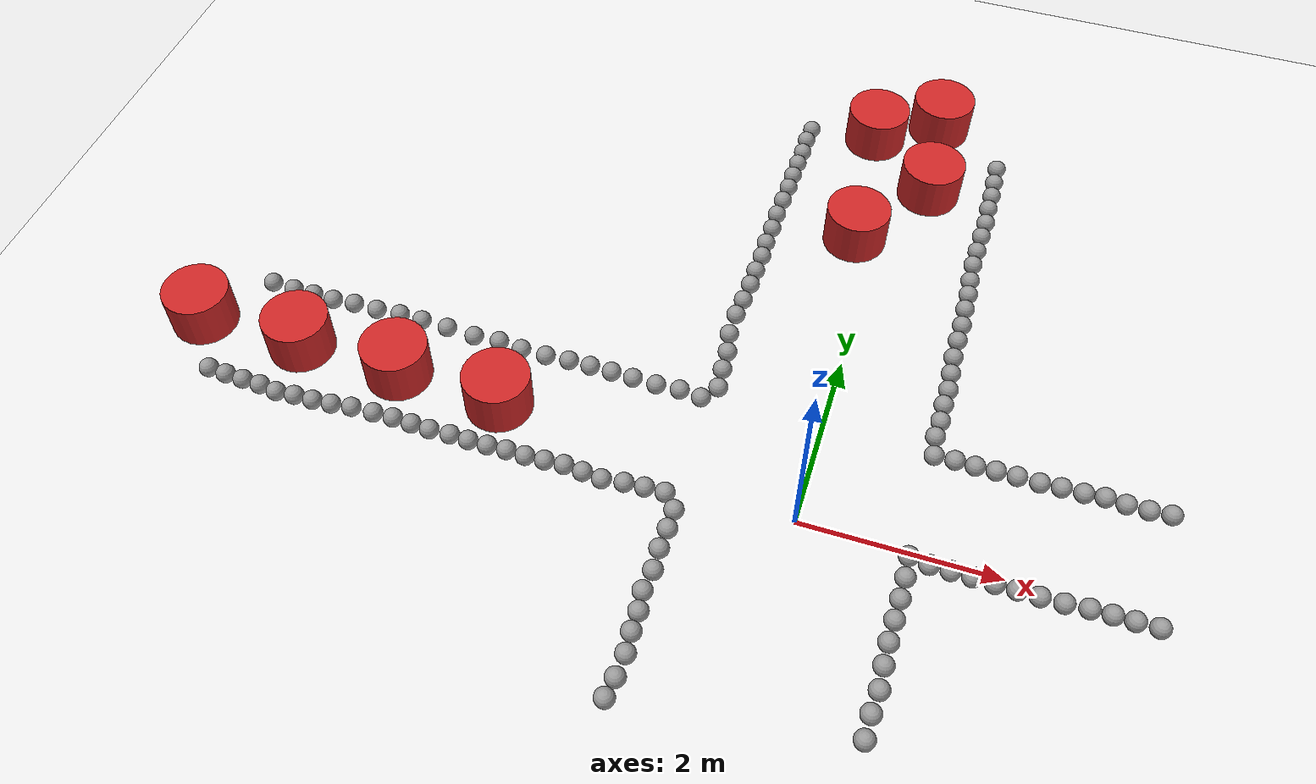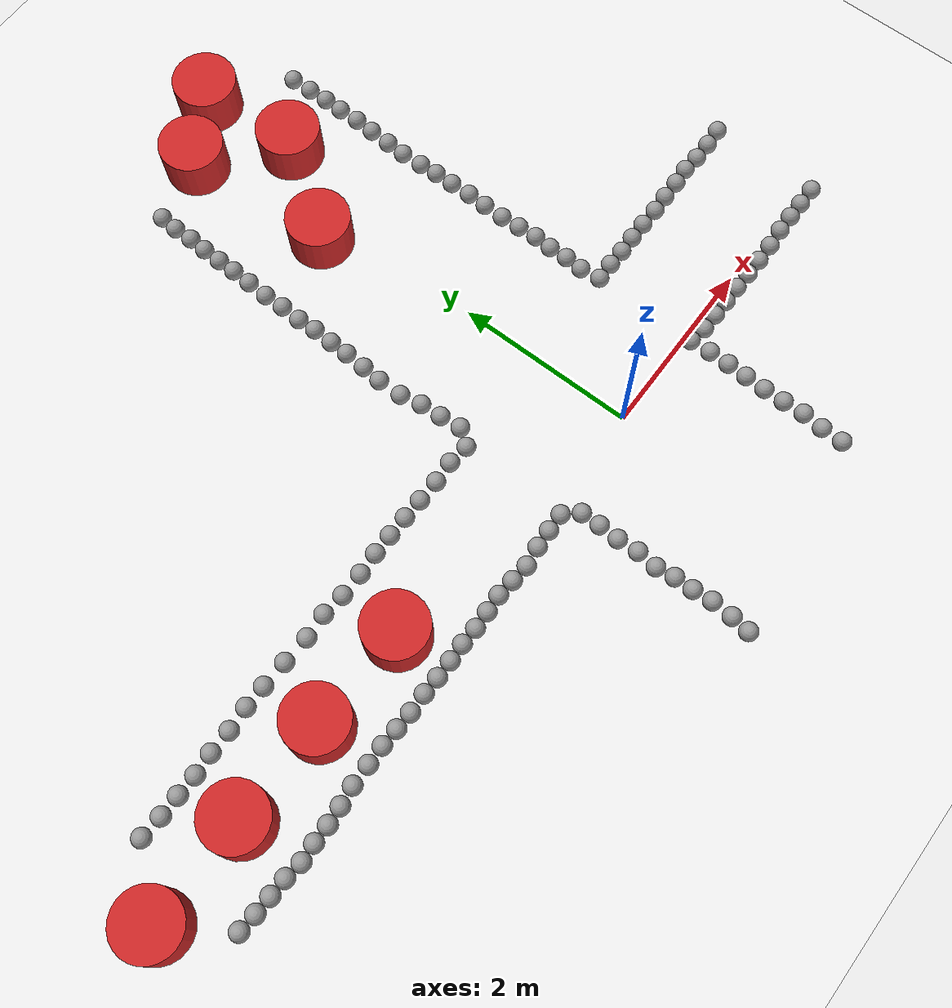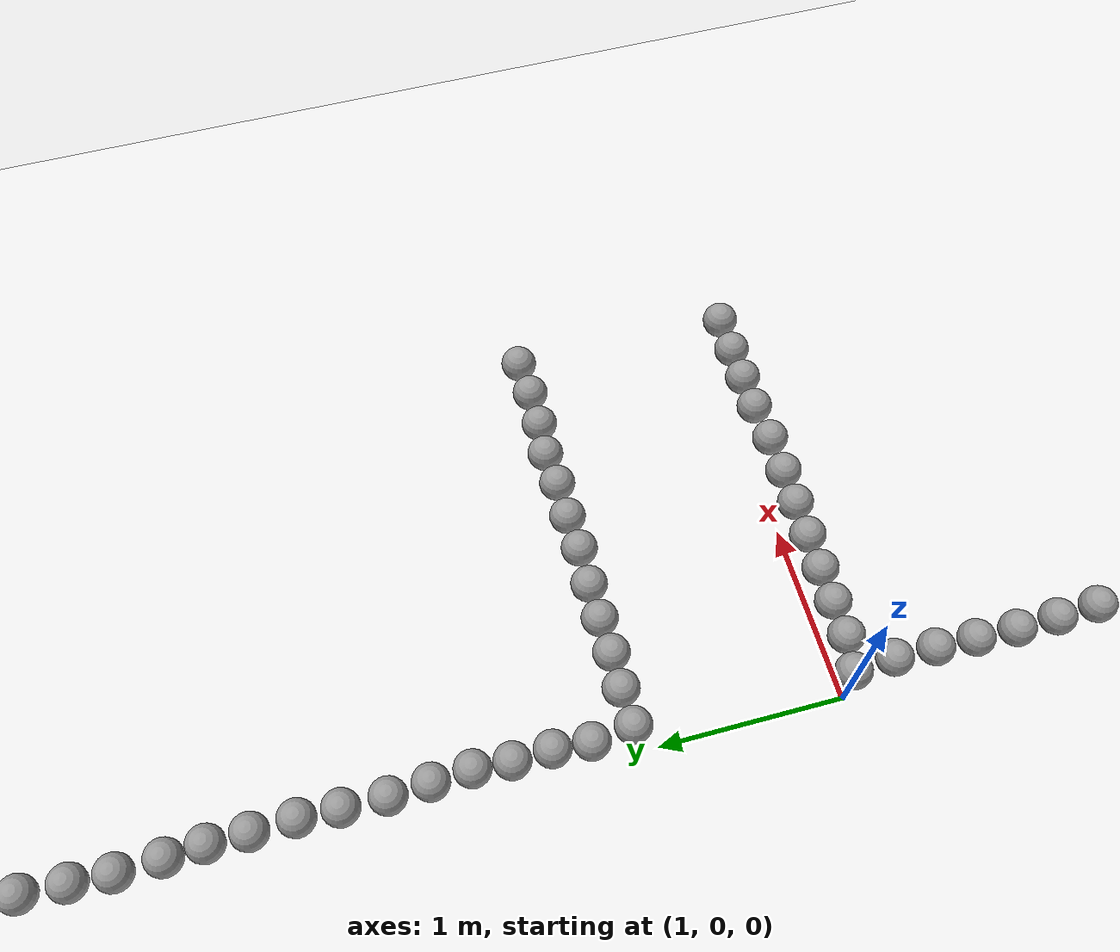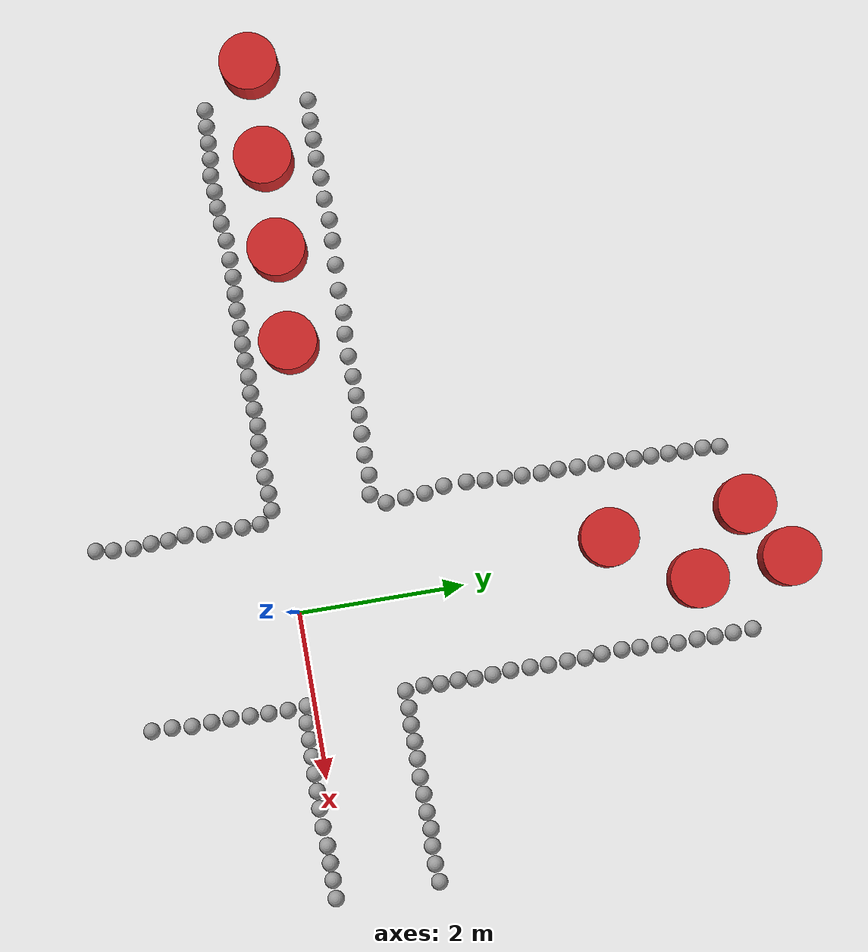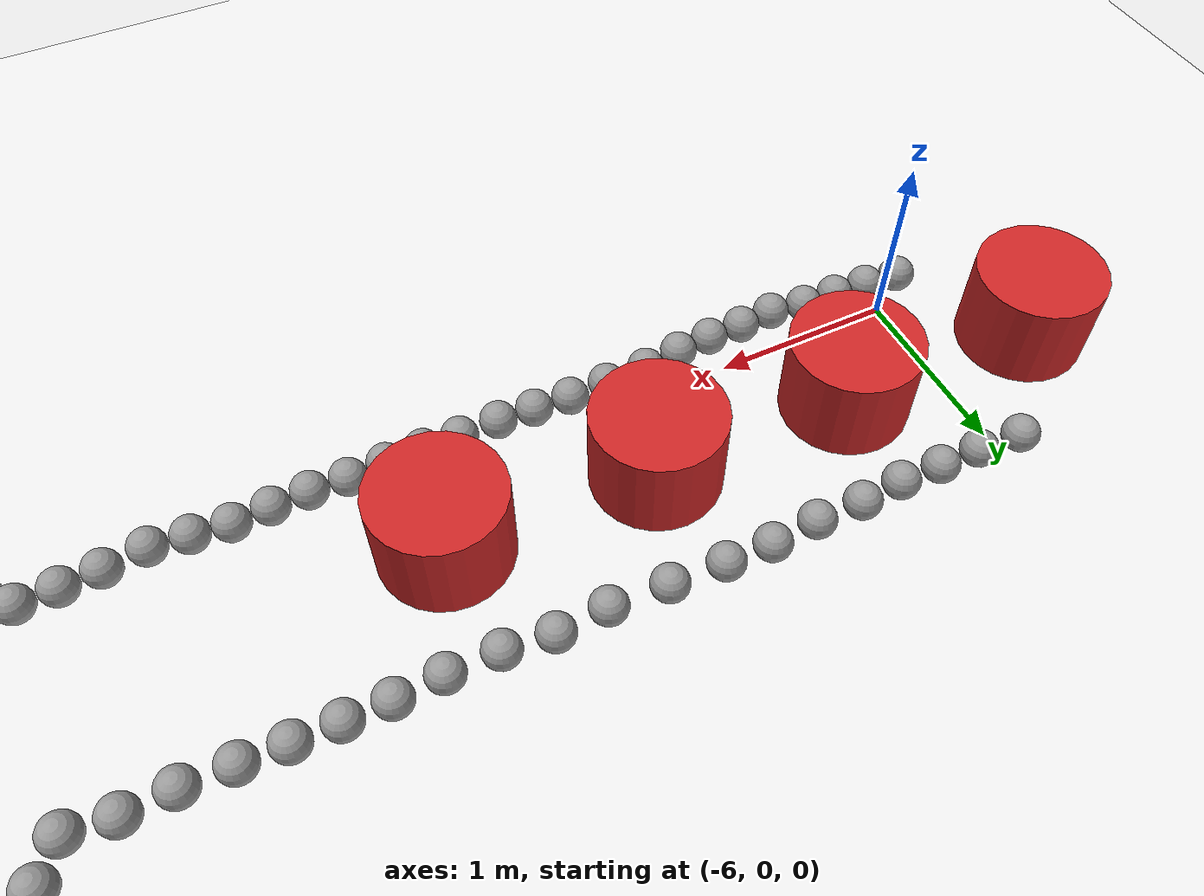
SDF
<sdf version="1.7">
 <world name="default">
  <light name="sun" type="directional">
   <pose>0 0 10 0 -0 0</pose>
   <diffuse>0.8 0.8 0.8 1</diffuse>
   <specular>0.2 0.2 0.2 1</specular>
   <attenuation>
    <range>1000</range>
    <constant>0.9</constant>
    <linear>0.01</linear>
    <quadratic>0.001</quadratic>
   </attenuation>
   <direction>-0.5 0.1 -0.9</direction>
   <spot><inner_angle>0</inner_angle><outer_angle>0</outer_angle><falloff>0</falloff></spot>
  </light>
  <model name="ground_plane">
   <static>1</static>
   <link name="link">
    <collision name="collision">
     <geometry><plane><normal>0 0 1</normal><size>100 100</size></plane></geometry>
     <surface>
      <contact><collide_bitmask>65535</collide_bitmask></contact>
      <friction><ode><mu>100</mu><mu2>50</mu2></ode></friction>
     </surface>
    </collision>
    <visual name="visual">
     <cast_shadows>0</cast_shadows>
     <geometry><plane><normal>0 0 1</normal><size>100 100</size></plane></geometry>
     <material>
      <script><uri>file://media/materials/scripts/gazebo.material</uri><name>Gazebo/White</name></script>
     </material>
    </visual>
   </link>
  </model>
  <gravity>0 0 -9.8</gravity>
  <magnetic_field>6e-06 2.3e-05 -4.2e-05</magnetic_field>
  <atmosphere type="adiabatic"/>
  <physics type="ode">
   <max_step_size>0.001</max_step_size>
   <real_time_factor>1</real_time_factor>
   <real_time_update_rate>1000</real_time_update_rate>
  </physics>
  <scene><ambient>0.4 0.4 0.4 1</ambient><background>0.7 0.7 0.7 1</background><shadows>1</shadows></scene>
  <spherical_coordinates>
   <surface_model>EARTH_WGS84</surface_model>
   <latitude_deg>0</latitude_deg>
   <longitude_deg>0</longitude_deg>
   <elevation>0</elevation>
   <heading_deg>0</heading_deg>
  </spherical_coordinates>
  <model name="sphere">
   <link name="link_0">
    <inertial>
     <mass>1</mass>
     <inertia><ixx>0.1</ixx><ixy>0</ixy><ixz>0</ixz><iyy>0.1</iyy><iyz>0</iyz><izz>0.1</izz></inertia>
    </inertial>
    <visual name="visual">
     <geometry><sphere><radius>0.1</radius></sphere></geometry>
     <material>
      <lighting>1</lighting>
      <script><uri>file://media/materials/scripts/gazebo.material</uri><name>Gazebo/Grey</name></script>
      <shader type="pixel"><normal_map>__default__</normal_map></shader>
      <ambient>0.3 0.3 0.3 1</ambient>
      <diffuse>0.7 0.7 0.7 1</diffuse>
      <specular>0.01 0.01 0.01 1</specular>
      <emissive>0 0 0 1</emissive>
     </material>
    </visual>
    <collision name="collision">
     <geometry><sphere><radius>0.1</radius></sphere></geometry>
     <surface>
      <friction>
       <ode><mu>1</mu><mu2>1</mu2><fdir1>0 0 0</fdir1><slip1>0</slip1><slip2>0</slip2></ode>
       <torsional>
        <coefficient>1</coefficient>
        <patch_radius>0</patch_radius>
        <surface_radius>0</surface_radius>
        <use_patch_radius>1</use_patch_radius>
        <ode><slip>0</slip></ode>
       </torsional>
      </friction>
      <bounce><restitution_coefficient>0</restitution_coefficient><threshold>1e+06</threshold></bounce>
      <contact>
       <collide_without_contact>0</collide_without_contact>
       <collide_without_contact_bitmask>1</collide_without_contact_bitmask>
       <collide_bitmask>1</collide_bitmask>
       <ode>
        <soft_cfm>0</soft_cfm>
        <soft_erp>0.2</soft_erp>
        <kp>1e+13</kp>
        <kd>1</kd>
        <max_vel>0.01</max_vel>
        <min_depth>0</min_depth>
       </ode>
       <bullet>
        <split_impulse>1</split_impulse>
        <split_impulse_penetration_threshold>-0.01</split_impulse_penetration_threshold>
        <soft_cfm>0</soft_cfm>
        <soft_erp>0.2</soft_erp>
        <kp>1e+13</kp>
        <kd>1</kd>
       </bullet>
      </contact>
     </surface>
    </collision>
   </link>
   <static>0</static>
   <pose>1.12265 1.10164 0.1 0 -0 0</pose>
  </model>
  <model name="sphere_0">
   <link name="link_0">
    <inertial>
     <mass>1</mass>
     <inertia><ixx>0.1</ixx><ixy>0</ixy><ixz>0</ixz><iyy>0.1</iyy><iyz>0</iyz><izz>0.1</izz></inertia>
    </inertial>
    <visual name="visual">
     <geometry><sphere><radius>0.1</radius></sphere></geometry>
     <material>
      <lighting>1</lighting>
      <script><uri>file://media/materials/scripts/gazebo.material</uri><name>Gazebo/Grey</name></script>
      <shader type="pixel"><normal_map>__default__</normal_map></shader>
      <ambient>0.3 0.3 0.3 1</ambient>
      <diffuse>0.7 0.7 0.7 1</diffuse>
      <specular>0.01 0.01 0.01 1</specular>
      <emissive>0 0 0 1</emissive>
     </material>
    </visual>
    <collision name="collision">
     <geometry><sphere><radius>0.1</radius></sphere></geometry>
     <surface>
      <friction>
       <ode><mu>1</mu><mu2>1</mu2><fdir1>0 0 0</fdir1><slip1>0</slip1><slip2>0</slip2></ode>
       <torsional>
        <coefficient>1</coefficient>
        <patch_radius>0</patch_radius>
        <surface_radius>0</surface_radius>
        <use_patch_radius>1</use_patch_radius>
        <ode><slip>0</slip></ode>
       </torsional>
      </friction>
      <bounce><restitution_coefficient>0</restitution_coefficient><threshold>1e+06</threshold></bounce>
      <contact>
       <collide_without_contact>0</collide_without_contact>
       <collide_without_contact_bitmask>1</collide_without_contact_bitmask>
       <collide_bitmask>1</collide_bitmask>
       <ode>
        <soft_cfm>0</soft_cfm>
        <soft_erp>0.2</soft_erp>
        <kp>1e+13</kp>
        <kd>1</kd>
        <max_vel>0.01</max_vel>
        <min_depth>0</min_depth>
       </ode>
       <bullet>
        <split_impulse>1</split_impulse>
        <split_impulse_penetration_threshold>-0.01</split_impulse_penetration_threshold>
        <soft_cfm>0</soft_cfm>
        <soft_erp>0.2</soft_erp>
        <kp>1e+13</kp>
        <kd>1</kd>
       </bullet>
      </contact>
     </surface>
    </collision>
   </link>
   <static>0</static>
   <pose>1.09484 1.32792 0.1 0.007885 -0.000594 2e-06</pose>
  </model>
  <model name="sphere_1">
   <link name="link_0">
    <inertial>
     <mass>1</mass>
     <inertia><ixx>0.1</ixx><ixy>0</ixy><ixz>0</ixz><iyy>0.1</iyy><iyz>0</iyz><izz>0.1</izz></inertia>
    </inertial>
    <visual name="visual">
     <geometry><sphere><radius>0.1</radius></sphere></geometry>
     <material>
      <lighting>1</lighting>
      <script><uri>file://media/materials/scripts/gazebo.material</uri><name>Gazebo/Grey</name></script>
      <shader type="pixel"><normal_map>__default__</normal_map></shader>
      <ambient>0.3 0.3 0.3 1</ambient>
      <diffuse>0.7 0.7 0.7 1</diffuse>
      <specular>0.01 0.01 0.01 1</specular>
      <emissive>0 0 0 1</emissive>
     </material>
    </visual>
    <collision name="collision">
     <geometry><sphere><radius>0.1</radius></sphere></geometry>
     <surface>
      <friction>
       <ode><mu>1</mu><mu2>1</mu2><fdir1>0 0 0</fdir1><slip1>0</slip1><slip2>0</slip2></ode>
       <torsional>
        <coefficient>1</coefficient>
        <patch_radius>0</patch_radius>
        <surface_radius>0</surface_radius>
        <use_patch_radius>1</use_patch_radius>
        <ode><slip>0</slip></ode>
       </torsional>
      </friction>
      <bounce><restitution_coefficient>0</restitution_coefficient><threshold>1e+06</threshold></bounce>
      <contact>
       <collide_without_contact>0</collide_without_contact>
       <collide_without_contact_bitmask>1</collide_without_contact_bitmask>
       <collide_bitmask>1</collide_bitmask>
       <ode>
        <soft_cfm>0</soft_cfm>
        <soft_erp>0.2</soft_erp>
        <kp>1e+13</kp>
        <kd>1</kd>
        <max_vel>0.01</max_vel>
        <min_depth>0</min_depth>
       </ode>
       <bullet>
        <split_impulse>1</split_impulse>
        <split_impulse_penetration_threshold>-0.01</split_impulse_penetration_threshold>
        <soft_cfm>0</soft_cfm>
        <soft_erp>0.2</soft_erp>
        <kp>1e+13</kp>
        <kd>1</kd>
       </bullet>
      </contact>
     </surface>
    </collision>
   </link>
   <static>0</static>
   <pose>1.10973 1.52904 0.1 -0.008762 0.000649 1e-06</pose>
  </model>
  <model name="sphere_2">
   <link name="link_0">
    <inertial>
     <mass>1</mass>
     <inertia><ixx>0.1</ixx><ixy>0</ixy><ixz>0</ixz><iyy>0.1</iyy><iyz>0</iyz><izz>0.1</izz></inertia>
    </inertial>
    <visual name="visual">
     <geometry><sphere><radius>0.1</radius></sphere></geometry>
     <material>
      <lighting>1</lighting>
      <script><uri>file://media/materials/scripts/gazebo.material</uri><name>Gazebo/Grey</name></script>
      <shader type="pixel"><normal_map>__default__</normal_map></shader>
      <ambient>0.3 0.3 0.3 1</ambient>
      <diffuse>0.7 0.7 0.7 1</diffuse>
      <specular>0.01 0.01 0.01 1</specular>
      <emissive>0 0 0 1</emissive>
     </material>
    </visual>
    <collision name="collision">
     <geometry><sphere><radius>0.1</radius></sphere></geometry>
     <surface>
      <friction>
       <ode><mu>1</mu><mu2>1</mu2><fdir1>0 0 0</fdir1><slip1>0</slip1><slip2>0</slip2></ode>
       <torsional>
        <coefficient>1</coefficient>
        <patch_radius>0</patch_radius>
        <surface_radius>0</surface_radius>
        <use_patch_radius>1</use_patch_radius>
        <ode><slip>0</slip></ode>
       </torsional>
      </friction>
      <bounce><restitution_coefficient>0</restitution_coefficient><threshold>1e+06</threshold></bounce>
      <contact>
       <collide_without_contact>0</collide_without_contact>
       <collide_without_contact_bitmask>1</collide_without_contact_bitmask>
       <collide_bitmask>1</collide_bitmask>
       <ode>
        <soft_cfm>0</soft_cfm>
        <soft_erp>0.2</soft_erp>
        <kp>1e+13</kp>
        <kd>1</kd>
        <max_vel>0.01</max_vel>
        <min_depth>0</min_depth>
       </ode>
       <bullet>
        <split_impulse>1</split_impulse>
        <split_impulse_penetration_threshold>-0.01</split_impulse_penetration_threshold>
        <soft_cfm>0</soft_cfm>
        <soft_erp>0.2</soft_erp>
        <kp>1e+13</kp>
        <kd>1</kd>
       </bullet>
      </contact>
     </surface>
    </collision>
   </link>
   <static>0</static>
   <pose>1.10382 1.73894 0.1 0.007911 -0.00051 2e-06</pose>
  </model>
  <model name="sphere_3">
   <link name="link_0">
    <inertial>
     <mass>1</mass>
     <inertia><ixx>0.1</ixx><ixy>0</ixy><ixz>0</ixz><iyy>0.1</iyy><iyz>0</iyz><izz>0.1</izz></inertia>
    </inertial>
    <visual name="visual">
     <geometry><sphere><radius>0.1</radius></sphere></geometry>
     <material>
      <lighting>1</lighting>
      <script><uri>file://media/materials/scripts/gazebo.material</uri><name>Gazebo/Grey</name></script>
      <shader type="pixel"><normal_map>__default__</normal_map></shader>
      <ambient>0.3 0.3 0.3 1</ambient>
      <diffuse>0.7 0.7 0.7 1</diffuse>
      <specular>0.01 0.01 0.01 1</specular>
      <emissive>0 0 0 1</emissive>
     </material>
    </visual>
    <collision name="collision">
     <geometry><sphere><radius>0.1</radius></sphere></geometry>
     <surface>
      <friction>
       <ode><mu>1</mu><mu2>1</mu2><fdir1>0 0 0</fdir1><slip1>0</slip1><slip2>0</slip2></ode>
       <torsional>
        <coefficient>1</coefficient>
        <patch_radius>0</patch_radius>
        <surface_radius>0</surface_radius>
        <use_patch_radius>1</use_patch_radius>
        <ode><slip>0</slip></ode>
       </torsional>
      </friction>
      <bounce><restitution_coefficient>0</restitution_coefficient><threshold>1e+06</threshold></bounce>
      <contact>
       <collide_without_contact>0</collide_without_contact>
       <collide_without_contact_bitmask>1</collide_without_contact_bitmask>
       <collide_bitmask>1</collide_bitmask>
       <ode>
        <soft_cfm>0</soft_cfm>
        <soft_erp>0.2</soft_erp>
        <kp>1e+13</kp>
        <kd>1</kd>
        <max_vel>0.01</max_vel>
        <min_depth>0</min_depth>
       </ode>
       <bullet>
        <split_impulse>1</split_impulse>
        <split_impulse_penetration_threshold>-0.01</split_impulse_penetration_threshold>
        <soft_cfm>0</soft_cfm>
        <soft_erp>0.2</soft_erp>
        <kp>1e+13</kp>
        <kd>1</kd>
       </bullet>
      </contact>
     </surface>
    </collision>
   </link>
   <static>0</static>
   <pose>1.11654 1.94022 0.1 -0.008745 0.000553 2e-06</pose>
  </model>
  <model name="sphere_4">
   <link name="link_0">
    <inertial>
     <mass>1</mass>
     <inertia><ixx>0.1</ixx><ixy>0</ixy><ixz>0</ixz><iyy>0.1</iyy><iyz>0</iyz><izz>0.1</izz></inertia>
    </inertial>
    <visual name="visual">
     <geometry><sphere><radius>0.1</radius></sphere></geometry>
     <material>
      <lighting>1</lighting>
      <script><uri>file://media/materials/scripts/gazebo.material</uri><name>Gazebo/Grey</name></script>
      <shader type="pixel"><normal_map>__default__</normal_map></shader>
      <ambient>0.3 0.3 0.3 1</ambient>
      <diffuse>0.7 0.7 0.7 1</diffuse>
      <specular>0.01 0.01 0.01 1</specular>
      <emissive>0 0 0 1</emissive>
     </material>
    </visual>
    <collision name="collision">
     <geometry><sphere><radius>0.1</radius></sphere></geometry>
     <surface>
      <friction>
       <ode><mu>1</mu><mu2>1</mu2><fdir1>0 0 0</fdir1><slip1>0</slip1><slip2>0</slip2></ode>
       <torsional>
        <coefficient>1</coefficient>
        <patch_radius>0</patch_radius>
        <surface_radius>0</surface_radius>
        <use_patch_radius>1</use_patch_radius>
        <ode><slip>0</slip></ode>
       </torsional>
      </friction>
      <bounce><restitution_coefficient>0</restitution_coefficient><threshold>1e+06</threshold></bounce>
      <contact>
       <collide_without_contact>0</collide_without_contact>
       <collide_without_contact_bitmask>1</collide_without_contact_bitmask>
       <collide_bitmask>1</collide_bitmask>
       <ode>
        <soft_cfm>0</soft_cfm>
        <soft_erp>0.2</soft_erp>
        <kp>1e+13</kp>
        <kd>1</kd>
        <max_vel>0.01</max_vel>
        <min_depth>0</min_depth>
       </ode>
       <bullet>
        <split_impulse>1</split_impulse>
        <split_impulse_penetration_threshold>-0.01</split_impulse_penetration_threshold>
        <soft_cfm>0</soft_cfm>
        <soft_erp>0.2</soft_erp>
        <kp>1e+13</kp>
        <kd>1</kd>
       </bullet>
      </contact>
     </surface>
    </collision>
   </link>
   <static>0</static>
   <pose>1.10529 2.15475 0.1 0 -0 0</pose>
  </model>
  <model name="sphere_5">
   <link name="link_0">
    <inertial>
     <mass>1</mass>
     <inertia><ixx>0.1</ixx><ixy>0</ixy><ixz>0</ixz><iyy>0.1</iyy><iyz>0</iyz><izz>0.1</izz></inertia>
    </inertial>
    <visual name="visual">
     <geometry><sphere><radius>0.1</radius></sphere></geometry>
     <material>
      <lighting>1</lighting>
      <script><uri>file://media/materials/scripts/gazebo.material</uri><name>Gazebo/Grey</name></script>
      <shader type="pixel"><normal_map>__default__</normal_map></shader>
      <ambient>0.3 0.3 0.3 1</ambient>
      <diffuse>0.7 0.7 0.7 1</diffuse>
      <specular>0.01 0.01 0.01 1</specular>
      <emissive>0 0 0 1</emissive>
     </material>
    </visual>
    <collision name="collision">
     <geometry><sphere><radius>0.1</radius></sphere></geometry>
     <surface>
      <friction>
       <ode><mu>1</mu><mu2>1</mu2><fdir1>0 0 0</fdir1><slip1>0</slip1><slip2>0</slip2></ode>
       <torsional>
        <coefficient>1</coefficient>
        <patch_radius>0</patch_radius>
        <surface_radius>0</surface_radius>
        <use_patch_radius>1</use_patch_radius>
        <ode><slip>0</slip></ode>
       </torsional>
      </friction>
      <bounce><restitution_coefficient>0</restitution_coefficient><threshold>1e+06</threshold></bounce>
      <contact>
       <collide_without_contact>0</collide_without_contact>
       <collide_without_contact_bitmask>1</collide_without_contact_bitmask>
       <collide_bitmask>1</collide_bitmask>
       <ode>
        <soft_cfm>0</soft_cfm>
        <soft_erp>0.2</soft_erp>
        <kp>1e+13</kp>
        <kd>1</kd>
        <max_vel>0.01</max_vel>
        <min_depth>0</min_depth>
       </ode>
       <bullet>
        <split_impulse>1</split_impulse>
        <split_impulse_penetration_threshold>-0.01</split_impulse_penetration_threshold>
        <soft_cfm>0</soft_cfm>
        <soft_erp>0.2</soft_erp>
        <kp>1e+13</kp>
        <kd>1</kd>
       </bullet>
      </contact>
     </surface>
    </collision>
   </link>
   <static>0</static>
   <pose>1.09308 2.37367 0.1 0 -0 0</pose>
  </model>
  <model name="sphere_6">
   <link name="link_0">
    <inertial>
     <mass>1</mass>
     <inertia><ixx>0.1</ixx><ixy>0</ixy><ixz>0</ixz><iyy>0.1</iyy><iyz>0</iyz><izz>0.1</izz></inertia>
    </inertial>
    <visual name="visual">
     <geometry><sphere><radius>0.1</radius></sphere></geometry>
     <material>
      <lighting>1</lighting>
      <script><uri>file://media/materials/scripts/gazebo.material</uri><name>Gazebo/Grey</name></script>
      <shader type="pixel"><normal_map>__default__</normal_map></shader>
      <ambient>0.3 0.3 0.3 1</ambient>
      <diffuse>0.7 0.7 0.7 1</diffuse>
      <specular>0.01 0.01 0.01 1</specular>
      <emissive>0 0 0 1</emissive>
     </material>
    </visual>
    <collision name="collision">
     <geometry><sphere><radius>0.1</radius></sphere></geometry>
     <surface>
      <friction>
       <ode><mu>1</mu><mu2>1</mu2><fdir1>0 0 0</fdir1><slip1>0</slip1><slip2>0</slip2></ode>
       <torsional>
        <coefficient>1</coefficient>
        <patch_radius>0</patch_radius>
        <surface_radius>0</surface_radius>
        <use_patch_radius>1</use_patch_radius>
        <ode><slip>0</slip></ode>
       </torsional>
      </friction>
      <bounce><restitution_coefficient>0</restitution_coefficient><threshold>1e+06</threshold></bounce>
      <contact>
       <collide_without_contact>0</collide_without_contact>
       <collide_without_contact_bitmask>1</collide_without_contact_bitmask>
       <collide_bitmask>1</collide_bitmask>
       <ode>
        <soft_cfm>0</soft_cfm>
        <soft_erp>0.2</soft_erp>
        <kp>1e+13</kp>
        <kd>1</kd>
        <max_vel>0.01</max_vel>
        <min_depth>0</min_depth>
       </ode>
       <bullet>
        <split_impulse>1</split_impulse>
        <split_impulse_penetration_threshold>-0.01</split_impulse_penetration_threshold>
        <soft_cfm>0</soft_cfm>
        <soft_erp>0.2</soft_erp>
        <kp>1e+13</kp>
        <kd>1</kd>
       </bullet>
      </contact>
     </surface>
    </collision>
   </link>
   <static>0</static>
   <pose>1.09702 2.60936 0.1 0 -0 0</pose>
  </model>
  <model name="sphere_7">
   <link name="link_0">
    <inertial>
     <mass>1</mass>
     <inertia><ixx>0.1</ixx><ixy>0</ixy><ixz>0</ixz><iyy>0.1</iyy><iyz>0</iyz><izz>0.1</izz></inertia>
    </inertial>
    <visual name="visual">
     <geometry><sphere><radius>0.1</radius></sphere></geometry>
     <material>
      <lighting>1</lighting>
      <script><uri>file://media/materials/scripts/gazebo.material</uri><name>Gazebo/Grey</name></script>
      <shader type="pixel"><normal_map>__default__</normal_map></shader>
      <ambient>0.3 0.3 0.3 1</ambient>
      <diffuse>0.7 0.7 0.7 1</diffuse>
      <specular>0.01 0.01 0.01 1</specular>
      <emissive>0 0 0 1</emissive>
     </material>
    </visual>
    <collision name="collision">
     <geometry><sphere><radius>0.1</radius></sphere></geometry>
     <surface>
      <friction>
       <ode><mu>1</mu><mu2>1</mu2><fdir1>0 0 0</fdir1><slip1>0</slip1><slip2>0</slip2></ode>
       <torsional>
        <coefficient>1</coefficient>
        <patch_radius>0</patch_radius>
        <surface_radius>0</surface_radius>
        <use_patch_radius>1</use_patch_radius>
        <ode><slip>0</slip></ode>
       </torsional>
      </friction>
      <bounce><restitution_coefficient>0</restitution_coefficient><threshold>1e+06</threshold></bounce>
      <contact>
       <collide_without_contact>0</collide_without_contact>
       <collide_without_contact_bitmask>1</collide_without_contact_bitmask>
       <collide_bitmask>1</collide_bitmask>
       <ode>
        <soft_cfm>0</soft_cfm>
        <soft_erp>0.2</soft_erp>
        <kp>1e+13</kp>
        <kd>1</kd>
        <max_vel>0.01</max_vel>
        <min_depth>0</min_depth>
       </ode>
       <bullet>
        <split_impulse>1</split_impulse>
        <split_impulse_penetration_threshold>-0.01</split_impulse_penetration_threshold>
        <soft_cfm>0</soft_cfm>
        <soft_erp>0.2</soft_erp>
        <kp>1e+13</kp>
        <kd>1</kd>
       </bullet>
      </contact>
     </surface>
    </collision>
   </link>
   <static>0</static>
   <pose>1.10428 2.82821 0.1 0 -0 0</pose>
  </model>
  <model name="sphere_8">
   <link name="link_0">
    <inertial>
     <mass>1</mass>
     <inertia><ixx>0.1</ixx><ixy>0</ixy><ixz>0</ixz><iyy>0.1</iyy><iyz>0</iyz><izz>0.1</izz></inertia>
    </inertial>
    <visual name="visual">
     <geometry><sphere><radius>0.1</radius></sphere></geometry>
     <material>
      <lighting>1</lighting>
      <script><uri>file://media/materials/scripts/gazebo.material</uri><name>Gazebo/Grey</name></script>
      <shader type="pixel"><normal_map>__default__</normal_map></shader>
      <ambient>0.3 0.3 0.3 1</ambient>
      <diffuse>0.7 0.7 0.7 1</diffuse>
      <specular>0.01 0.01 0.01 1</specular>
      <emissive>0 0 0 1</emissive>
     </material>
    </visual>
    <collision name="collision">
     <geometry><sphere><radius>0.1</radius></sphere></geometry>
     <surface>
      <friction>
       <ode><mu>1</mu><mu2>1</mu2><fdir1>0 0 0</fdir1><slip1>0</slip1><slip2>0</slip2></ode>
       <torsional>
        <coefficient>1</coefficient>
        <patch_radius>0</patch_radius>
        <surface_radius>0</surface_radius>
        <use_patch_radius>1</use_patch_radius>
        <ode><slip>0</slip></ode>
       </torsional>
      </friction>
      <bounce><restitution_coefficient>0</restitution_coefficient><threshold>1e+06</threshold></bounce>
      <contact>
       <collide_without_contact>0</collide_without_contact>
       <collide_without_contact_bitmask>1</collide_without_contact_bitmask>
       <collide_bitmask>1</collide_bitmask>
       <ode>
        <soft_cfm>0</soft_cfm>
        <soft_erp>0.2</soft_erp>
        <kp>1e+13</kp>
        <kd>1</kd>
        <max_vel>0.01</max_vel>
        <min_depth>0</min_depth>
       </ode>
       <bullet>
        <split_impulse>1</split_impulse>
        <split_impulse_penetration_threshold>-0.01</split_impulse_penetration_threshold>
        <soft_cfm>0</soft_cfm>
        <soft_erp>0.2</soft_erp>
        <kp>1e+13</kp>
        <kd>1</kd>
       </bullet>
      </contact>
     </surface>
    </collision>
   </link>
   <static>0</static>
   <pose>1.09813 3.0606 0.1 0 -0 0</pose>
  </model>
  <model name="sphere_9">
   <link name="link_0">
    <inertial>
     <mass>1</mass>
     <inertia><ixx>0.1</ixx><ixy>0</ixy><ixz>0</ixz><iyy>0.1</iyy><iyz>0</iyz><izz>0.1</izz></inertia>
    </inertial>
    <visual name="visual">
     <geometry><sphere><radius>0.1</radius></sphere></geometry>
     <material>
      <lighting>1</lighting>
      <script><uri>file://media/materials/scripts/gazebo.material</uri><name>Gazebo/Grey</name></script>
      <shader type="pixel"><normal_map>__default__</normal_map></shader>
      <ambient>0.3 0.3 0.3 1</ambient>
      <diffuse>0.7 0.7 0.7 1</diffuse>
      <specular>0.01 0.01 0.01 1</specular>
      <emissive>0 0 0 1</emissive>
     </material>
    </visual>
    <collision name="collision">
     <geometry><sphere><radius>0.1</radius></sphere></geometry>
     <surface>
      <friction>
       <ode><mu>1</mu><mu2>1</mu2><fdir1>0 0 0</fdir1><slip1>0</slip1><slip2>0</slip2></ode>
       <torsional>
        <coefficient>1</coefficient>
        <patch_radius>0</patch_radius>
        <surface_radius>0</surface_radius>
        <use_patch_radius>1</use_patch_radius>
        <ode><slip>0</slip></ode>
       </torsional>
      </friction>
      <bounce><restitution_coefficient>0</restitution_coefficient><threshold>1e+06</threshold></bounce>
      <contact>
       <collide_without_contact>0</collide_without_contact>
       <collide_without_contact_bitmask>1</collide_without_contact_bitmask>
       <collide_bitmask>1</collide_bitmask>
       <ode>
        <soft_cfm>0</soft_cfm>
        <soft_erp>0.2</soft_erp>
        <kp>1e+13</kp>
        <kd>1</kd>
        <max_vel>0.01</max_vel>
        <min_depth>0</min_depth>
       </ode>
       <bullet>
        <split_impulse>1</split_impulse>
        <split_impulse_penetration_threshold>-0.01</split_impulse_penetration_threshold>
        <soft_cfm>0</soft_cfm>
        <soft_erp>0.2</soft_erp>
        <kp>1e+13</kp>
        <kd>1</kd>
       </bullet>
      </contact>
     </surface>
    </collision>
   </link>
   <static>0</static>
   <pose>1.09675 3.27542 0.1 0 -0 0</pose>
  </model>
  <model name="sphere_10">
   <link name="link_0">
    <inertial>
     <mass>1</mass>
     <inertia><ixx>0.1</ixx><ixy>0</ixy><ixz>0</ixz><iyy>0.1</iyy><iyz>0</iyz><izz>0.1</izz></inertia>
    </inertial>
    <visual name="visual">
     <geometry><sphere><radius>0.1</radius></sphere></geometry>
     <material>
      <lighting>1</lighting>
      <script><uri>file://media/materials/scripts/gazebo.material</uri><name>Gazebo/Grey</name></script>
      <shader type="pixel"><normal_map>__default__</normal_map></shader>
      <ambient>0.3 0.3 0.3 1</ambient>
      <diffuse>0.7 0.7 0.7 1</diffuse>
      <specular>0.01 0.01 0.01 1</specular>
      <emissive>0 0 0 1</emissive>
     </material>
    </visual>
    <collision name="collision">
     <geometry><sphere><radius>0.1</radius></sphere></geometry>
     <surface>
      <friction>
       <ode><mu>1</mu><mu2>1</mu2><fdir1>0 0 0</fdir1><slip1>0</slip1><slip2>0</slip2></ode>
       <torsional>
        <coefficient>1</coefficient>
        <patch_radius>0</patch_radius>
        <surface_radius>0</surface_radius>
        <use_patch_radius>1</use_patch_radius>
        <ode><slip>0</slip></ode>
       </torsional>
      </friction>
      <bounce><restitution_coefficient>0</restitution_coefficient><threshold>1e+06</threshold></bounce>
      <contact>
       <collide_without_contact>0</collide_without_contact>
       <collide_without_contact_bitmask>1</collide_without_contact_bitmask>
       <collide_bitmask>1</collide_bitmask>
       <ode>
        <soft_cfm>0</soft_cfm>
        <soft_erp>0.2</soft_erp>
        <kp>1e+13</kp>
        <kd>1</kd>
        <max_vel>0.01</max_vel>
        <min_depth>0</min_depth>
       </ode>
       <bullet>
        <split_impulse>1</split_impulse>
        <split_impulse_penetration_threshold>-0.01</split_impulse_penetration_threshold>
        <soft_cfm>0</soft_cfm>
        <soft_erp>0.2</soft_erp>
        <kp>1e+13</kp>
        <kd>1</kd>
       </bullet>
      </contact>
     </surface>
    </collision>
   </link>
   <static>0</static>
   <pose>1.08313 3.47908 0.1 0 -0 0</pose>
  </model>
  <model name="sphere_11">
   <link name="link_0">
    <inertial>
     <mass>1</mass>
     <inertia><ixx>0.1</ixx><ixy>0</ixy><ixz>0</ixz><iyy>0.1</iyy><iyz>0</iyz><izz>0.1</izz></inertia>
    </inertial>
    <visual name="visual">
     <geometry><sphere><radius>0.1</radius></sphere></geometry>
     <material>
      <lighting>1</lighting>
      <script><uri>file://media/materials/scripts/gazebo.material</uri><name>Gazebo/Grey</name></script>
      <shader type="pixel"><normal_map>__default__</normal_map></shader>
      <ambient>0.3 0.3 0.3 1</ambient>
      <diffuse>0.7 0.7 0.7 1</diffuse>
      <specular>0.01 0.01 0.01 1</specular>
      <emissive>0 0 0 1</emissive>
     </material>
    </visual>
    <collision name="collision">
     <geometry><sphere><radius>0.1</radius></sphere></geometry>
     <surface>
      <friction>
       <ode><mu>1</mu><mu2>1</mu2><fdir1>0 0 0</fdir1><slip1>0</slip1><slip2>0</slip2></ode>
       <torsional>
        <coefficient>1</coefficient>
        <patch_radius>0</patch_radius>
        <surface_radius>0</surface_radius>
        <use_patch_radius>1</use_patch_radius>
        <ode><slip>0</slip></ode>
       </torsional>
      </friction>
      <bounce><restitution_coefficient>0</restitution_coefficient><threshold>1e+06</threshold></bounce>
      <contact>
       <collide_without_contact>0</collide_without_contact>
       <collide_without_contact_bitmask>1</collide_without_contact_bitmask>
       <collide_bitmask>1</collide_bitmask>
       <ode>
        <soft_cfm>0</soft_cfm>
        <soft_erp>0.2</soft_erp>
        <kp>1e+13</kp>
        <kd>1</kd>
        <max_vel>0.01</max_vel>
        <min_depth>0</min_depth>
       </ode>
       <bullet>
        <split_impulse>1</split_impulse>
        <split_impulse_penetration_threshold>-0.01</split_impulse_penetration_threshold>
        <soft_cfm>0</soft_cfm>
        <soft_erp>0.2</soft_erp>
        <kp>1e+13</kp>
        <kd>1</kd>
       </bullet>
      </contact>
     </surface>
    </collision>
   </link>
   <static>0</static>
   <pose>1.07436 3.719 0.1 0 -0 0</pose>
  </model>
  <model name="sphere_12">
   <link name="link_0">
    <inertial>
     <mass>1</mass>
     <inertia><ixx>0.1</ixx><ixy>0</ixy><ixz>0</ixz><iyy>0.1</iyy><iyz>0</iyz><izz>0.1</izz></inertia>
    </inertial>
    <visual name="visual">
     <geometry><sphere><radius>0.1</radius></sphere></geometry>
     <material>
      <lighting>1</lighting>
      <script><uri>file://media/materials/scripts/gazebo.material</uri><name>Gazebo/Grey</name></script>
      <shader type="pixel"><normal_map>__default__</normal_map></shader>
      <ambient>0.3 0.3 0.3 1</ambient>
      <diffuse>0.7 0.7 0.7 1</diffuse>
      <specular>0.01 0.01 0.01 1</specular>
      <emissive>0 0 0 1</emissive>
     </material>
    </visual>
    <collision name="collision">
     <geometry><sphere><radius>0.1</radius></sphere></geometry>
     <surface>
      <friction>
       <ode><mu>1</mu><mu2>1</mu2><fdir1>0 0 0</fdir1><slip1>0</slip1><slip2>0</slip2></ode>
       <torsional>
        <coefficient>1</coefficient>
        <patch_radius>0</patch_radius>
        <surface_radius>0</surface_radius>
        <use_patch_radius>1</use_patch_radius>
        <ode><slip>0</slip></ode>
       </torsional>
      </friction>
      <bounce><restitution_coefficient>0</restitution_coefficient><threshold>1e+06</threshold></bounce>
      <contact>
       <collide_without_contact>0</collide_without_contact>
       <collide_without_contact_bitmask>1</collide_without_contact_bitmask>
       <collide_bitmask>1</collide_bitmask>
       <ode>
        <soft_cfm>0</soft_cfm>
        <soft_erp>0.2</soft_erp>
        <kp>1e+13</kp>
        <kd>1</kd>
        <max_vel>0.01</max_vel>
        <min_depth>0</min_depth>
       </ode>
       <bullet>
        <split_impulse>1</split_impulse>
        <split_impulse_penetration_threshold>-0.01</split_impulse_penetration_threshold>
        <soft_cfm>0</soft_cfm>
        <soft_erp>0.2</soft_erp>
        <kp>1e+13</kp>
        <kd>1</kd>
       </bullet>
      </contact>
     </surface>
    </collision>
   </link>
   <static>0</static>
   <pose>1.08424 3.93708 0.1 0 -0 0</pose>
  </model>
  <model name="sphere_13">
   <link name="link_0">
    <inertial>
     <mass>1</mass>
     <inertia><ixx>0.1</ixx><ixy>0</ixy><ixz>0</ixz><iyy>0.1</iyy><iyz>0</iyz><izz>0.1</izz></inertia>
    </inertial>
    <visual name="visual">
     <geometry><sphere><radius>0.1</radius></sphere></geometry>
     <material>
      <lighting>1</lighting>
      <script><uri>file://media/materials/scripts/gazebo.material</uri><name>Gazebo/Grey</name></script>
      <shader type="pixel"><normal_map>__default__</normal_map></shader>
      <ambient>0.3 0.3 0.3 1</ambient>
      <diffuse>0.7 0.7 0.7 1</diffuse>
      <specular>0.01 0.01 0.01 1</specular>
      <emissive>0 0 0 1</emissive>
     </material>
    </visual>
    <collision name="collision">
     <geometry><sphere><radius>0.1</radius></sphere></geometry>
     <surface>
      <friction>
       <ode><mu>1</mu><mu2>1</mu2><fdir1>0 0 0</fdir1><slip1>0</slip1><slip2>0</slip2></ode>
       <torsional>
        <coefficient>1</coefficient>
        <patch_radius>0</patch_radius>
        <surface_radius>0</surface_radius>
        <use_patch_radius>1</use_patch_radius>
        <ode><slip>0</slip></ode>
       </torsional>
      </friction>
      <bounce><restitution_coefficient>0</restitution_coefficient><threshold>1e+06</threshold></bounce>
      <contact>
       <collide_without_contact>0</collide_without_contact>
       <collide_without_contact_bitmask>1</collide_without_contact_bitmask>
       <collide_bitmask>1</collide_bitmask>
       <ode>
        <soft_cfm>0</soft_cfm>
        <soft_erp>0.2</soft_erp>
        <kp>1e+13</kp>
        <kd>1</kd>
        <max_vel>0.01</max_vel>
        <min_depth>0</min_depth>
       </ode>
       <bullet>
        <split_impulse>1</split_impulse>
        <split_impulse_penetration_threshold>-0.01</split_impulse_penetration_threshold>
        <soft_cfm>0</soft_cfm>
        <soft_erp>0.2</soft_erp>
        <kp>1e+13</kp>
        <kd>1</kd>
       </bullet>
      </contact>
     </surface>
    </collision>
   </link>
   <static>0</static>
   <pose>1.09415 4.17387 0.1 0 -0 0</pose>
  </model>
  <model name="sphere_14">
   <link name="link_0">
    <inertial>
     <mass>1</mass>
     <inertia><ixx>0.1</ixx><ixy>0</ixy><ixz>0</ixz><iyy>0.1</iyy><iyz>0</iyz><izz>0.1</izz></inertia>
    </inertial>
    <visual name="visual">
     <geometry><sphere><radius>0.1</radius></sphere></geometry>
     <material>
      <lighting>1</lighting>
      <script><uri>file://media/materials/scripts/gazebo.material</uri><name>Gazebo/Grey</name></script>
      <shader type="pixel"><normal_map>__default__</normal_map></shader>
      <ambient>0.3 0.3 0.3 1</ambient>
      <diffuse>0.7 0.7 0.7 1</diffuse>
      <specular>0.01 0.01 0.01 1</specular>
      <emissive>0 0 0 1</emissive>
     </material>
    </visual>
    <collision name="collision">
     <geometry><sphere><radius>0.1</radius></sphere></geometry>
     <surface>
      <friction>
       <ode><mu>1</mu><mu2>1</mu2><fdir1>0 0 0</fdir1><slip1>0</slip1><slip2>0</slip2></ode>
       <torsional>
        <coefficient>1</coefficient>
        <patch_radius>0</patch_radius>
        <surface_radius>0</surface_radius>
        <use_patch_radius>1</use_patch_radius>
        <ode><slip>0</slip></ode>
       </torsional>
      </friction>
      <bounce><restitution_coefficient>0</restitution_coefficient><threshold>1e+06</threshold></bounce>
      <contact>
       <collide_without_contact>0</collide_without_contact>
       <collide_without_contact_bitmask>1</collide_without_contact_bitmask>
       <collide_bitmask>1</collide_bitmask>
       <ode>
        <soft_cfm>0</soft_cfm>
        <soft_erp>0.2</soft_erp>
        <kp>1e+13</kp>
        <kd>1</kd>
        <max_vel>0.01</max_vel>
        <min_depth>0</min_depth>
       </ode>
       <bullet>
        <split_impulse>1</split_impulse>
        <split_impulse_penetration_threshold>-0.01</split_impulse_penetration_threshold>
        <soft_cfm>0</soft_cfm>
        <soft_erp>0.2</soft_erp>
        <kp>1e+13</kp>
        <kd>1</kd>
       </bullet>
      </contact>
     </surface>
    </collision>
   </link>
   <static>0</static>
   <pose>1.10807 4.39527 0.1 0 -0 0</pose>
  </model>
  <model name="sphere_15">
   <link name="link_0">
    <inertial>
     <mass>1</mass>
     <inertia><ixx>0.1</ixx><ixy>0</ixy><ixz>0</ixz><iyy>0.1</iyy><iyz>0</iyz><izz>0.1</izz></inertia>
    </inertial>
    <visual name="visual">
     <geometry><sphere><radius>0.1</radius></sphere></geometry>
     <material>
      <lighting>1</lighting>
      <script><uri>file://media/materials/scripts/gazebo.material</uri><name>Gazebo/Grey</name></script>
      <shader type="pixel"><normal_map>__default__</normal_map></shader>
      <ambient>0.3 0.3 0.3 1</ambient>
      <diffuse>0.7 0.7 0.7 1</diffuse>
      <specular>0.01 0.01 0.01 1</specular>
      <emissive>0 0 0 1</emissive>
     </material>
    </visual>
    <collision name="collision">
     <geometry><sphere><radius>0.1</radius></sphere></geometry>
     <surface>
      <friction>
       <ode><mu>1</mu><mu2>1</mu2><fdir1>0 0 0</fdir1><slip1>0</slip1><slip2>0</slip2></ode>
       <torsional>
        <coefficient>1</coefficient>
        <patch_radius>0</patch_radius>
        <surface_radius>0</surface_radius>
        <use_patch_radius>1</use_patch_radius>
        <ode><slip>0</slip></ode>
       </torsional>
      </friction>
      <bounce><restitution_coefficient>0</restitution_coefficient><threshold>1e+06</threshold></bounce>
      <contact>
       <collide_without_contact>0</collide_without_contact>
       <collide_without_contact_bitmask>1</collide_without_contact_bitmask>
       <collide_bitmask>1</collide_bitmask>
       <ode>
        <soft_cfm>0</soft_cfm>
        <soft_erp>0.2</soft_erp>
        <kp>1e+13</kp>
        <kd>1</kd>
        <max_vel>0.01</max_vel>
        <min_depth>0</min_depth>
       </ode>
       <bullet>
        <split_impulse>1</split_impulse>
        <split_impulse_penetration_threshold>-0.01</split_impulse_penetration_threshold>
        <soft_cfm>0</soft_cfm>
        <soft_erp>0.2</soft_erp>
        <kp>1e+13</kp>
        <kd>1</kd>
       </bullet>
      </contact>
     </surface>
    </collision>
   </link>
   <static>0</static>
   <pose>1.10192 4.62639 0.1 0 -0 0</pose>
  </model>
  <model name="sphere_16">
   <link name="link_0">
    <inertial>
     <mass>1</mass>
     <inertia><ixx>0.1</ixx><ixy>0</ixy><ixz>0</ixz><iyy>0.1</iyy><iyz>0</iyz><izz>0.1</izz></inertia>
    </inertial>
    <visual name="visual">
     <geometry><sphere><radius>0.1</radius></sphere></geometry>
     <material>
      <lighting>1</lighting>
      <script><uri>file://media/materials/scripts/gazebo.material</uri><name>Gazebo/Grey</name></script>
      <shader type="pixel"><normal_map>__default__</normal_map></shader>
      <ambient>0.3 0.3 0.3 1</ambient>
      <diffuse>0.7 0.7 0.7 1</diffuse>
      <specular>0.01 0.01 0.01 1</specular>
      <emissive>0 0 0 1</emissive>
     </material>
    </visual>
    <collision name="collision">
     <geometry><sphere><radius>0.1</radius></sphere></geometry>
     <surface>
      <friction>
       <ode><mu>1</mu><mu2>1</mu2><fdir1>0 0 0</fdir1><slip1>0</slip1><slip2>0</slip2></ode>
       <torsional>
        <coefficient>1</coefficient>
        <patch_radius>0</patch_radius>
        <surface_radius>0</surface_radius>
        <use_patch_radius>1</use_patch_radius>
        <ode><slip>0</slip></ode>
       </torsional>
      </friction>
      <bounce><restitution_coefficient>0</restitution_coefficient><threshold>1e+06</threshold></bounce>
      <contact>
       <collide_without_contact>0</collide_without_contact>
       <collide_without_contact_bitmask>1</collide_without_contact_bitmask>
       <collide_bitmask>1</collide_bitmask>
       <ode>
        <soft_cfm>0</soft_cfm>
        <soft_erp>0.2</soft_erp>
        <kp>1e+13</kp>
        <kd>1</kd>
        <max_vel>0.01</max_vel>
        <min_depth>0</min_depth>
       </ode>
       <bullet>
        <split_impulse>1</split_impulse>
        <split_impulse_penetration_threshold>-0.01</split_impulse_penetration_threshold>
        <soft_cfm>0</soft_cfm>
        <soft_erp>0.2</soft_erp>
        <kp>1e+13</kp>
        <kd>1</kd>
       </bullet>
      </contact>
     </surface>
    </collision>
   </link>
   <static>0</static>
   <pose>1.1058 4.84077 0.1 0 -0 0</pose>
  </model>
  <model name="sphere_17">
   <link name="link_0">
    <inertial>
     <mass>1</mass>
     <inertia><ixx>0.1</ixx><ixy>0</ixy><ixz>0</ixz><iyy>0.1</iyy><iyz>0</iyz><izz>0.1</izz></inertia>
    </inertial>
    <visual name="visual">
     <geometry><sphere><radius>0.1</radius></sphere></geometry>
     <material>
      <lighting>1</lighting>
      <script><uri>file://media/materials/scripts/gazebo.material</uri><name>Gazebo/Grey</name></script>
      <shader type="pixel"><normal_map>__default__</normal_map></shader>
      <ambient>0.3 0.3 0.3 1</ambient>
      <diffuse>0.7 0.7 0.7 1</diffuse>
      <specular>0.01 0.01 0.01 1</specular>
      <emissive>0 0 0 1</emissive>
     </material>
    </visual>
    <collision name="collision">
     <geometry><sphere><radius>0.1</radius></sphere></geometry>
     <surface>
      <friction>
       <ode><mu>1</mu><mu2>1</mu2><fdir1>0 0 0</fdir1><slip1>0</slip1><slip2>0</slip2></ode>
       <torsional>
        <coefficient>1</coefficient>
        <patch_radius>0</patch_radius>
        <surface_radius>0</surface_radius>
        <use_patch_radius>1</use_patch_radius>
        <ode><slip>0</slip></ode>
       </torsional>
      </friction>
      <bounce><restitution_coefficient>0</restitution_coefficient><threshold>1e+06</threshold></bounce>
      <contact>
       <collide_without_contact>0</collide_without_contact>
       <collide_without_contact_bitmask>1</collide_without_contact_bitmask>
       <collide_bitmask>1</collide_bitmask>
       <ode>
        <soft_cfm>0</soft_cfm>
        <soft_erp>0.2</soft_erp>
        <kp>1e+13</kp>
        <kd>1</kd>
        <max_vel>0.01</max_vel>
        <min_depth>0</min_depth>
       </ode>
       <bullet>
        <split_impulse>1</split_impulse>
        <split_impulse_penetration_threshold>-0.01</split_impulse_penetration_threshold>
        <soft_cfm>0</soft_cfm>
        <soft_erp>0.2</soft_erp>
        <kp>1e+13</kp>
        <kd>1</kd>
       </bullet>
      </contact>
     </surface>
    </collision>
   </link>
   <static>0</static>
   <pose>1.09964 5.06189 0.1 0 -0 0</pose>
  </model>
  <model name="sphere_18">
   <link name="link_0">
    <inertial>
     <mass>1</mass>
     <inertia><ixx>0.1</ixx><ixy>0</ixy><ixz>0</ixz><iyy>0.1</iyy><iyz>0</iyz><izz>0.1</izz></inertia>
    </inertial>
    <visual name="visual">
     <geometry><sphere><radius>0.1</radius></sphere></geometry>
     <material>
      <lighting>1</lighting>
      <script><uri>file://media/materials/scripts/gazebo.material</uri><name>Gazebo/Grey</name></script>
      <shader type="pixel"><normal_map>__default__</normal_map></shader>
      <ambient>0.3 0.3 0.3 1</ambient>
      <diffuse>0.7 0.7 0.7 1</diffuse>
      <specular>0.01 0.01 0.01 1</specular>
      <emissive>0 0 0 1</emissive>
     </material>
    </visual>
    <collision name="collision">
     <geometry><sphere><radius>0.1</radius></sphere></geometry>
     <surface>
      <friction>
       <ode><mu>1</mu><mu2>1</mu2><fdir1>0 0 0</fdir1><slip1>0</slip1><slip2>0</slip2></ode>
       <torsional>
        <coefficient>1</coefficient>
        <patch_radius>0</patch_radius>
        <surface_radius>0</surface_radius>
        <use_patch_radius>1</use_patch_radius>
        <ode><slip>0</slip></ode>
       </torsional>
      </friction>
      <bounce><restitution_coefficient>0</restitution_coefficient><threshold>1e+06</threshold></bounce>
      <contact>
       <collide_without_contact>0</collide_without_contact>
       <collide_without_contact_bitmask>1</collide_without_contact_bitmask>
       <collide_bitmask>1</collide_bitmask>
       <ode>
        <soft_cfm>0</soft_cfm>
        <soft_erp>0.2</soft_erp>
        <kp>1e+13</kp>
        <kd>1</kd>
        <max_vel>0.01</max_vel>
        <min_depth>0</min_depth>
       </ode>
       <bullet>
        <split_impulse>1</split_impulse>
        <split_impulse_penetration_threshold>-0.01</split_impulse_penetration_threshold>
        <soft_cfm>0</soft_cfm>
        <soft_erp>0.2</soft_erp>
        <kp>1e+13</kp>
        <kd>1</kd>
       </bullet>
      </contact>
     </surface>
    </collision>
   </link>
   <static>0</static>
   <pose>1.09352 5.29976 0.1 0 -0 0</pose>
  </model>
  <model name="sphere_19">
   <link name="link_0">
    <inertial>
     <mass>1</mass>
     <inertia><ixx>0.1</ixx><ixy>0</ixy><ixz>0</ixz><iyy>0.1</iyy><iyz>0</iyz><izz>0.1</izz></inertia>
    </inertial>
    <visual name="visual">
     <geometry><sphere><radius>0.1</radius></sphere></geometry>
     <material>
      <lighting>1</lighting>
      <script><uri>file://media/materials/scripts/gazebo.material</uri><name>Gazebo/Grey</name></script>
      <shader type="pixel"><normal_map>__default__</normal_map></shader>
      <ambient>0.3 0.3 0.3 1</ambient>
      <diffuse>0.7 0.7 0.7 1</diffuse>
      <specular>0.01 0.01 0.01 1</specular>
      <emissive>0 0 0 1</emissive>
     </material>
    </visual>
    <collision name="collision">
     <geometry><sphere><radius>0.1</radius></sphere></geometry>
     <surface>
      <friction>
       <ode><mu>1</mu><mu2>1</mu2><fdir1>0 0 0</fdir1><slip1>0</slip1><slip2>0</slip2></ode>
       <torsional>
        <coefficient>1</coefficient>
        <patch_radius>0</patch_radius>
        <surface_radius>0</surface_radius>
        <use_patch_radius>1</use_patch_radius>
        <ode><slip>0</slip></ode>
       </torsional>
      </friction>
      <bounce><restitution_coefficient>0</restitution_coefficient><threshold>1e+06</threshold></bounce>
      <contact>
       <collide_without_contact>0</collide_without_contact>
       <collide_without_contact_bitmask>1</collide_without_contact_bitmask>
       <collide_bitmask>1</collide_bitmask>
       <ode>
        <soft_cfm>0</soft_cfm>
        <soft_erp>0.2</soft_erp>
        <kp>1e+13</kp>
        <kd>1</kd>
        <max_vel>0.01</max_vel>
        <min_depth>0</min_depth>
       </ode>
       <bullet>
        <split_impulse>1</split_impulse>
        <split_impulse_penetration_threshold>-0.01</split_impulse_penetration_threshold>
        <soft_cfm>0</soft_cfm>
        <soft_erp>0.2</soft_erp>
        <kp>1e+13</kp>
        <kd>1</kd>
       </bullet>
      </contact>
     </surface>
    </collision>
   </link>
   <static>0</static>
   <pose>-1.11929 5.29738 0.1 -0.007911 0.000637 2e-06</pose>
  </model>
  <model name="sphere_20">
   <link name="link_0">
    <inertial>
     <mass>1</mass>
     <inertia><ixx>0.1</ixx><ixy>0</ixy><ixz>0</ixz><iyy>0.1</iyy><iyz>0</iyz><izz>0.1</izz></inertia>
    </inertial>
    <visual name="visual">
     <geometry><sphere><radius>0.1</radius></sphere></geometry>
     <material>
      <lighting>1</lighting>
      <script><uri>file://media/materials/scripts/gazebo.material</uri><name>Gazebo/Grey</name></script>
      <shader type="pixel"><normal_map>__default__</normal_map></shader>
      <ambient>0.3 0.3 0.3 1</ambient>
      <diffuse>0.7 0.7 0.7 1</diffuse>
      <specular>0.01 0.01 0.01 1</specular>
      <emissive>0 0 0 1</emissive>
     </material>
    </visual>
    <collision name="collision">
     <geometry><sphere><radius>0.1</radius></sphere></geometry>
     <surface>
      <friction>
       <ode><mu>1</mu><mu2>1</mu2><fdir1>0 0 0</fdir1><slip1>0</slip1><slip2>0</slip2></ode>
       <torsional>
        <coefficient>1</coefficient>
        <patch_radius>0</patch_radius>
        <surface_radius>0</surface_radius>
        <use_patch_radius>1</use_patch_radius>
        <ode><slip>0</slip></ode>
       </torsional>
      </friction>
      <bounce><restitution_coefficient>0</restitution_coefficient><threshold>1e+06</threshold></bounce>
      <contact>
       <collide_without_contact>0</collide_without_contact>
       <collide_without_contact_bitmask>1</collide_without_contact_bitmask>
       <collide_bitmask>1</collide_bitmask>
       <ode>
        <soft_cfm>0</soft_cfm>
        <soft_erp>0.2</soft_erp>
        <kp>1e+13</kp>
        <kd>1</kd>
        <max_vel>0.01</max_vel>
        <min_depth>0</min_depth>
       </ode>
       <bullet>
        <split_impulse>1</split_impulse>
        <split_impulse_penetration_threshold>-0.01</split_impulse_penetration_threshold>
        <soft_cfm>0</soft_cfm>
        <soft_erp>0.2</soft_erp>
        <kp>1e+13</kp>
        <kd>1</kd>
       </bullet>
      </contact>
     </surface>
    </collision>
   </link>
   <static>0</static>
   <pose>-1.13523 5.09634 0.1 0.008725 -0.000692 1e-06</pose>
  </model>
  <model name="sphere_21">
   <link name="link_0">
    <inertial>
     <mass>1</mass>
     <inertia><ixx>0.1</ixx><ixy>0</ixy><ixz>0</ixz><iyy>0.1</iyy><iyz>0</iyz><izz>0.1</izz></inertia>
    </inertial>
    <visual name="visual">
     <geometry><sphere><radius>0.1</radius></sphere></geometry>
     <material>
      <lighting>1</lighting>
      <script><uri>file://media/materials/scripts/gazebo.material</uri><name>Gazebo/Grey</name></script>
      <shader type="pixel"><normal_map>__default__</normal_map></shader>
      <ambient>0.3 0.3 0.3 1</ambient>
      <diffuse>0.7 0.7 0.7 1</diffuse>
      <specular>0.01 0.01 0.01 1</specular>
      <emissive>0 0 0 1</emissive>
     </material>
    </visual>
    <collision name="collision">
     <geometry><sphere><radius>0.1</radius></sphere></geometry>
     <surface>
      <friction>
       <ode><mu>1</mu><mu2>1</mu2><fdir1>0 0 0</fdir1><slip1>0</slip1><slip2>0</slip2></ode>
       <torsional>
        <coefficient>1</coefficient>
        <patch_radius>0</patch_radius>
        <surface_radius>0</surface_radius>
        <use_patch_radius>1</use_patch_radius>
        <ode><slip>0</slip></ode>
       </torsional>
      </friction>
      <bounce><restitution_coefficient>0</restitution_coefficient><threshold>1e+06</threshold></bounce>
      <contact>
       <collide_without_contact>0</collide_without_contact>
       <collide_without_contact_bitmask>1</collide_without_contact_bitmask>
       <collide_bitmask>1</collide_bitmask>
       <ode>
        <soft_cfm>0</soft_cfm>
        <soft_erp>0.2</soft_erp>
        <kp>1e+13</kp>
        <kd>1</kd>
        <max_vel>0.01</max_vel>
        <min_depth>0</min_depth>
       </ode>
       <bullet>
        <split_impulse>1</split_impulse>
        <split_impulse_penetration_threshold>-0.01</split_impulse_penetration_threshold>
        <soft_cfm>0</soft_cfm>
        <soft_erp>0.2</soft_erp>
        <kp>1e+13</kp>
        <kd>1</kd>
       </bullet>
      </contact>
     </surface>
    </collision>
   </link>
   <static>0</static>
   <pose>-1.13033 4.88212 0.1 -0.007865 0.000403 3e-06</pose>
  </model>
  <model name="sphere_22">
   <link name="link_0">
    <inertial>
     <mass>1</mass>
     <inertia><ixx>0.1</ixx><ixy>0</ixy><ixz>0</ixz><iyy>0.1</iyy><iyz>0</iyz><izz>0.1</izz></inertia>
    </inertial>
    <visual name="visual">
     <geometry><sphere><radius>0.1</radius></sphere></geometry>
     <material>
      <lighting>1</lighting>
      <script><uri>file://media/materials/scripts/gazebo.material</uri><name>Gazebo/Grey</name></script>
      <shader type="pixel"><normal_map>__default__</normal_map></shader>
      <ambient>0.3 0.3 0.3 1</ambient>
      <diffuse>0.7 0.7 0.7 1</diffuse>
      <specular>0.01 0.01 0.01 1</specular>
      <emissive>0 0 0 1</emissive>
     </material>
    </visual>
    <collision name="collision">
     <geometry><sphere><radius>0.1</radius></sphere></geometry>
     <surface>
      <friction>
       <ode><mu>1</mu><mu2>1</mu2><fdir1>0 0 0</fdir1><slip1>0</slip1><slip2>0</slip2></ode>
       <torsional>
        <coefficient>1</coefficient>
        <patch_radius>0</patch_radius>
        <surface_radius>0</surface_radius>
        <use_patch_radius>1</use_patch_radius>
        <ode><slip>0</slip></ode>
       </torsional>
      </friction>
      <bounce><restitution_coefficient>0</restitution_coefficient><threshold>1e+06</threshold></bounce>
      <contact>
       <collide_without_contact>0</collide_without_contact>
       <collide_without_contact_bitmask>1</collide_without_contact_bitmask>
       <collide_bitmask>1</collide_bitmask>
       <ode>
        <soft_cfm>0</soft_cfm>
        <soft_erp>0.2</soft_erp>
        <kp>1e+13</kp>
        <kd>1</kd>
        <max_vel>0.01</max_vel>
        <min_depth>0</min_depth>
       </ode>
       <bullet>
        <split_impulse>1</split_impulse>
        <split_impulse_penetration_threshold>-0.01</split_impulse_penetration_threshold>
        <soft_cfm>0</soft_cfm>
        <soft_erp>0.2</soft_erp>
        <kp>1e+13</kp>
        <kd>1</kd>
       </bullet>
      </contact>
     </surface>
    </collision>
   </link>
   <static>0</static>
   <pose>-1.1404 4.68069 0.1 0.008813 -0.000441 3e-06</pose>
  </model>
  <model name="sphere_23">
   <link name="link_0">
    <inertial>
     <mass>1</mass>
     <inertia><ixx>0.1</ixx><ixy>0</ixy><ixz>0</ixz><iyy>0.1</iyy><iyz>0</iyz><izz>0.1</izz></inertia>
    </inertial>
    <visual name="visual">
     <geometry><sphere><radius>0.1</radius></sphere></geometry>
     <material>
      <lighting>1</lighting>
      <script><uri>file://media/materials/scripts/gazebo.material</uri><name>Gazebo/Grey</name></script>
      <shader type="pixel"><normal_map>__default__</normal_map></shader>
      <ambient>0.3 0.3 0.3 1</ambient>
      <diffuse>0.7 0.7 0.7 1</diffuse>
      <specular>0.01 0.01 0.01 1</specular>
      <emissive>0 0 0 1</emissive>
     </material>
    </visual>
    <collision name="collision">
     <geometry><sphere><radius>0.1</radius></sphere></geometry>
     <surface>
      <friction>
       <ode><mu>1</mu><mu2>1</mu2><fdir1>0 0 0</fdir1><slip1>0</slip1><slip2>0</slip2></ode>
       <torsional>
        <coefficient>1</coefficient>
        <patch_radius>0</patch_radius>
        <surface_radius>0</surface_radius>
        <use_patch_radius>1</use_patch_radius>
        <ode><slip>0</slip></ode>
       </torsional>
      </friction>
      <bounce><restitution_coefficient>0</restitution_coefficient><threshold>1e+06</threshold></bounce>
      <contact>
       <collide_without_contact>0</collide_without_contact>
       <collide_without_contact_bitmask>1</collide_without_contact_bitmask>
       <collide_bitmask>1</collide_bitmask>
       <ode>
        <soft_cfm>0</soft_cfm>
        <soft_erp>0.2</soft_erp>
        <kp>1e+13</kp>
        <kd>1</kd>
        <max_vel>0.01</max_vel>
        <min_depth>0</min_depth>
       </ode>
       <bullet>
        <split_impulse>1</split_impulse>
        <split_impulse_penetration_threshold>-0.01</split_impulse_penetration_threshold>
        <soft_cfm>0</soft_cfm>
        <soft_erp>0.2</soft_erp>
        <kp>1e+13</kp>
        <kd>1</kd>
       </bullet>
      </contact>
     </surface>
    </collision>
   </link>
   <static>0</static>
   <pose>-1.14558 4.46811 0.1 0 -0 0</pose>
  </model>
  <model name="sphere_24">
   <link name="link_0">
    <inertial>
     <mass>1</mass>
     <inertia><ixx>0.1</ixx><ixy>0</ixy><ixz>0</ixz><iyy>0.1</iyy><iyz>0</iyz><izz>0.1</izz></inertia>
    </inertial>
    <visual name="visual">
     <geometry><sphere><radius>0.1</radius></sphere></geometry>
     <material>
      <lighting>1</lighting>
      <script><uri>file://media/materials/scripts/gazebo.material</uri><name>Gazebo/Grey</name></script>
      <shader type="pixel"><normal_map>__default__</normal_map></shader>
      <ambient>0.3 0.3 0.3 1</ambient>
      <diffuse>0.7 0.7 0.7 1</diffuse>
      <specular>0.01 0.01 0.01 1</specular>
      <emissive>0 0 0 1</emissive>
     </material>
    </visual>
    <collision name="collision">
     <geometry><sphere><radius>0.1</radius></sphere></geometry>
     <surface>
      <friction>
       <ode><mu>1</mu><mu2>1</mu2><fdir1>0 0 0</fdir1><slip1>0</slip1><slip2>0</slip2></ode>
       <torsional>
        <coefficient>1</coefficient>
        <patch_radius>0</patch_radius>
        <surface_radius>0</surface_radius>
        <use_patch_radius>1</use_patch_radius>
        <ode><slip>0</slip></ode>
       </torsional>
      </friction>
      <bounce><restitution_coefficient>0</restitution_coefficient><threshold>1e+06</threshold></bounce>
      <contact>
       <collide_without_contact>0</collide_without_contact>
       <collide_without_contact_bitmask>1</collide_without_contact_bitmask>
       <collide_bitmask>1</collide_bitmask>
       <ode>
        <soft_cfm>0</soft_cfm>
        <soft_erp>0.2</soft_erp>
        <kp>1e+13</kp>
        <kd>1</kd>
        <max_vel>0.01</max_vel>
        <min_depth>0</min_depth>
       </ode>
       <bullet>
        <split_impulse>1</split_impulse>
        <split_impulse_penetration_threshold>-0.01</split_impulse_penetration_threshold>
        <soft_cfm>0</soft_cfm>
        <soft_erp>0.2</soft_erp>
        <kp>1e+13</kp>
        <kd>1</kd>
       </bullet>
      </contact>
     </surface>
    </collision>
   </link>
   <static>0</static>
   <pose>-1.14606 4.26398 0.1 0 -0 0</pose>
  </model>
  <model name="sphere_25">
   <link name="link_0">
    <inertial>
     <mass>1</mass>
     <inertia><ixx>0.1</ixx><ixy>0</ixy><ixz>0</ixz><iyy>0.1</iyy><iyz>0</iyz><izz>0.1</izz></inertia>
    </inertial>
    <visual name="visual">
     <geometry><sphere><radius>0.1</radius></sphere></geometry>
     <material>
      <lighting>1</lighting>
      <script><uri>file://media/materials/scripts/gazebo.material</uri><name>Gazebo/Grey</name></script>
      <shader type="pixel"><normal_map>__default__</normal_map></shader>
      <ambient>0.3 0.3 0.3 1</ambient>
      <diffuse>0.7 0.7 0.7 1</diffuse>
      <specular>0.01 0.01 0.01 1</specular>
      <emissive>0 0 0 1</emissive>
     </material>
    </visual>
    <collision name="collision">
     <geometry><sphere><radius>0.1</radius></sphere></geometry>
     <surface>
      <friction>
       <ode><mu>1</mu><mu2>1</mu2><fdir1>0 0 0</fdir1><slip1>0</slip1><slip2>0</slip2></ode>
       <torsional>
        <coefficient>1</coefficient>
        <patch_radius>0</patch_radius>
        <surface_radius>0</surface_radius>
        <use_patch_radius>1</use_patch_radius>
        <ode><slip>0</slip></ode>
       </torsional>
      </friction>
      <bounce><restitution_coefficient>0</restitution_coefficient><threshold>1e+06</threshold></bounce>
      <contact>
       <collide_without_contact>0</collide_without_contact>
       <collide_without_contact_bitmask>1</collide_without_contact_bitmask>
       <collide_bitmask>1</collide_bitmask>
       <ode>
        <soft_cfm>0</soft_cfm>
        <soft_erp>0.2</soft_erp>
        <kp>1e+13</kp>
        <kd>1</kd>
        <max_vel>0.01</max_vel>
        <min_depth>0</min_depth>
       </ode>
       <bullet>
        <split_impulse>1</split_impulse>
        <split_impulse_penetration_threshold>-0.01</split_impulse_penetration_threshold>
        <soft_cfm>0</soft_cfm>
        <soft_erp>0.2</soft_erp>
        <kp>1e+13</kp>
        <kd>1</kd>
       </bullet>
      </contact>
     </surface>
    </collision>
   </link>
   <static>0</static>
   <pose>-1.15608 4.04089 0.1 0 -0 0</pose>
  </model>
  <model name="sphere_26">
   <link name="link_0">
    <inertial>
     <mass>1</mass>
     <inertia><ixx>0.1</ixx><ixy>0</ixy><ixz>0</ixz><iyy>0.1</iyy><iyz>0</iyz><izz>0.1</izz></inertia>
    </inertial>
    <visual name="visual">
     <geometry><sphere><radius>0.1</radius></sphere></geometry>
     <material>
      <lighting>1</lighting>
      <script><uri>file://media/materials/scripts/gazebo.material</uri><name>Gazebo/Grey</name></script>
      <shader type="pixel"><normal_map>__default__</normal_map></shader>
      <ambient>0.3 0.3 0.3 1</ambient>
      <diffuse>0.7 0.7 0.7 1</diffuse>
      <specular>0.01 0.01 0.01 1</specular>
      <emissive>0 0 0 1</emissive>
     </material>
    </visual>
    <collision name="collision">
     <geometry><sphere><radius>0.1</radius></sphere></geometry>
     <surface>
      <friction>
       <ode><mu>1</mu><mu2>1</mu2><fdir1>0 0 0</fdir1><slip1>0</slip1><slip2>0</slip2></ode>
       <torsional>
        <coefficient>1</coefficient>
        <patch_radius>0</patch_radius>
        <surface_radius>0</surface_radius>
        <use_patch_radius>1</use_patch_radius>
        <ode><slip>0</slip></ode>
       </torsional>
      </friction>
      <bounce><restitution_coefficient>0</restitution_coefficient><threshold>1e+06</threshold></bounce>
      <contact>
       <collide_without_contact>0</collide_without_contact>
       <collide_without_contact_bitmask>1</collide_without_contact_bitmask>
       <collide_bitmask>1</collide_bitmask>
       <ode>
        <soft_cfm>0</soft_cfm>
        <soft_erp>0.2</soft_erp>
        <kp>1e+13</kp>
        <kd>1</kd>
        <max_vel>0.01</max_vel>
        <min_depth>0</min_depth>
       </ode>
       <bullet>
        <split_impulse>1</split_impulse>
        <split_impulse_penetration_threshold>-0.01</split_impulse_penetration_threshold>
        <soft_cfm>0</soft_cfm>
        <soft_erp>0.2</soft_erp>
        <kp>1e+13</kp>
        <kd>1</kd>
       </bullet>
      </contact>
     </surface>
    </collision>
   </link>
   <static>0</static>
   <pose>-1.16613 3.80358 0.1 0 -0 0</pose>
  </model>
  <model name="sphere_27">
   <link name="link_0">
    <inertial>
     <mass>1</mass>
     <inertia><ixx>0.1</ixx><ixy>0</ixy><ixz>0</ixz><iyy>0.1</iyy><iyz>0</iyz><izz>0.1</izz></inertia>
    </inertial>
    <visual name="visual">
     <geometry><sphere><radius>0.1</radius></sphere></geometry>
     <material>
      <lighting>1</lighting>
      <script><uri>file://media/materials/scripts/gazebo.material</uri><name>Gazebo/Grey</name></script>
      <shader type="pixel"><normal_map>__default__</normal_map></shader>
      <ambient>0.3 0.3 0.3 1</ambient>
      <diffuse>0.7 0.7 0.7 1</diffuse>
      <specular>0.01 0.01 0.01 1</specular>
      <emissive>0 0 0 1</emissive>
     </material>
    </visual>
    <collision name="collision">
     <geometry><sphere><radius>0.1</radius></sphere></geometry>
     <surface>
      <friction>
       <ode><mu>1</mu><mu2>1</mu2><fdir1>0 0 0</fdir1><slip1>0</slip1><slip2>0</slip2></ode>
       <torsional>
        <coefficient>1</coefficient>
        <patch_radius>0</patch_radius>
        <surface_radius>0</surface_radius>
        <use_patch_radius>1</use_patch_radius>
        <ode><slip>0</slip></ode>
       </torsional>
      </friction>
      <bounce><restitution_coefficient>0</restitution_coefficient><threshold>1e+06</threshold></bounce>
      <contact>
       <collide_without_contact>0</collide_without_contact>
       <collide_without_contact_bitmask>1</collide_without_contact_bitmask>
       <collide_bitmask>1</collide_bitmask>
       <ode>
        <soft_cfm>0</soft_cfm>
        <soft_erp>0.2</soft_erp>
        <kp>1e+13</kp>
        <kd>1</kd>
        <max_vel>0.01</max_vel>
        <min_depth>0</min_depth>
       </ode>
       <bullet>
        <split_impulse>1</split_impulse>
        <split_impulse_penetration_threshold>-0.01</split_impulse_penetration_threshold>
        <soft_cfm>0</soft_cfm>
        <soft_erp>0.2</soft_erp>
        <kp>1e+13</kp>
        <kd>1</kd>
       </bullet>
      </contact>
     </surface>
    </collision>
   </link>
   <static>0</static>
   <pose>-1.16192 3.57573 0.1 0 -0 0</pose>
  </model>
  <model name="sphere_28">
   <link name="link_0">
    <inertial>
     <mass>1</mass>
     <inertia><ixx>0.1</ixx><ixy>0</ixy><ixz>0</ixz><iyy>0.1</iyy><iyz>0</iyz><izz>0.1</izz></inertia>
    </inertial>
    <visual name="visual">
     <geometry><sphere><radius>0.1</radius></sphere></geometry>
     <material>
      <lighting>1</lighting>
      <script><uri>file://media/materials/scripts/gazebo.material</uri><name>Gazebo/Grey</name></script>
      <shader type="pixel"><normal_map>__default__</normal_map></shader>
      <ambient>0.3 0.3 0.3 1</ambient>
      <diffuse>0.7 0.7 0.7 1</diffuse>
      <specular>0.01 0.01 0.01 1</specular>
      <emissive>0 0 0 1</emissive>
     </material>
    </visual>
    <collision name="collision">
     <geometry><sphere><radius>0.1</radius></sphere></geometry>
     <surface>
      <friction>
       <ode><mu>1</mu><mu2>1</mu2><fdir1>0 0 0</fdir1><slip1>0</slip1><slip2>0</slip2></ode>
       <torsional>
        <coefficient>1</coefficient>
        <patch_radius>0</patch_radius>
        <surface_radius>0</surface_radius>
        <use_patch_radius>1</use_patch_radius>
        <ode><slip>0</slip></ode>
       </torsional>
      </friction>
      <bounce><restitution_coefficient>0</restitution_coefficient><threshold>1e+06</threshold></bounce>
      <contact>
       <collide_without_contact>0</collide_without_contact>
       <collide_without_contact_bitmask>1</collide_without_contact_bitmask>
       <collide_bitmask>1</collide_bitmask>
       <ode>
        <soft_cfm>0</soft_cfm>
        <soft_erp>0.2</soft_erp>
        <kp>1e+13</kp>
        <kd>1</kd>
        <max_vel>0.01</max_vel>
        <min_depth>0</min_depth>
       </ode>
       <bullet>
        <split_impulse>1</split_impulse>
        <split_impulse_penetration_threshold>-0.01</split_impulse_penetration_threshold>
        <soft_cfm>0</soft_cfm>
        <soft_erp>0.2</soft_erp>
        <kp>1e+13</kp>
        <kd>1</kd>
       </bullet>
      </contact>
     </surface>
    </collision>
   </link>
   <static>0</static>
   <pose>-1.17196 3.34319 0.1 0 -0 0</pose>
  </model>
  <model name="sphere_29">
   <link name="link_0">
    <inertial>
     <mass>1</mass>
     <inertia><ixx>0.1</ixx><ixy>0</ixy><ixz>0</ixz><iyy>0.1</iyy><iyz>0</iyz><izz>0.1</izz></inertia>
    </inertial>
    <visual name="visual">
     <geometry><sphere><radius>0.1</radius></sphere></geometry>
     <material>
      <lighting>1</lighting>
      <script><uri>file://media/materials/scripts/gazebo.material</uri><name>Gazebo/Grey</name></script>
      <shader type="pixel"><normal_map>__default__</normal_map></shader>
      <ambient>0.3 0.3 0.3 1</ambient>
      <diffuse>0.7 0.7 0.7 1</diffuse>
      <specular>0.01 0.01 0.01 1</specular>
      <emissive>0 0 0 1</emissive>
     </material>
    </visual>
    <collision name="collision">
     <geometry><sphere><radius>0.1</radius></sphere></geometry>
     <surface>
      <friction>
       <ode><mu>1</mu><mu2>1</mu2><fdir1>0 0 0</fdir1><slip1>0</slip1><slip2>0</slip2></ode>
       <torsional>
        <coefficient>1</coefficient>
        <patch_radius>0</patch_radius>
        <surface_radius>0</surface_radius>
        <use_patch_radius>1</use_patch_radius>
        <ode><slip>0</slip></ode>
       </torsional>
      </friction>
      <bounce><restitution_coefficient>0</restitution_coefficient><threshold>1e+06</threshold></bounce>
      <contact>
       <collide_without_contact>0</collide_without_contact>
       <collide_without_contact_bitmask>1</collide_without_contact_bitmask>
       <collide_bitmask>1</collide_bitmask>
       <ode>
        <soft_cfm>0</soft_cfm>
        <soft_erp>0.2</soft_erp>
        <kp>1e+13</kp>
        <kd>1</kd>
        <max_vel>0.01</max_vel>
        <min_depth>0</min_depth>
       </ode>
       <bullet>
        <split_impulse>1</split_impulse>
        <split_impulse_penetration_threshold>-0.01</split_impulse_penetration_threshold>
        <soft_cfm>0</soft_cfm>
        <soft_erp>0.2</soft_erp>
        <kp>1e+13</kp>
        <kd>1</kd>
       </bullet>
      </contact>
     </surface>
    </collision>
   </link>
   <static>0</static>
   <pose>-1.16297 3.13435 0.1 0 -0 0</pose>
  </model>
  <model name="sphere_30">
   <link name="link_0">
    <inertial>
     <mass>1</mass>
     <inertia><ixx>0.1</ixx><ixy>0</ixy><ixz>0</ixz><iyy>0.1</iyy><iyz>0</iyz><izz>0.1</izz></inertia>
    </inertial>
    <visual name="visual">
     <geometry><sphere><radius>0.1</radius></sphere></geometry>
     <material>
      <lighting>1</lighting>
      <script><uri>file://media/materials/scripts/gazebo.material</uri><name>Gazebo/Grey</name></script>
      <shader type="pixel"><normal_map>__default__</normal_map></shader>
      <ambient>0.3 0.3 0.3 1</ambient>
      <diffuse>0.7 0.7 0.7 1</diffuse>
      <specular>0.01 0.01 0.01 1</specular>
      <emissive>0 0 0 1</emissive>
     </material>
    </visual>
    <collision name="collision">
     <geometry><sphere><radius>0.1</radius></sphere></geometry>
     <surface>
      <friction>
       <ode><mu>1</mu><mu2>1</mu2><fdir1>0 0 0</fdir1><slip1>0</slip1><slip2>0</slip2></ode>
       <torsional>
        <coefficient>1</coefficient>
        <patch_radius>0</patch_radius>
        <surface_radius>0</surface_radius>
        <use_patch_radius>1</use_patch_radius>
        <ode><slip>0</slip></ode>
       </torsional>
      </friction>
      <bounce><restitution_coefficient>0</restitution_coefficient><threshold>1e+06</threshold></bounce>
      <contact>
       <collide_without_contact>0</collide_without_contact>
       <collide_without_contact_bitmask>1</collide_without_contact_bitmask>
       <collide_bitmask>1</collide_bitmask>
       <ode>
        <soft_cfm>0</soft_cfm>
        <soft_erp>0.2</soft_erp>
        <kp>1e+13</kp>
        <kd>1</kd>
        <max_vel>0.01</max_vel>
        <min_depth>0</min_depth>
       </ode>
       <bullet>
        <split_impulse>1</split_impulse>
        <split_impulse_penetration_threshold>-0.01</split_impulse_penetration_threshold>
        <soft_cfm>0</soft_cfm>
        <soft_erp>0.2</soft_erp>
        <kp>1e+13</kp>
        <kd>1</kd>
       </bullet>
      </contact>
     </surface>
    </collision>
   </link>
   <static>0</static>
   <pose>-1.17298 2.90659 0.1 0 -0 0</pose>
  </model>
  <model name="sphere_31">
   <link name="link_0">
    <inertial>
     <mass>1</mass>
     <inertia><ixx>0.1</ixx><ixy>0</ixy><ixz>0</ixz><iyy>0.1</iyy><iyz>0</iyz><izz>0.1</izz></inertia>
    </inertial>
    <visual name="visual">
     <geometry><sphere><radius>0.1</radius></sphere></geometry>
     <material>
      <lighting>1</lighting>
      <script><uri>file://media/materials/scripts/gazebo.material</uri><name>Gazebo/Grey</name></script>
      <shader type="pixel"><normal_map>__default__</normal_map></shader>
      <ambient>0.3 0.3 0.3 1</ambient>
      <diffuse>0.7 0.7 0.7 1</diffuse>
      <specular>0.01 0.01 0.01 1</specular>
      <emissive>0 0 0 1</emissive>
     </material>
    </visual>
    <collision name="collision">
     <geometry><sphere><radius>0.1</radius></sphere></geometry>
     <surface>
      <friction>
       <ode><mu>1</mu><mu2>1</mu2><fdir1>0 0 0</fdir1><slip1>0</slip1><slip2>0</slip2></ode>
       <torsional>
        <coefficient>1</coefficient>
        <patch_radius>0</patch_radius>
        <surface_radius>0</surface_radius>
        <use_patch_radius>1</use_patch_radius>
        <ode><slip>0</slip></ode>
       </torsional>
      </friction>
      <bounce><restitution_coefficient>0</restitution_coefficient><threshold>1e+06</threshold></bounce>
      <contact>
       <collide_without_contact>0</collide_without_contact>
       <collide_without_contact_bitmask>1</collide_without_contact_bitmask>
       <collide_bitmask>1</collide_bitmask>
       <ode>
        <soft_cfm>0</soft_cfm>
        <soft_erp>0.2</soft_erp>
        <kp>1e+13</kp>
        <kd>1</kd>
        <max_vel>0.01</max_vel>
        <min_depth>0</min_depth>
       </ode>
       <bullet>
        <split_impulse>1</split_impulse>
        <split_impulse_penetration_threshold>-0.01</split_impulse_penetration_threshold>
        <soft_cfm>0</soft_cfm>
        <soft_erp>0.2</soft_erp>
        <kp>1e+13</kp>
        <kd>1</kd>
       </bullet>
      </contact>
     </surface>
    </collision>
   </link>
   <static>0</static>
   <pose>-1.17631 2.69518 0.1 0 -0 0</pose>
  </model>
  <model name="sphere_32">
   <link name="link_0">
    <inertial>
     <mass>1</mass>
     <inertia><ixx>0.1</ixx><ixy>0</ixy><ixz>0</ixz><iyy>0.1</iyy><iyz>0</iyz><izz>0.1</izz></inertia>
    </inertial>
    <visual name="visual">
     <geometry><sphere><radius>0.1</radius></sphere></geometry>
     <material>
      <lighting>1</lighting>
      <script><uri>file://media/materials/scripts/gazebo.material</uri><name>Gazebo/Grey</name></script>
      <shader type="pixel"><normal_map>__default__</normal_map></shader>
      <ambient>0.3 0.3 0.3 1</ambient>
      <diffuse>0.7 0.7 0.7 1</diffuse>
      <specular>0.01 0.01 0.01 1</specular>
      <emissive>0 0 0 1</emissive>
     </material>
    </visual>
    <collision name="collision">
     <geometry><sphere><radius>0.1</radius></sphere></geometry>
     <surface>
      <friction>
       <ode><mu>1</mu><mu2>1</mu2><fdir1>0 0 0</fdir1><slip1>0</slip1><slip2>0</slip2></ode>
       <torsional>
        <coefficient>1</coefficient>
        <patch_radius>0</patch_radius>
        <surface_radius>0</surface_radius>
        <use_patch_radius>1</use_patch_radius>
        <ode><slip>0</slip></ode>
       </torsional>
      </friction>
      <bounce><restitution_coefficient>0</restitution_coefficient><threshold>1e+06</threshold></bounce>
      <contact>
       <collide_without_contact>0</collide_without_contact>
       <collide_without_contact_bitmask>1</collide_without_contact_bitmask>
       <collide_bitmask>1</collide_bitmask>
       <ode>
        <soft_cfm>0</soft_cfm>
        <soft_erp>0.2</soft_erp>
        <kp>1e+13</kp>
        <kd>1</kd>
        <max_vel>0.01</max_vel>
        <min_depth>0</min_depth>
       </ode>
       <bullet>
        <split_impulse>1</split_impulse>
        <split_impulse_penetration_threshold>-0.01</split_impulse_penetration_threshold>
        <soft_cfm>0</soft_cfm>
        <soft_erp>0.2</soft_erp>
        <kp>1e+13</kp>
        <kd>1</kd>
       </bullet>
      </contact>
     </surface>
    </collision>
   </link>
   <static>0</static>
   <pose>-1.19111 2.45793 0.1 0 -0 0</pose>
  </model>
  <model name="sphere_33">
   <link name="link_0">
    <inertial>
     <mass>1</mass>
     <inertia><ixx>0.1</ixx><ixy>0</ixy><ixz>0</ixz><iyy>0.1</iyy><iyz>0</iyz><izz>0.1</izz></inertia>
    </inertial>
    <visual name="visual">
     <geometry><sphere><radius>0.1</radius></sphere></geometry>
     <material>
      <lighting>1</lighting>
      <script><uri>file://media/materials/scripts/gazebo.material</uri><name>Gazebo/Grey</name></script>
      <shader type="pixel"><normal_map>__default__</normal_map></shader>
      <ambient>0.3 0.3 0.3 1</ambient>
      <diffuse>0.7 0.7 0.7 1</diffuse>
      <specular>0.01 0.01 0.01 1</specular>
      <emissive>0 0 0 1</emissive>
     </material>
    </visual>
    <collision name="collision">
     <geometry><sphere><radius>0.1</radius></sphere></geometry>
     <surface>
      <friction>
       <ode><mu>1</mu><mu2>1</mu2><fdir1>0 0 0</fdir1><slip1>0</slip1><slip2>0</slip2></ode>
       <torsional>
        <coefficient>1</coefficient>
        <patch_radius>0</patch_radius>
        <surface_radius>0</surface_radius>
        <use_patch_radius>1</use_patch_radius>
        <ode><slip>0</slip></ode>
       </torsional>
      </friction>
      <bounce><restitution_coefficient>0</restitution_coefficient><threshold>1e+06</threshold></bounce>
      <contact>
       <collide_without_contact>0</collide_without_contact>
       <collide_without_contact_bitmask>1</collide_without_contact_bitmask>
       <collide_bitmask>1</collide_bitmask>
       <ode>
        <soft_cfm>0</soft_cfm>
        <soft_erp>0.2</soft_erp>
        <kp>1e+13</kp>
        <kd>1</kd>
        <max_vel>0.01</max_vel>
        <min_depth>0</min_depth>
       </ode>
       <bullet>
        <split_impulse>1</split_impulse>
        <split_impulse_penetration_threshold>-0.01</split_impulse_penetration_threshold>
        <soft_cfm>0</soft_cfm>
        <soft_erp>0.2</soft_erp>
        <kp>1e+13</kp>
        <kd>1</kd>
       </bullet>
      </contact>
     </surface>
    </collision>
   </link>
   <static>0</static>
   <pose>-1.21062 2.23494 0.1 0 -0 0</pose>
  </model>
  <model name="sphere_34">
   <link name="link_0">
    <inertial>
     <mass>1</mass>
     <inertia><ixx>0.1</ixx><ixy>0</ixy><ixz>0</ixz><iyy>0.1</iyy><iyz>0</iyz><izz>0.1</izz></inertia>
    </inertial>
    <visual name="visual">
     <geometry><sphere><radius>0.1</radius></sphere></geometry>
     <material>
      <lighting>1</lighting>
      <script><uri>file://media/materials/scripts/gazebo.material</uri><name>Gazebo/Grey</name></script>
      <shader type="pixel"><normal_map>__default__</normal_map></shader>
      <ambient>0.3 0.3 0.3 1</ambient>
      <diffuse>0.7 0.7 0.7 1</diffuse>
      <specular>0.01 0.01 0.01 1</specular>
      <emissive>0 0 0 1</emissive>
     </material>
    </visual>
    <collision name="collision">
     <geometry><sphere><radius>0.1</radius></sphere></geometry>
     <surface>
      <friction>
       <ode><mu>1</mu><mu2>1</mu2><fdir1>0 0 0</fdir1><slip1>0</slip1><slip2>0</slip2></ode>
       <torsional>
        <coefficient>1</coefficient>
        <patch_radius>0</patch_radius>
        <surface_radius>0</surface_radius>
        <use_patch_radius>1</use_patch_radius>
        <ode><slip>0</slip></ode>
       </torsional>
      </friction>
      <bounce><restitution_coefficient>0</restitution_coefficient><threshold>1e+06</threshold></bounce>
      <contact>
       <collide_without_contact>0</collide_without_contact>
       <collide_without_contact_bitmask>1</collide_without_contact_bitmask>
       <collide_bitmask>1</collide_bitmask>
       <ode>
        <soft_cfm>0</soft_cfm>
        <soft_erp>0.2</soft_erp>
        <kp>1e+13</kp>
        <kd>1</kd>
        <max_vel>0.01</max_vel>
        <min_depth>0</min_depth>
       </ode>
       <bullet>
        <split_impulse>1</split_impulse>
        <split_impulse_penetration_threshold>-0.01</split_impulse_penetration_threshold>
        <soft_cfm>0</soft_cfm>
        <soft_erp>0.2</soft_erp>
        <kp>1e+13</kp>
        <kd>1</kd>
       </bullet>
      </contact>
     </surface>
    </collision>
   </link>
   <static>0</static>
   <pose>-1.20653 1.95972 0.1 0 -0 0</pose>
  </model>
  <model name="sphere_35">
   <link name="link_0">
    <inertial>
     <mass>1</mass>
     <inertia><ixx>0.1</ixx><ixy>0</ixy><ixz>0</ixz><iyy>0.1</iyy><iyz>0</iyz><izz>0.1</izz></inertia>
    </inertial>
    <visual name="visual">
     <geometry><sphere><radius>0.1</radius></sphere></geometry>
     <material>
      <lighting>1</lighting>
      <script><uri>file://media/materials/scripts/gazebo.material</uri><name>Gazebo/Grey</name></script>
      <shader type="pixel"><normal_map>__default__</normal_map></shader>
      <ambient>0.3 0.3 0.3 1</ambient>
      <diffuse>0.7 0.7 0.7 1</diffuse>
      <specular>0.01 0.01 0.01 1</specular>
      <emissive>0 0 0 1</emissive>
     </material>
    </visual>
    <collision name="collision">
     <geometry><sphere><radius>0.1</radius></sphere></geometry>
     <surface>
      <friction>
       <ode><mu>1</mu><mu2>1</mu2><fdir1>0 0 0</fdir1><slip1>0</slip1><slip2>0</slip2></ode>
       <torsional>
        <coefficient>1</coefficient>
        <patch_radius>0</patch_radius>
        <surface_radius>0</surface_radius>
        <use_patch_radius>1</use_patch_radius>
        <ode><slip>0</slip></ode>
       </torsional>
      </friction>
      <bounce><restitution_coefficient>0</restitution_coefficient><threshold>1e+06</threshold></bounce>
      <contact>
       <collide_without_contact>0</collide_without_contact>
       <collide_without_contact_bitmask>1</collide_without_contact_bitmask>
       <collide_bitmask>1</collide_bitmask>
       <ode>
        <soft_cfm>0</soft_cfm>
        <soft_erp>0.2</soft_erp>
        <kp>1e+13</kp>
        <kd>1</kd>
        <max_vel>0.01</max_vel>
        <min_depth>0</min_depth>
       </ode>
       <bullet>
        <split_impulse>1</split_impulse>
        <split_impulse_penetration_threshold>-0.01</split_impulse_penetration_threshold>
        <soft_cfm>0</soft_cfm>
        <soft_erp>0.2</soft_erp>
        <kp>1e+13</kp>
        <kd>1</kd>
       </bullet>
      </contact>
     </surface>
    </collision>
   </link>
   <static>0</static>
   <pose>-1.15963 1.72234 0.1 0 -0 0</pose>
  </model>
  <model name="sphere_36">
   <link name="link_0">
    <inertial>
     <mass>1</mass>
     <inertia><ixx>0.1</ixx><ixy>0</ixy><ixz>0</ixz><iyy>0.1</iyy><iyz>0</iyz><izz>0.1</izz></inertia>
    </inertial>
    <visual name="visual">
     <geometry><sphere><radius>0.1</radius></sphere></geometry>
     <material>
      <lighting>1</lighting>
      <script><uri>file://media/materials/scripts/gazebo.material</uri><name>Gazebo/Grey</name></script>
      <shader type="pixel"><normal_map>__default__</normal_map></shader>
      <ambient>0.3 0.3 0.3 1</ambient>
      <diffuse>0.7 0.7 0.7 1</diffuse>
      <specular>0.01 0.01 0.01 1</specular>
      <emissive>0 0 0 1</emissive>
     </material>
    </visual>
    <collision name="collision">
     <geometry><sphere><radius>0.1</radius></sphere></geometry>
     <surface>
      <friction>
       <ode><mu>1</mu><mu2>1</mu2><fdir1>0 0 0</fdir1><slip1>0</slip1><slip2>0</slip2></ode>
       <torsional>
        <coefficient>1</coefficient>
        <patch_radius>0</patch_radius>
        <surface_radius>0</surface_radius>
        <use_patch_radius>1</use_patch_radius>
        <ode><slip>0</slip></ode>
       </torsional>
      </friction>
      <bounce><restitution_coefficient>0</restitution_coefficient><threshold>1e+06</threshold></bounce>
      <contact>
       <collide_without_contact>0</collide_without_contact>
       <collide_without_contact_bitmask>1</collide_without_contact_bitmask>
       <collide_bitmask>1</collide_bitmask>
       <ode>
        <soft_cfm>0</soft_cfm>
        <soft_erp>0.2</soft_erp>
        <kp>1e+13</kp>
        <kd>1</kd>
        <max_vel>0.01</max_vel>
        <min_depth>0</min_depth>
       </ode>
       <bullet>
        <split_impulse>1</split_impulse>
        <split_impulse_penetration_threshold>-0.01</split_impulse_penetration_threshold>
        <soft_cfm>0</soft_cfm>
        <soft_erp>0.2</soft_erp>
        <kp>1e+13</kp>
        <kd>1</kd>
       </bullet>
      </contact>
     </surface>
    </collision>
   </link>
   <static>0</static>
   <pose>-1.14596 1.48507 0.1 0 -0 0</pose>
  </model>
  <model name="sphere_37">
   <link name="link_0">
    <inertial>
     <mass>1</mass>
     <inertia><ixx>0.1</ixx><ixy>0</ixy><ixz>0</ixz><iyy>0.1</iyy><iyz>0</iyz><izz>0.1</izz></inertia>
    </inertial>
    <visual name="visual">
     <geometry><sphere><radius>0.1</radius></sphere></geometry>
     <material>
      <lighting>1</lighting>
      <script><uri>file://media/materials/scripts/gazebo.material</uri><name>Gazebo/Grey</name></script>
      <shader type="pixel"><normal_map>__default__</normal_map></shader>
      <ambient>0.3 0.3 0.3 1</ambient>
      <diffuse>0.7 0.7 0.7 1</diffuse>
      <specular>0.01 0.01 0.01 1</specular>
      <emissive>0 0 0 1</emissive>
     </material>
    </visual>
    <collision name="collision">
     <geometry><sphere><radius>0.1</radius></sphere></geometry>
     <surface>
      <friction>
       <ode><mu>1</mu><mu2>1</mu2><fdir1>0 0 0</fdir1><slip1>0</slip1><slip2>0</slip2></ode>
       <torsional>
        <coefficient>1</coefficient>
        <patch_radius>0</patch_radius>
        <surface_radius>0</surface_radius>
        <use_patch_radius>1</use_patch_radius>
        <ode><slip>0</slip></ode>
       </torsional>
      </friction>
      <bounce><restitution_coefficient>0</restitution_coefficient><threshold>1e+06</threshold></bounce>
      <contact>
       <collide_without_contact>0</collide_without_contact>
       <collide_without_contact_bitmask>1</collide_without_contact_bitmask>
       <collide_bitmask>1</collide_bitmask>
       <ode>
        <soft_cfm>0</soft_cfm>
        <soft_erp>0.2</soft_erp>
        <kp>1e+13</kp>
        <kd>1</kd>
        <max_vel>0.01</max_vel>
        <min_depth>0</min_depth>
       </ode>
       <bullet>
        <split_impulse>1</split_impulse>
        <split_impulse_penetration_threshold>-0.01</split_impulse_penetration_threshold>
        <soft_cfm>0</soft_cfm>
        <soft_erp>0.2</soft_erp>
        <kp>1e+13</kp>
        <kd>1</kd>
       </bullet>
      </contact>
     </surface>
    </collision>
   </link>
   <static>0</static>
   <pose>-1.12279 1.24781 0.1 0 -0 0</pose>
  </model>
  <model name="sphere_38">
   <link name="link_0">
    <inertial>
     <mass>1</mass>
     <inertia><ixx>0.1</ixx><ixy>0</ixy><ixz>0</ixz><iyy>0.1</iyy><iyz>0</iyz><izz>0.1</izz></inertia>
    </inertial>
    <visual name="visual">
     <geometry><sphere><radius>0.1</radius></sphere></geometry>
     <material>
      <lighting>1</lighting>
      <script><uri>file://media/materials/scripts/gazebo.material</uri><name>Gazebo/Grey</name></script>
      <shader type="pixel"><normal_map>__default__</normal_map></shader>
      <ambient>0.3 0.3 0.3 1</ambient>
      <diffuse>0.7 0.7 0.7 1</diffuse>
      <specular>0.01 0.01 0.01 1</specular>
      <emissive>0 0 0 1</emissive>
     </material>
    </visual>
    <collision name="collision">
     <geometry><sphere><radius>0.1</radius></sphere></geometry>
     <surface>
      <friction>
       <ode><mu>1</mu><mu2>1</mu2><fdir1>0 0 0</fdir1><slip1>0</slip1><slip2>0</slip2></ode>
       <torsional>
        <coefficient>1</coefficient>
        <patch_radius>0</patch_radius>
        <surface_radius>0</surface_radius>
        <use_patch_radius>1</use_patch_radius>
        <ode><slip>0</slip></ode>
       </torsional>
      </friction>
      <bounce><restitution_coefficient>0</restitution_coefficient><threshold>1e+06</threshold></bounce>
      <contact>
       <collide_without_contact>0</collide_without_contact>
       <collide_without_contact_bitmask>1</collide_without_contact_bitmask>
       <collide_bitmask>1</collide_bitmask>
       <ode>
        <soft_cfm>0</soft_cfm>
        <soft_erp>0.2</soft_erp>
        <kp>1e+13</kp>
        <kd>1</kd>
        <max_vel>0.01</max_vel>
        <min_depth>0</min_depth>
       </ode>
       <bullet>
        <split_impulse>1</split_impulse>
        <split_impulse_penetration_threshold>-0.01</split_impulse_penetration_threshold>
        <soft_cfm>0</soft_cfm>
        <soft_erp>0.2</soft_erp>
        <kp>1e+13</kp>
        <kd>1</kd>
       </bullet>
      </contact>
     </surface>
    </collision>
   </link>
   <static>0</static>
   <pose>-1.25433 1.07158 0.1 0 -0 0</pose>
  </model>
  <model name="sphere_39">
   <link name="link_0">
    <inertial>
     <mass>1</mass>
     <inertia><ixx>0.1</ixx><ixy>0</ixy><ixz>0</ixz><iyy>0.1</iyy><iyz>0</iyz><izz>0.1</izz></inertia>
    </inertial>
    <visual name="visual">
     <geometry><sphere><radius>0.1</radius></sphere></geometry>
     <material>
      <lighting>1</lighting>
      <script><uri>file://media/materials/scripts/gazebo.material</uri><name>Gazebo/Grey</name></script>
      <shader type="pixel"><normal_map>__default__</normal_map></shader>
      <ambient>0.3 0.3 0.3 1</ambient>
      <diffuse>0.7 0.7 0.7 1</diffuse>
      <specular>0.01 0.01 0.01 1</specular>
      <emissive>0 0 0 1</emissive>
     </material>
    </visual>
    <collision name="collision">
     <geometry><sphere><radius>0.1</radius></sphere></geometry>
     <surface>
      <friction>
       <ode><mu>1</mu><mu2>1</mu2><fdir1>0 0 0</fdir1><slip1>0</slip1><slip2>0</slip2></ode>
       <torsional>
        <coefficient>1</coefficient>
        <patch_radius>0</patch_radius>
        <surface_radius>0</surface_radius>
        <use_patch_radius>1</use_patch_radius>
        <ode><slip>0</slip></ode>
       </torsional>
      </friction>
      <bounce><restitution_coefficient>0</restitution_coefficient><threshold>1e+06</threshold></bounce>
      <contact>
       <collide_without_contact>0</collide_without_contact>
       <collide_without_contact_bitmask>1</collide_without_contact_bitmask>
       <collide_bitmask>1</collide_bitmask>
       <ode>
        <soft_cfm>0</soft_cfm>
        <soft_erp>0.2</soft_erp>
        <kp>1e+13</kp>
        <kd>1</kd>
        <max_vel>0.01</max_vel>
        <min_depth>0</min_depth>
       </ode>
       <bullet>
        <split_impulse>1</split_impulse>
        <split_impulse_penetration_threshold>-0.01</split_impulse_penetration_threshold>
        <soft_cfm>0</soft_cfm>
        <soft_erp>0.2</soft_erp>
        <kp>1e+13</kp>
        <kd>1</kd>
       </bullet>
      </contact>
     </surface>
    </collision>
   </link>
   <static>0</static>
   <pose>-1.48799 1.09919 0.1 0 -0 0</pose>
  </model>
  <model name="sphere_40">
   <link name="link_0">
    <inertial>
     <mass>1</mass>
     <inertia><ixx>0.1</ixx><ixy>0</ixy><ixz>0</ixz><iyy>0.1</iyy><iyz>0</iyz><izz>0.1</izz></inertia>
    </inertial>
    <visual name="visual">
     <geometry><sphere><radius>0.1</radius></sphere></geometry>
     <material>
      <lighting>1</lighting>
      <script><uri>file://media/materials/scripts/gazebo.material</uri><name>Gazebo/Grey</name></script>
      <shader type="pixel"><normal_map>__default__</normal_map></shader>
      <ambient>0.3 0.3 0.3 1</ambient>
      <diffuse>0.7 0.7 0.7 1</diffuse>
      <specular>0.01 0.01 0.01 1</specular>
      <emissive>0 0 0 1</emissive>
     </material>
    </visual>
    <collision name="collision">
     <geometry><sphere><radius>0.1</radius></sphere></geometry>
     <surface>
      <friction>
       <ode><mu>1</mu><mu2>1</mu2><fdir1>0 0 0</fdir1><slip1>0</slip1><slip2>0</slip2></ode>
       <torsional>
        <coefficient>1</coefficient>
        <patch_radius>0</patch_radius>
        <surface_radius>0</surface_radius>
        <use_patch_radius>1</use_patch_radius>
        <ode><slip>0</slip></ode>
       </torsional>
      </friction>
      <bounce><restitution_coefficient>0</restitution_coefficient><threshold>1e+06</threshold></bounce>
      <contact>
       <collide_without_contact>0</collide_without_contact>
       <collide_without_contact_bitmask>1</collide_without_contact_bitmask>
       <collide_bitmask>1</collide_bitmask>
       <ode>
        <soft_cfm>0</soft_cfm>
        <soft_erp>0.2</soft_erp>
        <kp>1e+13</kp>
        <kd>1</kd>
        <max_vel>0.01</max_vel>
        <min_depth>0</min_depth>
       </ode>
       <bullet>
        <split_impulse>1</split_impulse>
        <split_impulse_penetration_threshold>-0.01</split_impulse_penetration_threshold>
        <soft_cfm>0</soft_cfm>
        <soft_erp>0.2</soft_erp>
        <kp>1e+13</kp>
        <kd>1</kd>
       </bullet>
      </contact>
     </surface>
    </collision>
   </link>
   <static>0</static>
   <pose>-1.73605 1.08693 0.1 0 -0 0</pose>
  </model>
  <model name="sphere_41">
   <link name="link_0">
    <inertial>
     <mass>1</mass>
     <inertia><ixx>0.1</ixx><ixy>0</ixy><ixz>0</ixz><iyy>0.1</iyy><iyz>0</iyz><izz>0.1</izz></inertia>
    </inertial>
    <visual name="visual">
     <geometry><sphere><radius>0.1</radius></sphere></geometry>
     <material>
      <lighting>1</lighting>
      <script><uri>file://media/materials/scripts/gazebo.material</uri><name>Gazebo/Grey</name></script>
      <shader type="pixel"><normal_map>__default__</normal_map></shader>
      <ambient>0.3 0.3 0.3 1</ambient>
      <diffuse>0.7 0.7 0.7 1</diffuse>
      <specular>0.01 0.01 0.01 1</specular>
      <emissive>0 0 0 1</emissive>
     </material>
    </visual>
    <collision name="collision">
     <geometry><sphere><radius>0.1</radius></sphere></geometry>
     <surface>
      <friction>
       <ode><mu>1</mu><mu2>1</mu2><fdir1>0 0 0</fdir1><slip1>0</slip1><slip2>0</slip2></ode>
       <torsional>
        <coefficient>1</coefficient>
        <patch_radius>0</patch_radius>
        <surface_radius>0</surface_radius>
        <use_patch_radius>1</use_patch_radius>
        <ode><slip>0</slip></ode>
       </torsional>
      </friction>
      <bounce><restitution_coefficient>0</restitution_coefficient><threshold>1e+06</threshold></bounce>
      <contact>
       <collide_without_contact>0</collide_without_contact>
       <collide_without_contact_bitmask>1</collide_without_contact_bitmask>
       <collide_bitmask>1</collide_bitmask>
       <ode>
        <soft_cfm>0</soft_cfm>
        <soft_erp>0.2</soft_erp>
        <kp>1e+13</kp>
        <kd>1</kd>
        <max_vel>0.01</max_vel>
        <min_depth>0</min_depth>
       </ode>
       <bullet>
        <split_impulse>1</split_impulse>
        <split_impulse_penetration_threshold>-0.01</split_impulse_penetration_threshold>
        <soft_cfm>0</soft_cfm>
        <soft_erp>0.2</soft_erp>
        <kp>1e+13</kp>
        <kd>1</kd>
       </bullet>
      </contact>
     </surface>
    </collision>
   </link>
   <static>0</static>
   <pose>-1.98933 1.0945 0.1 0 -0 0</pose>
  </model>
  <model name="sphere_42">
   <link name="link_0">
    <inertial>
     <mass>1</mass>
     <inertia><ixx>0.1</ixx><ixy>0</ixy><ixz>0</ixz><iyy>0.1</iyy><iyz>0</iyz><izz>0.1</izz></inertia>
    </inertial>
    <visual name="visual">
     <geometry><sphere><radius>0.1</radius></sphere></geometry>
     <material>
      <lighting>1</lighting>
      <script><uri>file://media/materials/scripts/gazebo.material</uri><name>Gazebo/Grey</name></script>
      <shader type="pixel"><normal_map>__default__</normal_map></shader>
      <ambient>0.3 0.3 0.3 1</ambient>
      <diffuse>0.7 0.7 0.7 1</diffuse>
      <specular>0.01 0.01 0.01 1</specular>
      <emissive>0 0 0 1</emissive>
     </material>
    </visual>
    <collision name="collision">
     <geometry><sphere><radius>0.1</radius></sphere></geometry>
     <surface>
      <friction>
       <ode><mu>1</mu><mu2>1</mu2><fdir1>0 0 0</fdir1><slip1>0</slip1><slip2>0</slip2></ode>
       <torsional>
        <coefficient>1</coefficient>
        <patch_radius>0</patch_radius>
        <surface_radius>0</surface_radius>
        <use_patch_radius>1</use_patch_radius>
        <ode><slip>0</slip></ode>
       </torsional>
      </friction>
      <bounce><restitution_coefficient>0</restitution_coefficient><threshold>1e+06</threshold></bounce>
      <contact>
       <collide_without_contact>0</collide_without_contact>
       <collide_without_contact_bitmask>1</collide_without_contact_bitmask>
       <collide_bitmask>1</collide_bitmask>
       <ode>
        <soft_cfm>0</soft_cfm>
        <soft_erp>0.2</soft_erp>
        <kp>1e+13</kp>
        <kd>1</kd>
        <max_vel>0.01</max_vel>
        <min_depth>0</min_depth>
       </ode>
       <bullet>
        <split_impulse>1</split_impulse>
        <split_impulse_penetration_threshold>-0.01</split_impulse_penetration_threshold>
        <soft_cfm>0</soft_cfm>
        <soft_erp>0.2</soft_erp>
        <kp>1e+13</kp>
        <kd>1</kd>
       </bullet>
      </contact>
     </surface>
    </collision>
   </link>
   <static>0</static>
   <pose>-2.22277 1.10224 0.1 0 -0 0</pose>
  </model>
  <model name="sphere_43">
   <link name="link_0">
    <inertial>
     <mass>1</mass>
     <inertia><ixx>0.1</ixx><ixy>0</ixy><ixz>0</ixz><iyy>0.1</iyy><iyz>0</iyz><izz>0.1</izz></inertia>
    </inertial>
    <visual name="visual">
     <geometry><sphere><radius>0.1</radius></sphere></geometry>
     <material>
      <lighting>1</lighting>
      <script><uri>file://media/materials/scripts/gazebo.material</uri><name>Gazebo/Grey</name></script>
      <shader type="pixel"><normal_map>__default__</normal_map></shader>
      <ambient>0.3 0.3 0.3 1</ambient>
      <diffuse>0.7 0.7 0.7 1</diffuse>
      <specular>0.01 0.01 0.01 1</specular>
      <emissive>0 0 0 1</emissive>
     </material>
    </visual>
    <collision name="collision">
     <geometry><sphere><radius>0.1</radius></sphere></geometry>
     <surface>
      <friction>
       <ode><mu>1</mu><mu2>1</mu2><fdir1>0 0 0</fdir1><slip1>0</slip1><slip2>0</slip2></ode>
       <torsional>
        <coefficient>1</coefficient>
        <patch_radius>0</patch_radius>
        <surface_radius>0</surface_radius>
        <use_patch_radius>1</use_patch_radius>
        <ode><slip>0</slip></ode>
       </torsional>
      </friction>
      <bounce><restitution_coefficient>0</restitution_coefficient><threshold>1e+06</threshold></bounce>
      <contact>
       <collide_without_contact>0</collide_without_contact>
       <collide_without_contact_bitmask>1</collide_without_contact_bitmask>
       <collide_bitmask>1</collide_bitmask>
       <ode>
        <soft_cfm>0</soft_cfm>
        <soft_erp>0.2</soft_erp>
        <kp>1e+13</kp>
        <kd>1</kd>
        <max_vel>0.01</max_vel>
        <min_depth>0</min_depth>
       </ode>
       <bullet>
        <split_impulse>1</split_impulse>
        <split_impulse_penetration_threshold>-0.01</split_impulse_penetration_threshold>
        <soft_cfm>0</soft_cfm>
        <soft_erp>0.2</soft_erp>
        <kp>1e+13</kp>
        <kd>1</kd>
       </bullet>
      </contact>
     </surface>
    </collision>
   </link>
   <static>0</static>
   <pose>-2.45724 1.10583 0.1 0 -0 0</pose>
  </model>
  <model name="sphere_44">
   <link name="link_0">
    <inertial>
     <mass>1</mass>
     <inertia><ixx>0.1</ixx><ixy>0</ixy><ixz>0</ixz><iyy>0.1</iyy><iyz>0</iyz><izz>0.1</izz></inertia>
    </inertial>
    <visual name="visual">
     <geometry><sphere><radius>0.1</radius></sphere></geometry>
     <material>
      <lighting>1</lighting>
      <script><uri>file://media/materials/scripts/gazebo.material</uri><name>Gazebo/Grey</name></script>
      <shader type="pixel"><normal_map>__default__</normal_map></shader>
      <ambient>0.3 0.3 0.3 1</ambient>
      <diffuse>0.7 0.7 0.7 1</diffuse>
      <specular>0.01 0.01 0.01 1</specular>
      <emissive>0 0 0 1</emissive>
     </material>
    </visual>
    <collision name="collision">
     <geometry><sphere><radius>0.1</radius></sphere></geometry>
     <surface>
      <friction>
       <ode><mu>1</mu><mu2>1</mu2><fdir1>0 0 0</fdir1><slip1>0</slip1><slip2>0</slip2></ode>
       <torsional>
        <coefficient>1</coefficient>
        <patch_radius>0</patch_radius>
        <surface_radius>0</surface_radius>
        <use_patch_radius>1</use_patch_radius>
        <ode><slip>0</slip></ode>
       </torsional>
      </friction>
      <bounce><restitution_coefficient>0</restitution_coefficient><threshold>1e+06</threshold></bounce>
      <contact>
       <collide_without_contact>0</collide_without_contact>
       <collide_without_contact_bitmask>1</collide_without_contact_bitmask>
       <collide_bitmask>1</collide_bitmask>
       <ode>
        <soft_cfm>0</soft_cfm>
        <soft_erp>0.2</soft_erp>
        <kp>1e+13</kp>
        <kd>1</kd>
        <max_vel>0.01</max_vel>
        <min_depth>0</min_depth>
       </ode>
       <bullet>
        <split_impulse>1</split_impulse>
        <split_impulse_penetration_threshold>-0.01</split_impulse_penetration_threshold>
        <soft_cfm>0</soft_cfm>
        <soft_erp>0.2</soft_erp>
        <kp>1e+13</kp>
        <kd>1</kd>
       </bullet>
      </contact>
     </surface>
    </collision>
   </link>
   <static>0</static>
   <pose>-2.69051 1.10585 0.1 0 -0 0</pose>
  </model>
  <model name="sphere_45">
   <link name="link_0">
    <inertial>
     <mass>1</mass>
     <inertia><ixx>0.1</ixx><ixy>0</ixy><ixz>0</ixz><iyy>0.1</iyy><iyz>0</iyz><izz>0.1</izz></inertia>
    </inertial>
    <visual name="visual">
     <geometry><sphere><radius>0.1</radius></sphere></geometry>
     <material>
      <lighting>1</lighting>
      <script><uri>file://media/materials/scripts/gazebo.material</uri><name>Gazebo/Grey</name></script>
      <shader type="pixel"><normal_map>__default__</normal_map></shader>
      <ambient>0.3 0.3 0.3 1</ambient>
      <diffuse>0.7 0.7 0.7 1</diffuse>
      <specular>0.01 0.01 0.01 1</specular>
      <emissive>0 0 0 1</emissive>
     </material>
    </visual>
    <collision name="collision">
     <geometry><sphere><radius>0.1</radius></sphere></geometry>
     <surface>
      <friction>
       <ode><mu>1</mu><mu2>1</mu2><fdir1>0 0 0</fdir1><slip1>0</slip1><slip2>0</slip2></ode>
       <torsional>
        <coefficient>1</coefficient>
        <patch_radius>0</patch_radius>
        <surface_radius>0</surface_radius>
        <use_patch_radius>1</use_patch_radius>
        <ode><slip>0</slip></ode>
       </torsional>
      </friction>
      <bounce><restitution_coefficient>0</restitution_coefficient><threshold>1e+06</threshold></bounce>
      <contact>
       <collide_without_contact>0</collide_without_contact>
       <collide_without_contact_bitmask>1</collide_without_contact_bitmask>
       <collide_bitmask>1</collide_bitmask>
       <ode>
        <soft_cfm>0</soft_cfm>
        <soft_erp>0.2</soft_erp>
        <kp>1e+13</kp>
        <kd>1</kd>
        <max_vel>0.01</max_vel>
        <min_depth>0</min_depth>
       </ode>
       <bullet>
        <split_impulse>1</split_impulse>
        <split_impulse_penetration_threshold>-0.01</split_impulse_penetration_threshold>
        <soft_cfm>0</soft_cfm>
        <soft_erp>0.2</soft_erp>
        <kp>1e+13</kp>
        <kd>1</kd>
       </bullet>
      </contact>
     </surface>
    </collision>
   </link>
   <static>0</static>
   <pose>-2.94144 1.09229 0.1 0 -0 0</pose>
  </model>
  <model name="sphere_46">
   <link name="link_0">
    <inertial>
     <mass>1</mass>
     <inertia><ixx>0.1</ixx><ixy>0</ixy><ixz>0</ixz><iyy>0.1</iyy><iyz>0</iyz><izz>0.1</izz></inertia>
    </inertial>
    <visual name="visual">
     <geometry><sphere><radius>0.1</radius></sphere></geometry>
     <material>
      <lighting>1</lighting>
      <script><uri>file://media/materials/scripts/gazebo.material</uri><name>Gazebo/Grey</name></script>
      <shader type="pixel"><normal_map>__default__</normal_map></shader>
      <ambient>0.3 0.3 0.3 1</ambient>
      <diffuse>0.7 0.7 0.7 1</diffuse>
      <specular>0.01 0.01 0.01 1</specular>
      <emissive>0 0 0 1</emissive>
     </material>
    </visual>
    <collision name="collision">
     <geometry><sphere><radius>0.1</radius></sphere></geometry>
     <surface>
      <friction>
       <ode><mu>1</mu><mu2>1</mu2><fdir1>0 0 0</fdir1><slip1>0</slip1><slip2>0</slip2></ode>
       <torsional>
        <coefficient>1</coefficient>
        <patch_radius>0</patch_radius>
        <surface_radius>0</surface_radius>
        <use_patch_radius>1</use_patch_radius>
        <ode><slip>0</slip></ode>
       </torsional>
      </friction>
      <bounce><restitution_coefficient>0</restitution_coefficient><threshold>1e+06</threshold></bounce>
      <contact>
       <collide_without_contact>0</collide_without_contact>
       <collide_without_contact_bitmask>1</collide_without_contact_bitmask>
       <collide_bitmask>1</collide_bitmask>
       <ode>
        <soft_cfm>0</soft_cfm>
        <soft_erp>0.2</soft_erp>
        <kp>1e+13</kp>
        <kd>1</kd>
        <max_vel>0.01</max_vel>
        <min_depth>0</min_depth>
       </ode>
       <bullet>
        <split_impulse>1</split_impulse>
        <split_impulse_penetration_threshold>-0.01</split_impulse_penetration_threshold>
        <soft_cfm>0</soft_cfm>
        <soft_erp>0.2</soft_erp>
        <kp>1e+13</kp>
        <kd>1</kd>
       </bullet>
      </contact>
     </surface>
    </collision>
   </link>
   <static>0</static>
   <pose>-3.21452 1.0947 0.1 0 -0 0</pose>
  </model>
  <model name="sphere_47">
   <link name="link_0">
    <inertial>
     <mass>1</mass>
     <inertia><ixx>0.1</ixx><ixy>0</ixy><ixz>0</ixz><iyy>0.1</iyy><iyz>0</iyz><izz>0.1</izz></inertia>
    </inertial>
    <visual name="visual">
     <geometry><sphere><radius>0.1</radius></sphere></geometry>
     <material>
      <lighting>1</lighting>
      <script><uri>file://media/materials/scripts/gazebo.material</uri><name>Gazebo/Grey</name></script>
      <shader type="pixel"><normal_map>__default__</normal_map></shader>
      <ambient>0.3 0.3 0.3 1</ambient>
      <diffuse>0.7 0.7 0.7 1</diffuse>
      <specular>0.01 0.01 0.01 1</specular>
      <emissive>0 0 0 1</emissive>
     </material>
    </visual>
    <collision name="collision">
     <geometry><sphere><radius>0.1</radius></sphere></geometry>
     <surface>
      <friction>
       <ode><mu>1</mu><mu2>1</mu2><fdir1>0 0 0</fdir1><slip1>0</slip1><slip2>0</slip2></ode>
       <torsional>
        <coefficient>1</coefficient>
        <patch_radius>0</patch_radius>
        <surface_radius>0</surface_radius>
        <use_patch_radius>1</use_patch_radius>
        <ode><slip>0</slip></ode>
       </torsional>
      </friction>
      <bounce><restitution_coefficient>0</restitution_coefficient><threshold>1e+06</threshold></bounce>
      <contact>
       <collide_without_contact>0</collide_without_contact>
       <collide_without_contact_bitmask>1</collide_without_contact_bitmask>
       <collide_bitmask>1</collide_bitmask>
       <ode>
        <soft_cfm>0</soft_cfm>
        <soft_erp>0.2</soft_erp>
        <kp>1e+13</kp>
        <kd>1</kd>
        <max_vel>0.01</max_vel>
        <min_depth>0</min_depth>
       </ode>
       <bullet>
        <split_impulse>1</split_impulse>
        <split_impulse_penetration_threshold>-0.01</split_impulse_penetration_threshold>
        <soft_cfm>0</soft_cfm>
        <soft_erp>0.2</soft_erp>
        <kp>1e+13</kp>
        <kd>1</kd>
       </bullet>
      </contact>
     </surface>
    </collision>
   </link>
   <static>0</static>
   <pose>-3.47308 1.12204 0.1 0 -0 0</pose>
  </model>
  <model name="sphere_48">
   <link name="link_0">
    <inertial>
     <mass>1</mass>
     <inertia><ixx>0.1</ixx><ixy>0</ixy><ixz>0</ixz><iyy>0.1</iyy><iyz>0</iyz><izz>0.1</izz></inertia>
    </inertial>
    <visual name="visual">
     <geometry><sphere><radius>0.1</radius></sphere></geometry>
     <material>
      <lighting>1</lighting>
      <script><uri>file://media/materials/scripts/gazebo.material</uri><name>Gazebo/Grey</name></script>
      <shader type="pixel"><normal_map>__default__</normal_map></shader>
      <ambient>0.3 0.3 0.3 1</ambient>
      <diffuse>0.7 0.7 0.7 1</diffuse>
      <specular>0.01 0.01 0.01 1</specular>
      <emissive>0 0 0 1</emissive>
     </material>
    </visual>
    <collision name="collision">
     <geometry><sphere><radius>0.1</radius></sphere></geometry>
     <surface>
      <friction>
       <ode><mu>1</mu><mu2>1</mu2><fdir1>0 0 0</fdir1><slip1>0</slip1><slip2>0</slip2></ode>
       <torsional>
        <coefficient>1</coefficient>
        <patch_radius>0</patch_radius>
        <surface_radius>0</surface_radius>
        <use_patch_radius>1</use_patch_radius>
        <ode><slip>0</slip></ode>
       </torsional>
      </friction>
      <bounce><restitution_coefficient>0</restitution_coefficient><threshold>1e+06</threshold></bounce>
      <contact>
       <collide_without_contact>0</collide_without_contact>
       <collide_without_contact_bitmask>1</collide_without_contact_bitmask>
       <collide_bitmask>1</collide_bitmask>
       <ode>
        <soft_cfm>0</soft_cfm>
        <soft_erp>0.2</soft_erp>
        <kp>1e+13</kp>
        <kd>1</kd>
        <max_vel>0.01</max_vel>
        <min_depth>0</min_depth>
       </ode>
       <bullet>
        <split_impulse>1</split_impulse>
        <split_impulse_penetration_threshold>-0.01</split_impulse_penetration_threshold>
        <soft_cfm>0</soft_cfm>
        <soft_erp>0.2</soft_erp>
        <kp>1e+13</kp>
        <kd>1</kd>
       </bullet>
      </contact>
     </surface>
    </collision>
   </link>
   <static>0</static>
   <pose>-3.75056 1.10457 0.1 0 -0 0</pose>
  </model>
  <model name="sphere_49">
   <link name="link_0">
    <inertial>
     <mass>1</mass>
     <inertia><ixx>0.1</ixx><ixy>0</ixy><ixz>0</ixz><iyy>0.1</iyy><iyz>0</iyz><izz>0.1</izz></inertia>
    </inertial>
    <visual name="visual">
     <geometry><sphere><radius>0.1</radius></sphere></geometry>
     <material>
      <lighting>1</lighting>
      <script><uri>file://media/materials/scripts/gazebo.material</uri><name>Gazebo/Grey</name></script>
      <shader type="pixel"><normal_map>__default__</normal_map></shader>
      <ambient>0.3 0.3 0.3 1</ambient>
      <diffuse>0.7 0.7 0.7 1</diffuse>
      <specular>0.01 0.01 0.01 1</specular>
      <emissive>0 0 0 1</emissive>
     </material>
    </visual>
    <collision name="collision">
     <geometry><sphere><radius>0.1</radius></sphere></geometry>
     <surface>
      <friction>
       <ode><mu>1</mu><mu2>1</mu2><fdir1>0 0 0</fdir1><slip1>0</slip1><slip2>0</slip2></ode>
       <torsional>
        <coefficient>1</coefficient>
        <patch_radius>0</patch_radius>
        <surface_radius>0</surface_radius>
        <use_patch_radius>1</use_patch_radius>
        <ode><slip>0</slip></ode>
       </torsional>
      </friction>
      <bounce><restitution_coefficient>0</restitution_coefficient><threshold>1e+06</threshold></bounce>
      <contact>
       <collide_without_contact>0</collide_without_contact>
       <collide_without_contact_bitmask>1</collide_without_contact_bitmask>
       <collide_bitmask>1</collide_bitmask>
       <ode>
        <soft_cfm>0</soft_cfm>
        <soft_erp>0.2</soft_erp>
        <kp>1e+13</kp>
        <kd>1</kd>
        <max_vel>0.01</max_vel>
        <min_depth>0</min_depth>
       </ode>
       <bullet>
        <split_impulse>1</split_impulse>
        <split_impulse_penetration_threshold>-0.01</split_impulse_penetration_threshold>
        <soft_cfm>0</soft_cfm>
        <soft_erp>0.2</soft_erp>
        <kp>1e+13</kp>
        <kd>1</kd>
       </bullet>
      </contact>
     </surface>
    </collision>
   </link>
   <static>0</static>
   <pose>-4.06362 1.12148 0.1 0 -0 0</pose>
  </model>
  <model name="sphere_50">
   <link name="link_0">
    <inertial>
     <mass>1</mass>
     <inertia><ixx>0.1</ixx><ixy>0</ixy><ixz>0</ixz><iyy>0.1</iyy><iyz>0</iyz><izz>0.1</izz></inertia>
    </inertial>
    <visual name="visual">
     <geometry><sphere><radius>0.1</radius></sphere></geometry>
     <material>
      <lighting>1</lighting>
      <script><uri>file://media/materials/scripts/gazebo.material</uri><name>Gazebo/Grey</name></script>
      <shader type="pixel"><normal_map>__default__</normal_map></shader>
      <ambient>0.3 0.3 0.3 1</ambient>
      <diffuse>0.7 0.7 0.7 1</diffuse>
      <specular>0.01 0.01 0.01 1</specular>
      <emissive>0 0 0 1</emissive>
     </material>
    </visual>
    <collision name="collision">
     <geometry><sphere><radius>0.1</radius></sphere></geometry>
     <surface>
      <friction>
       <ode><mu>1</mu><mu2>1</mu2><fdir1>0 0 0</fdir1><slip1>0</slip1><slip2>0</slip2></ode>
       <torsional>
        <coefficient>1</coefficient>
        <patch_radius>0</patch_radius>
        <surface_radius>0</surface_radius>
        <use_patch_radius>1</use_patch_radius>
        <ode><slip>0</slip></ode>
       </torsional>
      </friction>
      <bounce><restitution_coefficient>0</restitution_coefficient><threshold>1e+06</threshold></bounce>
      <contact>
       <collide_without_contact>0</collide_without_contact>
       <collide_without_contact_bitmask>1</collide_without_contact_bitmask>
       <collide_bitmask>1</collide_bitmask>
       <ode>
        <soft_cfm>0</soft_cfm>
        <soft_erp>0.2</soft_erp>
        <kp>1e+13</kp>
        <kd>1</kd>
        <max_vel>0.01</max_vel>
        <min_depth>0</min_depth>
       </ode>
       <bullet>
        <split_impulse>1</split_impulse>
        <split_impulse_penetration_threshold>-0.01</split_impulse_penetration_threshold>
        <soft_cfm>0</soft_cfm>
        <soft_erp>0.2</soft_erp>
        <kp>1e+13</kp>
        <kd>1</kd>
       </bullet>
      </contact>
     </surface>
    </collision>
   </link>
   <static>0</static>
   <pose>-4.3617 1.13358 0.1 0 -0 0</pose>
  </model>
  <model name="sphere_51">
   <link name="link_0">
    <inertial>
     <mass>1</mass>
     <inertia><ixx>0.1</ixx><ixy>0</ixy><ixz>0</ixz><iyy>0.1</iyy><iyz>0</iyz><izz>0.1</izz></inertia>
    </inertial>
    <visual name="visual">
     <geometry><sphere><radius>0.1</radius></sphere></geometry>
     <material>
      <lighting>1</lighting>
      <script><uri>file://media/materials/scripts/gazebo.material</uri><name>Gazebo/Grey</name></script>
      <shader type="pixel"><normal_map>__default__</normal_map></shader>
      <ambient>0.3 0.3 0.3 1</ambient>
      <diffuse>0.7 0.7 0.7 1</diffuse>
      <specular>0.01 0.01 0.01 1</specular>
      <emissive>0 0 0 1</emissive>
     </material>
    </visual>
    <collision name="collision">
     <geometry><sphere><radius>0.1</radius></sphere></geometry>
     <surface>
      <friction>
       <ode><mu>1</mu><mu2>1</mu2><fdir1>0 0 0</fdir1><slip1>0</slip1><slip2>0</slip2></ode>
       <torsional>
        <coefficient>1</coefficient>
        <patch_radius>0</patch_radius>
        <surface_radius>0</surface_radius>
        <use_patch_radius>1</use_patch_radius>
        <ode><slip>0</slip></ode>
       </torsional>
      </friction>
      <bounce><restitution_coefficient>0</restitution_coefficient><threshold>1e+06</threshold></bounce>
      <contact>
       <collide_without_contact>0</collide_without_contact>
       <collide_without_contact_bitmask>1</collide_without_contact_bitmask>
       <collide_bitmask>1</collide_bitmask>
       <ode>
        <soft_cfm>0</soft_cfm>
        <soft_erp>0.2</soft_erp>
        <kp>1e+13</kp>
        <kd>1</kd>
        <max_vel>0.01</max_vel>
        <min_depth>0</min_depth>
       </ode>
       <bullet>
        <split_impulse>1</split_impulse>
        <split_impulse_penetration_threshold>-0.01</split_impulse_penetration_threshold>
        <soft_cfm>0</soft_cfm>
        <soft_erp>0.2</soft_erp>
        <kp>1e+13</kp>
        <kd>1</kd>
       </bullet>
      </contact>
     </surface>
    </collision>
   </link>
   <static>0</static>
   <pose>-4.6165 1.13826 0.1 0 -0 0</pose>
  </model>
  <model name="sphere_52">
   <link name="link_0">
    <inertial>
     <mass>1</mass>
     <inertia><ixx>0.1</ixx><ixy>0</ixy><ixz>0</ixz><iyy>0.1</iyy><iyz>0</iyz><izz>0.1</izz></inertia>
    </inertial>
    <visual name="visual">
     <geometry><sphere><radius>0.1</radius></sphere></geometry>
     <material>
      <lighting>1</lighting>
      <script><uri>file://media/materials/scripts/gazebo.material</uri><name>Gazebo/Grey</name></script>
      <shader type="pixel"><normal_map>__default__</normal_map></shader>
      <ambient>0.3 0.3 0.3 1</ambient>
      <diffuse>0.7 0.7 0.7 1</diffuse>
      <specular>0.01 0.01 0.01 1</specular>
      <emissive>0 0 0 1</emissive>
     </material>
    </visual>
    <collision name="collision">
     <geometry><sphere><radius>0.1</radius></sphere></geometry>
     <surface>
      <friction>
       <ode><mu>1</mu><mu2>1</mu2><fdir1>0 0 0</fdir1><slip1>0</slip1><slip2>0</slip2></ode>
       <torsional>
        <coefficient>1</coefficient>
        <patch_radius>0</patch_radius>
        <surface_radius>0</surface_radius>
        <use_patch_radius>1</use_patch_radius>
        <ode><slip>0</slip></ode>
       </torsional>
      </friction>
      <bounce><restitution_coefficient>0</restitution_coefficient><threshold>1e+06</threshold></bounce>
      <contact>
       <collide_without_contact>0</collide_without_contact>
       <collide_without_contact_bitmask>1</collide_without_contact_bitmask>
       <collide_bitmask>1</collide_bitmask>
       <ode>
        <soft_cfm>0</soft_cfm>
        <soft_erp>0.2</soft_erp>
        <kp>1e+13</kp>
        <kd>1</kd>
        <max_vel>0.01</max_vel>
        <min_depth>0</min_depth>
       </ode>
       <bullet>
        <split_impulse>1</split_impulse>
        <split_impulse_penetration_threshold>-0.01</split_impulse_penetration_threshold>
        <soft_cfm>0</soft_cfm>
        <soft_erp>0.2</soft_erp>
        <kp>1e+13</kp>
        <kd>1</kd>
       </bullet>
      </contact>
     </surface>
    </collision>
   </link>
   <static>0</static>
   <pose>-4.87962 1.11935 0.1 0 -0 0</pose>
  </model>
  <model name="sphere_53">
   <link name="link_0">
    <inertial>
     <mass>1</mass>
     <inertia><ixx>0.1</ixx><ixy>0</ixy><ixz>0</ixz><iyy>0.1</iyy><iyz>0</iyz><izz>0.1</izz></inertia>
    </inertial>
    <visual name="visual">
     <geometry><sphere><radius>0.1</radius></sphere></geometry>
     <material>
      <lighting>1</lighting>
      <script><uri>file://media/materials/scripts/gazebo.material</uri><name>Gazebo/Grey</name></script>
      <shader type="pixel"><normal_map>__default__</normal_map></shader>
      <ambient>0.3 0.3 0.3 1</ambient>
      <diffuse>0.7 0.7 0.7 1</diffuse>
      <specular>0.01 0.01 0.01 1</specular>
      <emissive>0 0 0 1</emissive>
     </material>
    </visual>
    <collision name="collision">
     <geometry><sphere><radius>0.1</radius></sphere></geometry>
     <surface>
      <friction>
       <ode><mu>1</mu><mu2>1</mu2><fdir1>0 0 0</fdir1><slip1>0</slip1><slip2>0</slip2></ode>
       <torsional>
        <coefficient>1</coefficient>
        <patch_radius>0</patch_radius>
        <surface_radius>0</surface_radius>
        <use_patch_radius>1</use_patch_radius>
        <ode><slip>0</slip></ode>
       </torsional>
      </friction>
      <bounce><restitution_coefficient>0</restitution_coefficient><threshold>1e+06</threshold></bounce>
      <contact>
       <collide_without_contact>0</collide_without_contact>
       <collide_without_contact_bitmask>1</collide_without_contact_bitmask>
       <collide_bitmask>1</collide_bitmask>
       <ode>
        <soft_cfm>0</soft_cfm>
        <soft_erp>0.2</soft_erp>
        <kp>1e+13</kp>
        <kd>1</kd>
        <max_vel>0.01</max_vel>
        <min_depth>0</min_depth>
       </ode>
       <bullet>
        <split_impulse>1</split_impulse>
        <split_impulse_penetration_threshold>-0.01</split_impulse_penetration_threshold>
        <soft_cfm>0</soft_cfm>
        <soft_erp>0.2</soft_erp>
        <kp>1e+13</kp>
        <kd>1</kd>
       </bullet>
      </contact>
     </surface>
    </collision>
   </link>
   <static>0</static>
   <pose>-5.14301 1.12237 0.1 0 -0 0</pose>
  </model>
  <model name="sphere_54">
   <link name="link_0">
    <inertial>
     <mass>1</mass>
     <inertia><ixx>0.1</ixx><ixy>0</ixy><ixz>0</ixz><iyy>0.1</iyy><iyz>0</iyz><izz>0.1</izz></inertia>
    </inertial>
    <visual name="visual">
     <geometry><sphere><radius>0.1</radius></sphere></geometry>
     <material>
      <lighting>1</lighting>
      <script><uri>file://media/materials/scripts/gazebo.material</uri><name>Gazebo/Grey</name></script>
      <shader type="pixel"><normal_map>__default__</normal_map></shader>
      <ambient>0.3 0.3 0.3 1</ambient>
      <diffuse>0.7 0.7 0.7 1</diffuse>
      <specular>0.01 0.01 0.01 1</specular>
      <emissive>0 0 0 1</emissive>
     </material>
    </visual>
    <collision name="collision">
     <geometry><sphere><radius>0.1</radius></sphere></geometry>
     <surface>
      <friction>
       <ode><mu>1</mu><mu2>1</mu2><fdir1>0 0 0</fdir1><slip1>0</slip1><slip2>0</slip2></ode>
       <torsional>
        <coefficient>1</coefficient>
        <patch_radius>0</patch_radius>
        <surface_radius>0</surface_radius>
        <use_patch_radius>1</use_patch_radius>
        <ode><slip>0</slip></ode>
       </torsional>
      </friction>
      <bounce><restitution_coefficient>0</restitution_coefficient><threshold>1e+06</threshold></bounce>
      <contact>
       <collide_without_contact>0</collide_without_contact>
       <collide_without_contact_bitmask>1</collide_without_contact_bitmask>
       <collide_bitmask>1</collide_bitmask>
       <ode>
        <soft_cfm>0</soft_cfm>
        <soft_erp>0.2</soft_erp>
        <kp>1e+13</kp>
        <kd>1</kd>
        <max_vel>0.01</max_vel>
        <min_depth>0</min_depth>
       </ode>
       <bullet>
        <split_impulse>1</split_impulse>
        <split_impulse_penetration_threshold>-0.01</split_impulse_penetration_threshold>
        <soft_cfm>0</soft_cfm>
        <soft_erp>0.2</soft_erp>
        <kp>1e+13</kp>
        <kd>1</kd>
       </bullet>
      </contact>
     </surface>
    </collision>
   </link>
   <static>0</static>
   <pose>-5.3842 1.10367 0.1 0 -0 0</pose>
  </model>
  <model name="sphere_55">
   <link name="link_0">
    <inertial>
     <mass>1</mass>
     <inertia><ixx>0.1</ixx><ixy>0</ixy><ixz>0</ixz><iyy>0.1</iyy><iyz>0</iyz><izz>0.1</izz></inertia>
    </inertial>
    <visual name="visual">
     <geometry><sphere><radius>0.1</radius></sphere></geometry>
     <material>
      <lighting>1</lighting>
      <script><uri>file://media/materials/scripts/gazebo.material</uri><name>Gazebo/Grey</name></script>
      <shader type="pixel"><normal_map>__default__</normal_map></shader>
      <ambient>0.3 0.3 0.3 1</ambient>
      <diffuse>0.7 0.7 0.7 1</diffuse>
      <specular>0.01 0.01 0.01 1</specular>
      <emissive>0 0 0 1</emissive>
     </material>
    </visual>
    <collision name="collision">
     <geometry><sphere><radius>0.1</radius></sphere></geometry>
     <surface>
      <friction>
       <ode><mu>1</mu><mu2>1</mu2><fdir1>0 0 0</fdir1><slip1>0</slip1><slip2>0</slip2></ode>
       <torsional>
        <coefficient>1</coefficient>
        <patch_radius>0</patch_radius>
        <surface_radius>0</surface_radius>
        <use_patch_radius>1</use_patch_radius>
        <ode><slip>0</slip></ode>
       </torsional>
      </friction>
      <bounce><restitution_coefficient>0</restitution_coefficient><threshold>1e+06</threshold></bounce>
      <contact>
       <collide_without_contact>0</collide_without_contact>
       <collide_without_contact_bitmask>1</collide_without_contact_bitmask>
       <collide_bitmask>1</collide_bitmask>
       <ode>
        <soft_cfm>0</soft_cfm>
        <soft_erp>0.2</soft_erp>
        <kp>1e+13</kp>
        <kd>1</kd>
        <max_vel>0.01</max_vel>
        <min_depth>0</min_depth>
       </ode>
       <bullet>
        <split_impulse>1</split_impulse>
        <split_impulse_penetration_threshold>-0.01</split_impulse_penetration_threshold>
        <soft_cfm>0</soft_cfm>
        <soft_erp>0.2</soft_erp>
        <kp>1e+13</kp>
        <kd>1</kd>
       </bullet>
      </contact>
     </surface>
    </collision>
   </link>
   <static>0</static>
   <pose>-5.62116 1.10885 0.1 0 -0 0</pose>
  </model>
  <model name="sphere_56">
   <link name="link_0">
    <inertial>
     <mass>1</mass>
     <inertia><ixx>0.1</ixx><ixy>0</ixy><ixz>0</ixz><iyy>0.1</iyy><iyz>0</iyz><izz>0.1</izz></inertia>
    </inertial>
    <visual name="visual">
     <geometry><sphere><radius>0.1</radius></sphere></geometry>
     <material>
      <lighting>1</lighting>
      <script><uri>file://media/materials/scripts/gazebo.material</uri><name>Gazebo/Grey</name></script>
      <shader type="pixel"><normal_map>__default__</normal_map></shader>
      <ambient>0.3 0.3 0.3 1</ambient>
      <diffuse>0.7 0.7 0.7 1</diffuse>
      <specular>0.01 0.01 0.01 1</specular>
      <emissive>0 0 0 1</emissive>
     </material>
    </visual>
    <collision name="collision">
     <geometry><sphere><radius>0.1</radius></sphere></geometry>
     <surface>
      <friction>
       <ode><mu>1</mu><mu2>1</mu2><fdir1>0 0 0</fdir1><slip1>0</slip1><slip2>0</slip2></ode>
       <torsional>
        <coefficient>1</coefficient>
        <patch_radius>0</patch_radius>
        <surface_radius>0</surface_radius>
        <use_patch_radius>1</use_patch_radius>
        <ode><slip>0</slip></ode>
       </torsional>
      </friction>
      <bounce><restitution_coefficient>0</restitution_coefficient><threshold>1e+06</threshold></bounce>
      <contact>
       <collide_without_contact>0</collide_without_contact>
       <collide_without_contact_bitmask>1</collide_without_contact_bitmask>
       <collide_bitmask>1</collide_bitmask>
       <ode>
        <soft_cfm>0</soft_cfm>
        <soft_erp>0.2</soft_erp>
        <kp>1e+13</kp>
        <kd>1</kd>
        <max_vel>0.01</max_vel>
        <min_depth>0</min_depth>
       </ode>
       <bullet>
        <split_impulse>1</split_impulse>
        <split_impulse_penetration_threshold>-0.01</split_impulse_penetration_threshold>
        <soft_cfm>0</soft_cfm>
        <soft_erp>0.2</soft_erp>
        <kp>1e+13</kp>
        <kd>1</kd>
       </bullet>
      </contact>
     </surface>
    </collision>
   </link>
   <static>0</static>
   <pose>-5.85728 1.10992 0.1 0 -0 0</pose>
  </model>
  <model name="sphere_57">
   <link name="link_0">
    <inertial>
     <mass>1</mass>
     <inertia><ixx>0.1</ixx><ixy>0</ixy><ixz>0</ixz><iyy>0.1</iyy><iyz>0</iyz><izz>0.1</izz></inertia>
    </inertial>
    <visual name="visual">
     <geometry><sphere><radius>0.1</radius></sphere></geometry>
     <material>
      <lighting>1</lighting>
      <script><uri>file://media/materials/scripts/gazebo.material</uri><name>Gazebo/Grey</name></script>
      <shader type="pixel"><normal_map>__default__</normal_map></shader>
      <ambient>0.3 0.3 0.3 1</ambient>
      <diffuse>0.7 0.7 0.7 1</diffuse>
      <specular>0.01 0.01 0.01 1</specular>
      <emissive>0 0 0 1</emissive>
     </material>
    </visual>
    <collision name="collision">
     <geometry><sphere><radius>0.1</radius></sphere></geometry>
     <surface>
      <friction>
       <ode><mu>1</mu><mu2>1</mu2><fdir1>0 0 0</fdir1><slip1>0</slip1><slip2>0</slip2></ode>
       <torsional>
        <coefficient>1</coefficient>
        <patch_radius>0</patch_radius>
        <surface_radius>0</surface_radius>
        <use_patch_radius>1</use_patch_radius>
        <ode><slip>0</slip></ode>
       </torsional>
      </friction>
      <bounce><restitution_coefficient>0</restitution_coefficient><threshold>1e+06</threshold></bounce>
      <contact>
       <collide_without_contact>0</collide_without_contact>
       <collide_without_contact_bitmask>1</collide_without_contact_bitmask>
       <collide_bitmask>1</collide_bitmask>
       <ode>
        <soft_cfm>0</soft_cfm>
        <soft_erp>0.2</soft_erp>
        <kp>1e+13</kp>
        <kd>1</kd>
        <max_vel>0.01</max_vel>
        <min_depth>0</min_depth>
       </ode>
       <bullet>
        <split_impulse>1</split_impulse>
        <split_impulse_penetration_threshold>-0.01</split_impulse_penetration_threshold>
        <soft_cfm>0</soft_cfm>
        <soft_erp>0.2</soft_erp>
        <kp>1e+13</kp>
        <kd>1</kd>
       </bullet>
      </contact>
     </surface>
    </collision>
   </link>
   <static>0</static>
   <pose>-6.10998 1.12393 0.1 0 -0 0</pose>
  </model>
  <model name="sphere_58">
   <link name="link_0">
    <inertial>
     <mass>1</mass>
     <inertia><ixx>0.1</ixx><ixy>0</ixy><ixz>0</ixz><iyy>0.1</iyy><iyz>0</iyz><izz>0.1</izz></inertia>
    </inertial>
    <visual name="visual">
     <geometry><sphere><radius>0.1</radius></sphere></geometry>
     <material>
      <lighting>1</lighting>
      <script><uri>file://media/materials/scripts/gazebo.material</uri><name>Gazebo/Grey</name></script>
      <shader type="pixel"><normal_map>__default__</normal_map></shader>
      <ambient>0.3 0.3 0.3 1</ambient>
      <diffuse>0.7 0.7 0.7 1</diffuse>
      <specular>0.01 0.01 0.01 1</specular>
      <emissive>0 0 0 1</emissive>
     </material>
    </visual>
    <collision name="collision">
     <geometry><sphere><radius>0.1</radius></sphere></geometry>
     <surface>
      <friction>
       <ode><mu>1</mu><mu2>1</mu2><fdir1>0 0 0</fdir1><slip1>0</slip1><slip2>0</slip2></ode>
       <torsional>
        <coefficient>1</coefficient>
        <patch_radius>0</patch_radius>
        <surface_radius>0</surface_radius>
        <use_patch_radius>1</use_patch_radius>
        <ode><slip>0</slip></ode>
       </torsional>
      </friction>
      <bounce><restitution_coefficient>0</restitution_coefficient><threshold>1e+06</threshold></bounce>
      <contact>
       <collide_without_contact>0</collide_without_contact>
       <collide_without_contact_bitmask>1</collide_without_contact_bitmask>
       <collide_bitmask>1</collide_bitmask>
       <ode>
        <soft_cfm>0</soft_cfm>
        <soft_erp>0.2</soft_erp>
        <kp>1e+13</kp>
        <kd>1</kd>
        <max_vel>0.01</max_vel>
        <min_depth>0</min_depth>
       </ode>
       <bullet>
        <split_impulse>1</split_impulse>
        <split_impulse_penetration_threshold>-0.01</split_impulse_penetration_threshold>
        <soft_cfm>0</soft_cfm>
        <soft_erp>0.2</soft_erp>
        <kp>1e+13</kp>
        <kd>1</kd>
       </bullet>
      </contact>
     </surface>
    </collision>
   </link>
   <static>0</static>
   <pose>-6.19344 -0.126974 0.1 -0.008141 -0.084129 0.001427</pose>
  </model>
  <model name="sphere_59">
   <link name="link_0">
    <inertial>
     <mass>1</mass>
     <inertia><ixx>0.1</ixx><ixy>0</ixy><ixz>0</ixz><iyy>0.1</iyy><iyz>0</iyz><izz>0.1</izz></inertia>
    </inertial>
    <visual name="visual">
     <geometry><sphere><radius>0.1</radius></sphere></geometry>
     <material>
      <lighting>1</lighting>
      <script><uri>file://media/materials/scripts/gazebo.material</uri><name>Gazebo/Grey</name></script>
      <shader type="pixel"><normal_map>__default__</normal_map></shader>
      <ambient>0.3 0.3 0.3 1</ambient>
      <diffuse>0.7 0.7 0.7 1</diffuse>
      <specular>0.01 0.01 0.01 1</specular>
      <emissive>0 0 0 1</emissive>
     </material>
    </visual>
    <collision name="collision">
     <geometry><sphere><radius>0.1</radius></sphere></geometry>
     <surface>
      <friction>
       <ode><mu>1</mu><mu2>1</mu2><fdir1>0 0 0</fdir1><slip1>0</slip1><slip2>0</slip2></ode>
       <torsional>
        <coefficient>1</coefficient>
        <patch_radius>0</patch_radius>
        <surface_radius>0</surface_radius>
        <use_patch_radius>1</use_patch_radius>
        <ode><slip>0</slip></ode>
       </torsional>
      </friction>
      <bounce><restitution_coefficient>0</restitution_coefficient><threshold>1e+06</threshold></bounce>
      <contact>
       <collide_without_contact>0</collide_without_contact>
       <collide_without_contact_bitmask>1</collide_without_contact_bitmask>
       <collide_bitmask>1</collide_bitmask>
       <ode>
        <soft_cfm>0</soft_cfm>
        <soft_erp>0.2</soft_erp>
        <kp>1e+13</kp>
        <kd>1</kd>
        <max_vel>0.01</max_vel>
        <min_depth>0</min_depth>
       </ode>
       <bullet>
        <split_impulse>1</split_impulse>
        <split_impulse_penetration_threshold>-0.01</split_impulse_penetration_threshold>
        <soft_cfm>0</soft_cfm>
        <soft_erp>0.2</soft_erp>
        <kp>1e+13</kp>
        <kd>1</kd>
       </bullet>
      </contact>
     </surface>
    </collision>
   </link>
   <static>0</static>
   <pose>-5.99033 -0.144147 0.1 0.008022 0.014841 0.00236</pose>
  </model>
  <model name="sphere_60">
   <link name="link_0">
    <inertial>
     <mass>1</mass>
     <inertia><ixx>0.1</ixx><ixy>0</ixy><ixz>0</ixz><iyy>0.1</iyy><iyz>0</iyz><izz>0.1</izz></inertia>
    </inertial>
    <visual name="visual">
     <geometry><sphere><radius>0.1</radius></sphere></geometry>
     <material>
      <lighting>1</lighting>
      <script><uri>file://media/materials/scripts/gazebo.material</uri><name>Gazebo/Grey</name></script>
      <shader type="pixel"><normal_map>__default__</normal_map></shader>
      <ambient>0.3 0.3 0.3 1</ambient>
      <diffuse>0.7 0.7 0.7 1</diffuse>
      <specular>0.01 0.01 0.01 1</specular>
      <emissive>0 0 0 1</emissive>
     </material>
    </visual>
    <collision name="collision">
     <geometry><sphere><radius>0.1</radius></sphere></geometry>
     <surface>
      <friction>
       <ode><mu>1</mu><mu2>1</mu2><fdir1>0 0 0</fdir1><slip1>0</slip1><slip2>0</slip2></ode>
       <torsional>
        <coefficient>1</coefficient>
        <patch_radius>0</patch_radius>
        <surface_radius>0</surface_radius>
        <use_patch_radius>1</use_patch_radius>
        <ode><slip>0</slip></ode>
       </torsional>
      </friction>
      <bounce><restitution_coefficient>0</restitution_coefficient><threshold>1e+06</threshold></bounce>
      <contact>
       <collide_without_contact>0</collide_without_contact>
       <collide_without_contact_bitmask>1</collide_without_contact_bitmask>
       <collide_bitmask>1</collide_bitmask>
       <ode>
        <soft_cfm>0</soft_cfm>
        <soft_erp>0.2</soft_erp>
        <kp>1e+13</kp>
        <kd>1</kd>
        <max_vel>0.01</max_vel>
        <min_depth>0</min_depth>
       </ode>
       <bullet>
        <split_impulse>1</split_impulse>
        <split_impulse_penetration_threshold>-0.01</split_impulse_penetration_threshold>
        <soft_cfm>0</soft_cfm>
        <soft_erp>0.2</soft_erp>
        <kp>1e+13</kp>
        <kd>1</kd>
       </bullet>
      </contact>
     </surface>
    </collision>
   </link>
   <static>0</static>
   <pose>-5.7905 -0.152915 0.1 -0.002952 0.010241 0.009246</pose>
  </model>
  <model name="sphere_61">
   <link name="link_0">
    <inertial>
     <mass>1</mass>
     <inertia><ixx>0.1</ixx><ixy>0</ixy><ixz>0</ixz><iyy>0.1</iyy><iyz>0</iyz><izz>0.1</izz></inertia>
    </inertial>
    <visual name="visual">
     <geometry><sphere><radius>0.1</radius></sphere></geometry>
     <material>
      <lighting>1</lighting>
      <script><uri>file://media/materials/scripts/gazebo.material</uri><name>Gazebo/Grey</name></script>
      <shader type="pixel"><normal_map>__default__</normal_map></shader>
      <ambient>0.3 0.3 0.3 1</ambient>
      <diffuse>0.7 0.7 0.7 1</diffuse>
      <specular>0.01 0.01 0.01 1</specular>
      <emissive>0 0 0 1</emissive>
     </material>
    </visual>
    <collision name="collision">
     <geometry><sphere><radius>0.1</radius></sphere></geometry>
     <surface>
      <friction>
       <ode><mu>1</mu><mu2>1</mu2><fdir1>0 0 0</fdir1><slip1>0</slip1><slip2>0</slip2></ode>
       <torsional>
        <coefficient>1</coefficient>
        <patch_radius>0</patch_radius>
        <surface_radius>0</surface_radius>
        <use_patch_radius>1</use_patch_radius>
        <ode><slip>0</slip></ode>
       </torsional>
      </friction>
      <bounce><restitution_coefficient>0</restitution_coefficient><threshold>1e+06</threshold></bounce>
      <contact>
       <collide_without_contact>0</collide_without_contact>
       <collide_without_contact_bitmask>1</collide_without_contact_bitmask>
       <collide_bitmask>1</collide_bitmask>
       <ode>
        <soft_cfm>0</soft_cfm>
        <soft_erp>0.2</soft_erp>
        <kp>1e+13</kp>
        <kd>1</kd>
        <max_vel>0.01</max_vel>
        <min_depth>0</min_depth>
       </ode>
       <bullet>
        <split_impulse>1</split_impulse>
        <split_impulse_penetration_threshold>-0.01</split_impulse_penetration_threshold>
        <soft_cfm>0</soft_cfm>
        <soft_erp>0.2</soft_erp>
        <kp>1e+13</kp>
        <kd>1</kd>
       </bullet>
      </contact>
     </surface>
    </collision>
   </link>
   <static>0</static>
   <pose>-5.59059 -0.159502 0.1 -0.003765 0.022062 -0.008673</pose>
  </model>
  <model name="sphere_62">
   <link name="link_0">
    <inertial>
     <mass>1</mass>
     <inertia><ixx>0.1</ixx><ixy>0</ixy><ixz>0</ixz><iyy>0.1</iyy><iyz>0</iyz><izz>0.1</izz></inertia>
    </inertial>
    <visual name="visual">
     <geometry><sphere><radius>0.1</radius></sphere></geometry>
     <material>
      <lighting>1</lighting>
      <script><uri>file://media/materials/scripts/gazebo.material</uri><name>Gazebo/Grey</name></script>
      <shader type="pixel"><normal_map>__default__</normal_map></shader>
      <ambient>0.3 0.3 0.3 1</ambient>
      <diffuse>0.7 0.7 0.7 1</diffuse>
      <specular>0.01 0.01 0.01 1</specular>
      <emissive>0 0 0 1</emissive>
     </material>
    </visual>
    <collision name="collision">
     <geometry><sphere><radius>0.1</radius></sphere></geometry>
     <surface>
      <friction>
       <ode><mu>1</mu><mu2>1</mu2><fdir1>0 0 0</fdir1><slip1>0</slip1><slip2>0</slip2></ode>
       <torsional>
        <coefficient>1</coefficient>
        <patch_radius>0</patch_radius>
        <surface_radius>0</surface_radius>
        <use_patch_radius>1</use_patch_radius>
        <ode><slip>0</slip></ode>
       </torsional>
      </friction>
      <bounce><restitution_coefficient>0</restitution_coefficient><threshold>1e+06</threshold></bounce>
      <contact>
       <collide_without_contact>0</collide_without_contact>
       <collide_without_contact_bitmask>1</collide_without_contact_bitmask>
       <collide_bitmask>1</collide_bitmask>
       <ode>
        <soft_cfm>0</soft_cfm>
        <soft_erp>0.2</soft_erp>
        <kp>1e+13</kp>
        <kd>1</kd>
        <max_vel>0.01</max_vel>
        <min_depth>0</min_depth>
       </ode>
       <bullet>
        <split_impulse>1</split_impulse>
        <split_impulse_penetration_threshold>-0.01</split_impulse_penetration_threshold>
        <soft_cfm>0</soft_cfm>
        <soft_erp>0.2</soft_erp>
        <kp>1e+13</kp>
        <kd>1</kd>
       </bullet>
      </contact>
     </surface>
    </collision>
   </link>
   <static>0</static>
   <pose>-5.39257 -0.188681 0.1 0.008509 0.017596 -0.00558</pose>
  </model>
  <model name="sphere_63">
   <link name="link_0">
    <inertial>
     <mass>1</mass>
     <inertia><ixx>0.1</ixx><ixy>0</ixy><ixz>0</ixz><iyy>0.1</iyy><iyz>0</iyz><izz>0.1</izz></inertia>
    </inertial>
    <visual name="visual">
     <geometry><sphere><radius>0.1</radius></sphere></geometry>
     <material>
      <lighting>1</lighting>
      <script><uri>file://media/materials/scripts/gazebo.material</uri><name>Gazebo/Grey</name></script>
      <shader type="pixel"><normal_map>__default__</normal_map></shader>
      <ambient>0.3 0.3 0.3 1</ambient>
      <diffuse>0.7 0.7 0.7 1</diffuse>
      <specular>0.01 0.01 0.01 1</specular>
      <emissive>0 0 0 1</emissive>
     </material>
    </visual>
    <collision name="collision">
     <geometry><sphere><radius>0.1</radius></sphere></geometry>
     <surface>
      <friction>
       <ode><mu>1</mu><mu2>1</mu2><fdir1>0 0 0</fdir1><slip1>0</slip1><slip2>0</slip2></ode>
       <torsional>
        <coefficient>1</coefficient>
        <patch_radius>0</patch_radius>
        <surface_radius>0</surface_radius>
        <use_patch_radius>1</use_patch_radius>
        <ode><slip>0</slip></ode>
       </torsional>
      </friction>
      <bounce><restitution_coefficient>0</restitution_coefficient><threshold>1e+06</threshold></bounce>
      <contact>
       <collide_without_contact>0</collide_without_contact>
       <collide_without_contact_bitmask>1</collide_without_contact_bitmask>
       <collide_bitmask>1</collide_bitmask>
       <ode>
        <soft_cfm>0</soft_cfm>
        <soft_erp>0.2</soft_erp>
        <kp>1e+13</kp>
        <kd>1</kd>
        <max_vel>0.01</max_vel>
        <min_depth>0</min_depth>
       </ode>
       <bullet>
        <split_impulse>1</split_impulse>
        <split_impulse_penetration_threshold>-0.01</split_impulse_penetration_threshold>
        <soft_cfm>0</soft_cfm>
        <soft_erp>0.2</soft_erp>
        <kp>1e+13</kp>
        <kd>1</kd>
       </bullet>
      </contact>
     </surface>
    </collision>
   </link>
   <static>0</static>
   <pose>-5.19303 -0.173552 0.1 -0.000522 0.009573 0.008883</pose>
  </model>
  <model name="sphere_64">
   <link name="link_0">
    <inertial>
     <mass>1</mass>
     <inertia><ixx>0.1</ixx><ixy>0</ixy><ixz>0</ixz><iyy>0.1</iyy><iyz>0</iyz><izz>0.1</izz></inertia>
    </inertial>
    <visual name="visual">
     <geometry><sphere><radius>0.1</radius></sphere></geometry>
     <material>
      <lighting>1</lighting>
      <script><uri>file://media/materials/scripts/gazebo.material</uri><name>Gazebo/Grey</name></script>
      <shader type="pixel"><normal_map>__default__</normal_map></shader>
      <ambient>0.3 0.3 0.3 1</ambient>
      <diffuse>0.7 0.7 0.7 1</diffuse>
      <specular>0.01 0.01 0.01 1</specular>
      <emissive>0 0 0 1</emissive>
     </material>
    </visual>
    <collision name="collision">
     <geometry><sphere><radius>0.1</radius></sphere></geometry>
     <surface>
      <friction>
       <ode><mu>1</mu><mu2>1</mu2><fdir1>0 0 0</fdir1><slip1>0</slip1><slip2>0</slip2></ode>
       <torsional>
        <coefficient>1</coefficient>
        <patch_radius>0</patch_radius>
        <surface_radius>0</surface_radius>
        <use_patch_radius>1</use_patch_radius>
        <ode><slip>0</slip></ode>
       </torsional>
      </friction>
      <bounce><restitution_coefficient>0</restitution_coefficient><threshold>1e+06</threshold></bounce>
      <contact>
       <collide_without_contact>0</collide_without_contact>
       <collide_without_contact_bitmask>1</collide_without_contact_bitmask>
       <collide_bitmask>1</collide_bitmask>
       <ode>
        <soft_cfm>0</soft_cfm>
        <soft_erp>0.2</soft_erp>
        <kp>1e+13</kp>
        <kd>1</kd>
        <max_vel>0.01</max_vel>
        <min_depth>0</min_depth>
       </ode>
       <bullet>
        <split_impulse>1</split_impulse>
        <split_impulse_penetration_threshold>-0.01</split_impulse_penetration_threshold>
        <soft_cfm>0</soft_cfm>
        <soft_erp>0.2</soft_erp>
        <kp>1e+13</kp>
        <kd>1</kd>
       </bullet>
      </contact>
     </surface>
    </collision>
   </link>
   <static>0</static>
   <pose>-4.99053 -0.171876 0.1 -0.00174 0.052291 -0.002171</pose>
  </model>
  <model name="sphere_65">
   <link name="link_0">
    <inertial>
     <mass>1</mass>
     <inertia><ixx>0.1</ixx><ixy>0</ixy><ixz>0</ixz><iyy>0.1</iyy><iyz>0</iyz><izz>0.1</izz></inertia>
    </inertial>
    <visual name="visual">
     <geometry><sphere><radius>0.1</radius></sphere></geometry>
     <material>
      <lighting>1</lighting>
      <script><uri>file://media/materials/scripts/gazebo.material</uri><name>Gazebo/Grey</name></script>
      <shader type="pixel"><normal_map>__default__</normal_map></shader>
      <ambient>0.3 0.3 0.3 1</ambient>
      <diffuse>0.7 0.7 0.7 1</diffuse>
      <specular>0.01 0.01 0.01 1</specular>
      <emissive>0 0 0 1</emissive>
     </material>
    </visual>
    <collision name="collision">
     <geometry><sphere><radius>0.1</radius></sphere></geometry>
     <surface>
      <friction>
       <ode><mu>1</mu><mu2>1</mu2><fdir1>0 0 0</fdir1><slip1>0</slip1><slip2>0</slip2></ode>
       <torsional>
        <coefficient>1</coefficient>
        <patch_radius>0</patch_radius>
        <surface_radius>0</surface_radius>
        <use_patch_radius>1</use_patch_radius>
        <ode><slip>0</slip></ode>
       </torsional>
      </friction>
      <bounce><restitution_coefficient>0</restitution_coefficient><threshold>1e+06</threshold></bounce>
      <contact>
       <collide_without_contact>0</collide_without_contact>
       <collide_without_contact_bitmask>1</collide_without_contact_bitmask>
       <collide_bitmask>1</collide_bitmask>
       <ode>
        <soft_cfm>0</soft_cfm>
        <soft_erp>0.2</soft_erp>
        <kp>1e+13</kp>
        <kd>1</kd>
        <max_vel>0.01</max_vel>
        <min_depth>0</min_depth>
       </ode>
       <bullet>
        <split_impulse>1</split_impulse>
        <split_impulse_penetration_threshold>-0.01</split_impulse_penetration_threshold>
        <soft_cfm>0</soft_cfm>
        <soft_erp>0.2</soft_erp>
        <kp>1e+13</kp>
        <kd>1</kd>
       </bullet>
      </contact>
     </surface>
    </collision>
   </link>
   <static>0</static>
   <pose>-4.78944 -0.156466 0.1 -0.000672 0.008773 -7e-06</pose>
  </model>
  <model name="sphere_66">
   <link name="link_0">
    <inertial>
     <mass>1</mass>
     <inertia><ixx>0.1</ixx><ixy>0</ixy><ixz>0</ixz><iyy>0.1</iyy><iyz>0</iyz><izz>0.1</izz></inertia>
    </inertial>
    <visual name="visual">
     <geometry><sphere><radius>0.1</radius></sphere></geometry>
     <material>
      <lighting>1</lighting>
      <script><uri>file://media/materials/scripts/gazebo.material</uri><name>Gazebo/Grey</name></script>
      <shader type="pixel"><normal_map>__default__</normal_map></shader>
      <ambient>0.3 0.3 0.3 1</ambient>
      <diffuse>0.7 0.7 0.7 1</diffuse>
      <specular>0.01 0.01 0.01 1</specular>
      <emissive>0 0 0 1</emissive>
     </material>
    </visual>
    <collision name="collision">
     <geometry><sphere><radius>0.1</radius></sphere></geometry>
     <surface>
      <friction>
       <ode><mu>1</mu><mu2>1</mu2><fdir1>0 0 0</fdir1><slip1>0</slip1><slip2>0</slip2></ode>
       <torsional>
        <coefficient>1</coefficient>
        <patch_radius>0</patch_radius>
        <surface_radius>0</surface_radius>
        <use_patch_radius>1</use_patch_radius>
        <ode><slip>0</slip></ode>
       </torsional>
      </friction>
      <bounce><restitution_coefficient>0</restitution_coefficient><threshold>1e+06</threshold></bounce>
      <contact>
       <collide_without_contact>0</collide_without_contact>
       <collide_without_contact_bitmask>1</collide_without_contact_bitmask>
       <collide_bitmask>1</collide_bitmask>
       <ode>
        <soft_cfm>0</soft_cfm>
        <soft_erp>0.2</soft_erp>
        <kp>1e+13</kp>
        <kd>1</kd>
        <max_vel>0.01</max_vel>
        <min_depth>0</min_depth>
       </ode>
       <bullet>
        <split_impulse>1</split_impulse>
        <split_impulse_penetration_threshold>-0.01</split_impulse_penetration_threshold>
        <soft_cfm>0</soft_cfm>
        <soft_erp>0.2</soft_erp>
        <kp>1e+13</kp>
        <kd>1</kd>
       </bullet>
      </contact>
     </surface>
    </collision>
   </link>
   <static>0</static>
   <pose>-4.57596 -0.129595 0.1 0 -0 0</pose>
  </model>
  <model name="sphere_67">
   <link name="link_0">
    <inertial>
     <mass>1</mass>
     <inertia><ixx>0.1</ixx><ixy>0</ixy><ixz>0</ixz><iyy>0.1</iyy><iyz>0</iyz><izz>0.1</izz></inertia>
    </inertial>
    <visual name="visual">
     <geometry><sphere><radius>0.1</radius></sphere></geometry>
     <material>
      <lighting>1</lighting>
      <script><uri>file://media/materials/scripts/gazebo.material</uri><name>Gazebo/Grey</name></script>
      <shader type="pixel"><normal_map>__default__</normal_map></shader>
      <ambient>0.3 0.3 0.3 1</ambient>
      <diffuse>0.7 0.7 0.7 1</diffuse>
      <specular>0.01 0.01 0.01 1</specular>
      <emissive>0 0 0 1</emissive>
     </material>
    </visual>
    <collision name="collision">
     <geometry><sphere><radius>0.1</radius></sphere></geometry>
     <surface>
      <friction>
       <ode><mu>1</mu><mu2>1</mu2><fdir1>0 0 0</fdir1><slip1>0</slip1><slip2>0</slip2></ode>
       <torsional>
        <coefficient>1</coefficient>
        <patch_radius>0</patch_radius>
        <surface_radius>0</surface_radius>
        <use_patch_radius>1</use_patch_radius>
        <ode><slip>0</slip></ode>
       </torsional>
      </friction>
      <bounce><restitution_coefficient>0</restitution_coefficient><threshold>1e+06</threshold></bounce>
      <contact>
       <collide_without_contact>0</collide_without_contact>
       <collide_without_contact_bitmask>1</collide_without_contact_bitmask>
       <collide_bitmask>1</collide_bitmask>
       <ode>
        <soft_cfm>0</soft_cfm>
        <soft_erp>0.2</soft_erp>
        <kp>1e+13</kp>
        <kd>1</kd>
        <max_vel>0.01</max_vel>
        <min_depth>0</min_depth>
       </ode>
       <bullet>
        <split_impulse>1</split_impulse>
        <split_impulse_penetration_threshold>-0.01</split_impulse_penetration_threshold>
        <soft_cfm>0</soft_cfm>
        <soft_erp>0.2</soft_erp>
        <kp>1e+13</kp>
        <kd>1</kd>
       </bullet>
      </contact>
     </surface>
    </collision>
   </link>
   <static>0</static>
   <pose>-4.33793 -0.125352 0.1 0 -0 0</pose>
  </model>
  <model name="sphere_68">
   <link name="link_0">
    <inertial>
     <mass>1</mass>
     <inertia><ixx>0.1</ixx><ixy>0</ixy><ixz>0</ixz><iyy>0.1</iyy><iyz>0</iyz><izz>0.1</izz></inertia>
    </inertial>
    <visual name="visual">
     <geometry><sphere><radius>0.1</radius></sphere></geometry>
     <material>
      <lighting>1</lighting>
      <script><uri>file://media/materials/scripts/gazebo.material</uri><name>Gazebo/Grey</name></script>
      <shader type="pixel"><normal_map>__default__</normal_map></shader>
      <ambient>0.3 0.3 0.3 1</ambient>
      <diffuse>0.7 0.7 0.7 1</diffuse>
      <specular>0.01 0.01 0.01 1</specular>
      <emissive>0 0 0 1</emissive>
     </material>
    </visual>
    <collision name="collision">
     <geometry><sphere><radius>0.1</radius></sphere></geometry>
     <surface>
      <friction>
       <ode><mu>1</mu><mu2>1</mu2><fdir1>0 0 0</fdir1><slip1>0</slip1><slip2>0</slip2></ode>
       <torsional>
        <coefficient>1</coefficient>
        <patch_radius>0</patch_radius>
        <surface_radius>0</surface_radius>
        <use_patch_radius>1</use_patch_radius>
        <ode><slip>0</slip></ode>
       </torsional>
      </friction>
      <bounce><restitution_coefficient>0</restitution_coefficient><threshold>1e+06</threshold></bounce>
      <contact>
       <collide_without_contact>0</collide_without_contact>
       <collide_without_contact_bitmask>1</collide_without_contact_bitmask>
       <collide_bitmask>1</collide_bitmask>
       <ode>
        <soft_cfm>0</soft_cfm>
        <soft_erp>0.2</soft_erp>
        <kp>1e+13</kp>
        <kd>1</kd>
        <max_vel>0.01</max_vel>
        <min_depth>0</min_depth>
       </ode>
       <bullet>
        <split_impulse>1</split_impulse>
        <split_impulse_penetration_threshold>-0.01</split_impulse_penetration_threshold>
        <soft_cfm>0</soft_cfm>
        <soft_erp>0.2</soft_erp>
        <kp>1e+13</kp>
        <kd>1</kd>
       </bullet>
      </contact>
     </surface>
    </collision>
   </link>
   <static>0</static>
   <pose>-4.12208 -0.121316 0.1 0 -0 0</pose>
  </model>
  <model name="sphere_69">
   <link name="link_0">
    <inertial>
     <mass>1</mass>
     <inertia><ixx>0.1</ixx><ixy>0</ixy><ixz>0</ixz><iyy>0.1</iyy><iyz>0</iyz><izz>0.1</izz></inertia>
    </inertial>
    <visual name="visual">
     <geometry><sphere><radius>0.1</radius></sphere></geometry>
     <material>
      <lighting>1</lighting>
      <script><uri>file://media/materials/scripts/gazebo.material</uri><name>Gazebo/Grey</name></script>
      <shader type="pixel"><normal_map>__default__</normal_map></shader>
      <ambient>0.3 0.3 0.3 1</ambient>
      <diffuse>0.7 0.7 0.7 1</diffuse>
      <specular>0.01 0.01 0.01 1</specular>
      <emissive>0 0 0 1</emissive>
     </material>
    </visual>
    <collision name="collision">
     <geometry><sphere><radius>0.1</radius></sphere></geometry>
     <surface>
      <friction>
       <ode><mu>1</mu><mu2>1</mu2><fdir1>0 0 0</fdir1><slip1>0</slip1><slip2>0</slip2></ode>
       <torsional>
        <coefficient>1</coefficient>
        <patch_radius>0</patch_radius>
        <surface_radius>0</surface_radius>
        <use_patch_radius>1</use_patch_radius>
        <ode><slip>0</slip></ode>
       </torsional>
      </friction>
      <bounce><restitution_coefficient>0</restitution_coefficient><threshold>1e+06</threshold></bounce>
      <contact>
       <collide_without_contact>0</collide_without_contact>
       <collide_without_contact_bitmask>1</collide_without_contact_bitmask>
       <collide_bitmask>1</collide_bitmask>
       <ode>
        <soft_cfm>0</soft_cfm>
        <soft_erp>0.2</soft_erp>
        <kp>1e+13</kp>
        <kd>1</kd>
        <max_vel>0.01</max_vel>
        <min_depth>0</min_depth>
       </ode>
       <bullet>
        <split_impulse>1</split_impulse>
        <split_impulse_penetration_threshold>-0.01</split_impulse_penetration_threshold>
        <soft_cfm>0</soft_cfm>
        <soft_erp>0.2</soft_erp>
        <kp>1e+13</kp>
        <kd>1</kd>
       </bullet>
      </contact>
     </surface>
    </collision>
   </link>
   <static>0</static>
   <pose>-3.91819 -0.131518 0.1 0 -0 0</pose>
  </model>
  <model name="sphere_70">
   <link name="link_0">
    <inertial>
     <mass>1</mass>
     <inertia><ixx>0.1</ixx><ixy>0</ixy><ixz>0</ixz><iyy>0.1</iyy><iyz>0</iyz><izz>0.1</izz></inertia>
    </inertial>
    <visual name="visual">
     <geometry><sphere><radius>0.1</radius></sphere></geometry>
     <material>
      <lighting>1</lighting>
      <script><uri>file://media/materials/scripts/gazebo.material</uri><name>Gazebo/Grey</name></script>
      <shader type="pixel"><normal_map>__default__</normal_map></shader>
      <ambient>0.3 0.3 0.3 1</ambient>
      <diffuse>0.7 0.7 0.7 1</diffuse>
      <specular>0.01 0.01 0.01 1</specular>
      <emissive>0 0 0 1</emissive>
     </material>
    </visual>
    <collision name="collision">
     <geometry><sphere><radius>0.1</radius></sphere></geometry>
     <surface>
      <friction>
       <ode><mu>1</mu><mu2>1</mu2><fdir1>0 0 0</fdir1><slip1>0</slip1><slip2>0</slip2></ode>
       <torsional>
        <coefficient>1</coefficient>
        <patch_radius>0</patch_radius>
        <surface_radius>0</surface_radius>
        <use_patch_radius>1</use_patch_radius>
        <ode><slip>0</slip></ode>
       </torsional>
      </friction>
      <bounce><restitution_coefficient>0</restitution_coefficient><threshold>1e+06</threshold></bounce>
      <contact>
       <collide_without_contact>0</collide_without_contact>
       <collide_without_contact_bitmask>1</collide_without_contact_bitmask>
       <collide_bitmask>1</collide_bitmask>
       <ode>
        <soft_cfm>0</soft_cfm>
        <soft_erp>0.2</soft_erp>
        <kp>1e+13</kp>
        <kd>1</kd>
        <max_vel>0.01</max_vel>
        <min_depth>0</min_depth>
       </ode>
       <bullet>
        <split_impulse>1</split_impulse>
        <split_impulse_penetration_threshold>-0.01</split_impulse_penetration_threshold>
        <soft_cfm>0</soft_cfm>
        <soft_erp>0.2</soft_erp>
        <kp>1e+13</kp>
        <kd>1</kd>
       </bullet>
      </contact>
     </surface>
    </collision>
   </link>
   <static>0</static>
   <pose>-3.71752 -0.139688 0.1 0 -0 0</pose>
  </model>
  <model name="sphere_71">
   <link name="link_0">
    <inertial>
     <mass>1</mass>
     <inertia><ixx>0.1</ixx><ixy>0</ixy><ixz>0</ixz><iyy>0.1</iyy><iyz>0</iyz><izz>0.1</izz></inertia>
    </inertial>
    <visual name="visual">
     <geometry><sphere><radius>0.1</radius></sphere></geometry>
     <material>
      <lighting>1</lighting>
      <script><uri>file://media/materials/scripts/gazebo.material</uri><name>Gazebo/Grey</name></script>
      <shader type="pixel"><normal_map>__default__</normal_map></shader>
      <ambient>0.3 0.3 0.3 1</ambient>
      <diffuse>0.7 0.7 0.7 1</diffuse>
      <specular>0.01 0.01 0.01 1</specular>
      <emissive>0 0 0 1</emissive>
     </material>
    </visual>
    <collision name="collision">
     <geometry><sphere><radius>0.1</radius></sphere></geometry>
     <surface>
      <friction>
       <ode><mu>1</mu><mu2>1</mu2><fdir1>0 0 0</fdir1><slip1>0</slip1><slip2>0</slip2></ode>
       <torsional>
        <coefficient>1</coefficient>
        <patch_radius>0</patch_radius>
        <surface_radius>0</surface_radius>
        <use_patch_radius>1</use_patch_radius>
        <ode><slip>0</slip></ode>
       </torsional>
      </friction>
      <bounce><restitution_coefficient>0</restitution_coefficient><threshold>1e+06</threshold></bounce>
      <contact>
       <collide_without_contact>0</collide_without_contact>
       <collide_without_contact_bitmask>1</collide_without_contact_bitmask>
       <collide_bitmask>1</collide_bitmask>
       <ode>
        <soft_cfm>0</soft_cfm>
        <soft_erp>0.2</soft_erp>
        <kp>1e+13</kp>
        <kd>1</kd>
        <max_vel>0.01</max_vel>
        <min_depth>0</min_depth>
       </ode>
       <bullet>
        <split_impulse>1</split_impulse>
        <split_impulse_penetration_threshold>-0.01</split_impulse_penetration_threshold>
        <soft_cfm>0</soft_cfm>
        <soft_erp>0.2</soft_erp>
        <kp>1e+13</kp>
        <kd>1</kd>
       </bullet>
      </contact>
     </surface>
    </collision>
   </link>
   <static>0</static>
   <pose>-3.49865 -0.13337 0.1 -0.000216 -0.008715 -8.7e-05</pose>
  </model>
  <model name="sphere_72">
   <link name="link_0">
    <inertial>
     <mass>1</mass>
     <inertia><ixx>0.1</ixx><ixy>0</ixy><ixz>0</ixz><iyy>0.1</iyy><iyz>0</iyz><izz>0.1</izz></inertia>
    </inertial>
    <visual name="visual">
     <geometry><sphere><radius>0.1</radius></sphere></geometry>
     <material>
      <lighting>1</lighting>
      <script><uri>file://media/materials/scripts/gazebo.material</uri><name>Gazebo/Grey</name></script>
      <shader type="pixel"><normal_map>__default__</normal_map></shader>
      <ambient>0.3 0.3 0.3 1</ambient>
      <diffuse>0.7 0.7 0.7 1</diffuse>
      <specular>0.01 0.01 0.01 1</specular>
      <emissive>0 0 0 1</emissive>
     </material>
    </visual>
    <collision name="collision">
     <geometry><sphere><radius>0.1</radius></sphere></geometry>
     <surface>
      <friction>
       <ode><mu>1</mu><mu2>1</mu2><fdir1>0 0 0</fdir1><slip1>0</slip1><slip2>0</slip2></ode>
       <torsional>
        <coefficient>1</coefficient>
        <patch_radius>0</patch_radius>
        <surface_radius>0</surface_radius>
        <use_patch_radius>1</use_patch_radius>
        <ode><slip>0</slip></ode>
       </torsional>
      </friction>
      <bounce><restitution_coefficient>0</restitution_coefficient><threshold>1e+06</threshold></bounce>
      <contact>
       <collide_without_contact>0</collide_without_contact>
       <collide_without_contact_bitmask>1</collide_without_contact_bitmask>
       <collide_bitmask>1</collide_bitmask>
       <ode>
        <soft_cfm>0</soft_cfm>
        <soft_erp>0.2</soft_erp>
        <kp>1e+13</kp>
        <kd>1</kd>
        <max_vel>0.01</max_vel>
        <min_depth>0</min_depth>
       </ode>
       <bullet>
        <split_impulse>1</split_impulse>
        <split_impulse_penetration_threshold>-0.01</split_impulse_penetration_threshold>
        <soft_cfm>0</soft_cfm>
        <soft_erp>0.2</soft_erp>
        <kp>1e+13</kp>
        <kd>1</kd>
       </bullet>
      </contact>
     </surface>
    </collision>
   </link>
   <static>0</static>
   <pose>-3.29875 -0.140119 0.1 0.000993 -0.008085 -0.000462</pose>
  </model>
  <model name="sphere_73">
   <link name="link_0">
    <inertial>
     <mass>1</mass>
     <inertia><ixx>0.1</ixx><ixy>0</ixy><ixz>0</ixz><iyy>0.1</iyy><iyz>0</iyz><izz>0.1</izz></inertia>
    </inertial>
    <visual name="visual">
     <geometry><sphere><radius>0.1</radius></sphere></geometry>
     <material>
      <lighting>1</lighting>
      <script><uri>file://media/materials/scripts/gazebo.material</uri><name>Gazebo/Grey</name></script>
      <shader type="pixel"><normal_map>__default__</normal_map></shader>
      <ambient>0.3 0.3 0.3 1</ambient>
      <diffuse>0.7 0.7 0.7 1</diffuse>
      <specular>0.01 0.01 0.01 1</specular>
      <emissive>0 0 0 1</emissive>
     </material>
    </visual>
    <collision name="collision">
     <geometry><sphere><radius>0.1</radius></sphere></geometry>
     <surface>
      <friction>
       <ode><mu>1</mu><mu2>1</mu2><fdir1>0 0 0</fdir1><slip1>0</slip1><slip2>0</slip2></ode>
       <torsional>
        <coefficient>1</coefficient>
        <patch_radius>0</patch_radius>
        <surface_radius>0</surface_radius>
        <use_patch_radius>1</use_patch_radius>
        <ode><slip>0</slip></ode>
       </torsional>
      </friction>
      <bounce><restitution_coefficient>0</restitution_coefficient><threshold>1e+06</threshold></bounce>
      <contact>
       <collide_without_contact>0</collide_without_contact>
       <collide_without_contact_bitmask>1</collide_without_contact_bitmask>
       <collide_bitmask>1</collide_bitmask>
       <ode>
        <soft_cfm>0</soft_cfm>
        <soft_erp>0.2</soft_erp>
        <kp>1e+13</kp>
        <kd>1</kd>
        <max_vel>0.01</max_vel>
        <min_depth>0</min_depth>
       </ode>
       <bullet>
        <split_impulse>1</split_impulse>
        <split_impulse_penetration_threshold>-0.01</split_impulse_penetration_threshold>
        <soft_cfm>0</soft_cfm>
        <soft_erp>0.2</soft_erp>
        <kp>1e+13</kp>
        <kd>1</kd>
       </bullet>
      </contact>
     </surface>
    </collision>
   </link>
   <static>0</static>
   <pose>-3.09732 -0.138766 0.1 -0.0006 -0.010294 0.001548</pose>
  </model>
  <model name="sphere_74">
   <link name="link_0">
    <inertial>
     <mass>1</mass>
     <inertia><ixx>0.1</ixx><ixy>0</ixy><ixz>0</ixz><iyy>0.1</iyy><iyz>0</iyz><izz>0.1</izz></inertia>
    </inertial>
    <visual name="visual">
     <geometry><sphere><radius>0.1</radius></sphere></geometry>
     <material>
      <lighting>1</lighting>
      <script><uri>file://media/materials/scripts/gazebo.material</uri><name>Gazebo/Grey</name></script>
      <shader type="pixel"><normal_map>__default__</normal_map></shader>
      <ambient>0.3 0.3 0.3 1</ambient>
      <diffuse>0.7 0.7 0.7 1</diffuse>
      <specular>0.01 0.01 0.01 1</specular>
      <emissive>0 0 0 1</emissive>
     </material>
    </visual>
    <collision name="collision">
     <geometry><sphere><radius>0.1</radius></sphere></geometry>
     <surface>
      <friction>
       <ode><mu>1</mu><mu2>1</mu2><fdir1>0 0 0</fdir1><slip1>0</slip1><slip2>0</slip2></ode>
       <torsional>
        <coefficient>1</coefficient>
        <patch_radius>0</patch_radius>
        <surface_radius>0</surface_radius>
        <use_patch_radius>1</use_patch_radius>
        <ode><slip>0</slip></ode>
       </torsional>
      </friction>
      <bounce><restitution_coefficient>0</restitution_coefficient><threshold>1e+06</threshold></bounce>
      <contact>
       <collide_without_contact>0</collide_without_contact>
       <collide_without_contact_bitmask>1</collide_without_contact_bitmask>
       <collide_bitmask>1</collide_bitmask>
       <ode>
        <soft_cfm>0</soft_cfm>
        <soft_erp>0.2</soft_erp>
        <kp>1e+13</kp>
        <kd>1</kd>
        <max_vel>0.01</max_vel>
        <min_depth>0</min_depth>
       </ode>
       <bullet>
        <split_impulse>1</split_impulse>
        <split_impulse_penetration_threshold>-0.01</split_impulse_penetration_threshold>
        <soft_cfm>0</soft_cfm>
        <soft_erp>0.2</soft_erp>
        <kp>1e+13</kp>
        <kd>1</kd>
       </bullet>
      </contact>
     </surface>
    </collision>
   </link>
   <static>0</static>
   <pose>-2.89716 -0.132522 0.1 -0.000799 0.003989 -0.002526</pose>
  </model>
  <model name="sphere_75">
   <link name="link_0">
    <inertial>
     <mass>1</mass>
     <inertia><ixx>0.1</ixx><ixy>0</ixy><ixz>0</ixz><iyy>0.1</iyy><iyz>0</iyz><izz>0.1</izz></inertia>
    </inertial>
    <visual name="visual">
     <geometry><sphere><radius>0.1</radius></sphere></geometry>
     <material>
      <lighting>1</lighting>
      <script><uri>file://media/materials/scripts/gazebo.material</uri><name>Gazebo/Grey</name></script>
      <shader type="pixel"><normal_map>__default__</normal_map></shader>
      <ambient>0.3 0.3 0.3 1</ambient>
      <diffuse>0.7 0.7 0.7 1</diffuse>
      <specular>0.01 0.01 0.01 1</specular>
      <emissive>0 0 0 1</emissive>
     </material>
    </visual>
    <collision name="collision">
     <geometry><sphere><radius>0.1</radius></sphere></geometry>
     <surface>
      <friction>
       <ode><mu>1</mu><mu2>1</mu2><fdir1>0 0 0</fdir1><slip1>0</slip1><slip2>0</slip2></ode>
       <torsional>
        <coefficient>1</coefficient>
        <patch_radius>0</patch_radius>
        <surface_radius>0</surface_radius>
        <use_patch_radius>1</use_patch_radius>
        <ode><slip>0</slip></ode>
       </torsional>
      </friction>
      <bounce><restitution_coefficient>0</restitution_coefficient><threshold>1e+06</threshold></bounce>
      <contact>
       <collide_without_contact>0</collide_without_contact>
       <collide_without_contact_bitmask>1</collide_without_contact_bitmask>
       <collide_bitmask>1</collide_bitmask>
       <ode>
        <soft_cfm>0</soft_cfm>
        <soft_erp>0.2</soft_erp>
        <kp>1e+13</kp>
        <kd>1</kd>
        <max_vel>0.01</max_vel>
        <min_depth>0</min_depth>
       </ode>
       <bullet>
        <split_impulse>1</split_impulse>
        <split_impulse_penetration_threshold>-0.01</split_impulse_penetration_threshold>
        <soft_cfm>0</soft_cfm>
        <soft_erp>0.2</soft_erp>
        <kp>1e+13</kp>
        <kd>1</kd>
       </bullet>
      </contact>
     </surface>
    </collision>
   </link>
   <static>0</static>
   <pose>-2.69728 -0.139648 0.1 0.003597 -0.00304 -0.002691</pose>
  </model>
  <model name="sphere_76">
   <link name="link_0">
    <inertial>
     <mass>1</mass>
     <inertia><ixx>0.1</ixx><ixy>0</ixy><ixz>0</ixz><iyy>0.1</iyy><iyz>0</iyz><izz>0.1</izz></inertia>
    </inertial>
    <visual name="visual">
     <geometry><sphere><radius>0.1</radius></sphere></geometry>
     <material>
      <lighting>1</lighting>
      <script><uri>file://media/materials/scripts/gazebo.material</uri><name>Gazebo/Grey</name></script>
      <shader type="pixel"><normal_map>__default__</normal_map></shader>
      <ambient>0.3 0.3 0.3 1</ambient>
      <diffuse>0.7 0.7 0.7 1</diffuse>
      <specular>0.01 0.01 0.01 1</specular>
      <emissive>0 0 0 1</emissive>
     </material>
    </visual>
    <collision name="collision">
     <geometry><sphere><radius>0.1</radius></sphere></geometry>
     <surface>
      <friction>
       <ode><mu>1</mu><mu2>1</mu2><fdir1>0 0 0</fdir1><slip1>0</slip1><slip2>0</slip2></ode>
       <torsional>
        <coefficient>1</coefficient>
        <patch_radius>0</patch_radius>
        <surface_radius>0</surface_radius>
        <use_patch_radius>1</use_patch_radius>
        <ode><slip>0</slip></ode>
       </torsional>
      </friction>
      <bounce><restitution_coefficient>0</restitution_coefficient><threshold>1e+06</threshold></bounce>
      <contact>
       <collide_without_contact>0</collide_without_contact>
       <collide_without_contact_bitmask>1</collide_without_contact_bitmask>
       <collide_bitmask>1</collide_bitmask>
       <ode>
        <soft_cfm>0</soft_cfm>
        <soft_erp>0.2</soft_erp>
        <kp>1e+13</kp>
        <kd>1</kd>
        <max_vel>0.01</max_vel>
        <min_depth>0</min_depth>
       </ode>
       <bullet>
        <split_impulse>1</split_impulse>
        <split_impulse_penetration_threshold>-0.01</split_impulse_penetration_threshold>
        <soft_cfm>0</soft_cfm>
        <soft_erp>0.2</soft_erp>
        <kp>1e+13</kp>
        <kd>1</kd>
       </bullet>
      </contact>
     </surface>
    </collision>
   </link>
   <static>0</static>
   <pose>-2.49745 -0.13115 0.1 -0.001392 -0.000256 0.007001</pose>
  </model>
  <model name="sphere_77">
   <link name="link_0">
    <inertial>
     <mass>1</mass>
     <inertia><ixx>0.1</ixx><ixy>0</ixy><ixz>0</ixz><iyy>0.1</iyy><iyz>0</iyz><izz>0.1</izz></inertia>
    </inertial>
    <visual name="visual">
     <geometry><sphere><radius>0.1</radius></sphere></geometry>
     <material>
      <lighting>1</lighting>
      <script><uri>file://media/materials/scripts/gazebo.material</uri><name>Gazebo/Grey</name></script>
      <shader type="pixel"><normal_map>__default__</normal_map></shader>
      <ambient>0.3 0.3 0.3 1</ambient>
      <diffuse>0.7 0.7 0.7 1</diffuse>
      <specular>0.01 0.01 0.01 1</specular>
      <emissive>0 0 0 1</emissive>
     </material>
    </visual>
    <collision name="collision">
     <geometry><sphere><radius>0.1</radius></sphere></geometry>
     <surface>
      <friction>
       <ode><mu>1</mu><mu2>1</mu2><fdir1>0 0 0</fdir1><slip1>0</slip1><slip2>0</slip2></ode>
       <torsional>
        <coefficient>1</coefficient>
        <patch_radius>0</patch_radius>
        <surface_radius>0</surface_radius>
        <use_patch_radius>1</use_patch_radius>
        <ode><slip>0</slip></ode>
       </torsional>
      </friction>
      <bounce><restitution_coefficient>0</restitution_coefficient><threshold>1e+06</threshold></bounce>
      <contact>
       <collide_without_contact>0</collide_without_contact>
       <collide_without_contact_bitmask>1</collide_without_contact_bitmask>
       <collide_bitmask>1</collide_bitmask>
       <ode>
        <soft_cfm>0</soft_cfm>
        <soft_erp>0.2</soft_erp>
        <kp>1e+13</kp>
        <kd>1</kd>
        <max_vel>0.01</max_vel>
        <min_depth>0</min_depth>
       </ode>
       <bullet>
        <split_impulse>1</split_impulse>
        <split_impulse_penetration_threshold>-0.01</split_impulse_penetration_threshold>
        <soft_cfm>0</soft_cfm>
        <soft_erp>0.2</soft_erp>
        <kp>1e+13</kp>
        <kd>1</kd>
       </bullet>
      </contact>
     </surface>
    </collision>
   </link>
   <static>0</static>
   <pose>-2.2971 -0.120161 0.1 -0.01247 0.036106 -0.000532</pose>
  </model>
  <model name="sphere_78">
   <link name="link_0">
    <inertial>
     <mass>1</mass>
     <inertia><ixx>0.1</ixx><ixy>0</ixy><ixz>0</ixz><iyy>0.1</iyy><iyz>0</iyz><izz>0.1</izz></inertia>
    </inertial>
    <visual name="visual">
     <geometry><sphere><radius>0.1</radius></sphere></geometry>
     <material>
      <lighting>1</lighting>
      <script><uri>file://media/materials/scripts/gazebo.material</uri><name>Gazebo/Grey</name></script>
      <shader type="pixel"><normal_map>__default__</normal_map></shader>
      <ambient>0.3 0.3 0.3 1</ambient>
      <diffuse>0.7 0.7 0.7 1</diffuse>
      <specular>0.01 0.01 0.01 1</specular>
      <emissive>0 0 0 1</emissive>
     </material>
    </visual>
    <collision name="collision">
     <geometry><sphere><radius>0.1</radius></sphere></geometry>
     <surface>
      <friction>
       <ode><mu>1</mu><mu2>1</mu2><fdir1>0 0 0</fdir1><slip1>0</slip1><slip2>0</slip2></ode>
       <torsional>
        <coefficient>1</coefficient>
        <patch_radius>0</patch_radius>
        <surface_radius>0</surface_radius>
        <use_patch_radius>1</use_patch_radius>
        <ode><slip>0</slip></ode>
       </torsional>
      </friction>
      <bounce><restitution_coefficient>0</restitution_coefficient><threshold>1e+06</threshold></bounce>
      <contact>
       <collide_without_contact>0</collide_without_contact>
       <collide_without_contact_bitmask>1</collide_without_contact_bitmask>
       <collide_bitmask>1</collide_bitmask>
       <ode>
        <soft_cfm>0</soft_cfm>
        <soft_erp>0.2</soft_erp>
        <kp>1e+13</kp>
        <kd>1</kd>
        <max_vel>0.01</max_vel>
        <min_depth>0</min_depth>
       </ode>
       <bullet>
        <split_impulse>1</split_impulse>
        <split_impulse_penetration_threshold>-0.01</split_impulse_penetration_threshold>
        <soft_cfm>0</soft_cfm>
        <soft_erp>0.2</soft_erp>
        <kp>1e+13</kp>
        <kd>1</kd>
       </bullet>
      </contact>
     </surface>
    </collision>
   </link>
   <static>0</static>
   <pose>-2.09804 -0.140559 0.1 -0.002268 0.01501 -0.007956</pose>
  </model>
  <model name="sphere_79">
   <link name="link_0">
    <inertial>
     <mass>1</mass>
     <inertia><ixx>0.1</ixx><ixy>0</ixy><ixz>0</ixz><iyy>0.1</iyy><iyz>0</iyz><izz>0.1</izz></inertia>
    </inertial>
    <visual name="visual">
     <geometry><sphere><radius>0.1</radius></sphere></geometry>
     <material>
      <lighting>1</lighting>
      <script><uri>file://media/materials/scripts/gazebo.material</uri><name>Gazebo/Grey</name></script>
      <shader type="pixel"><normal_map>__default__</normal_map></shader>
      <ambient>0.3 0.3 0.3 1</ambient>
      <diffuse>0.7 0.7 0.7 1</diffuse>
      <specular>0.01 0.01 0.01 1</specular>
      <emissive>0 0 0 1</emissive>
     </material>
    </visual>
    <collision name="collision">
     <geometry><sphere><radius>0.1</radius></sphere></geometry>
     <surface>
      <friction>
       <ode><mu>1</mu><mu2>1</mu2><fdir1>0 0 0</fdir1><slip1>0</slip1><slip2>0</slip2></ode>
       <torsional>
        <coefficient>1</coefficient>
        <patch_radius>0</patch_radius>
        <surface_radius>0</surface_radius>
        <use_patch_radius>1</use_patch_radius>
        <ode><slip>0</slip></ode>
       </torsional>
      </friction>
      <bounce><restitution_coefficient>0</restitution_coefficient><threshold>1e+06</threshold></bounce>
      <contact>
       <collide_without_contact>0</collide_without_contact>
       <collide_without_contact_bitmask>1</collide_without_contact_bitmask>
       <collide_bitmask>1</collide_bitmask>
       <ode>
        <soft_cfm>0</soft_cfm>
        <soft_erp>0.2</soft_erp>
        <kp>1e+13</kp>
        <kd>1</kd>
        <max_vel>0.01</max_vel>
        <min_depth>0</min_depth>
       </ode>
       <bullet>
        <split_impulse>1</split_impulse>
        <split_impulse_penetration_threshold>-0.01</split_impulse_penetration_threshold>
        <soft_cfm>0</soft_cfm>
        <soft_erp>0.2</soft_erp>
        <kp>1e+13</kp>
        <kd>1</kd>
       </bullet>
      </contact>
     </surface>
    </collision>
   </link>
   <static>0</static>
   <pose>-1.89515 -0.162514 0.1 0.002711 0.047028 -0.00248</pose>
  </model>
  <model name="sphere_80">
   <link name="link_0">
    <inertial>
     <mass>1</mass>
     <inertia><ixx>0.1</ixx><ixy>0</ixy><ixz>0</ixz><iyy>0.1</iyy><iyz>0</iyz><izz>0.1</izz></inertia>
    </inertial>
    <visual name="visual">
     <geometry><sphere><radius>0.1</radius></sphere></geometry>
     <material>
      <lighting>1</lighting>
      <script><uri>file://media/materials/scripts/gazebo.material</uri><name>Gazebo/Grey</name></script>
      <shader type="pixel"><normal_map>__default__</normal_map></shader>
      <ambient>0.3 0.3 0.3 1</ambient>
      <diffuse>0.7 0.7 0.7 1</diffuse>
      <specular>0.01 0.01 0.01 1</specular>
      <emissive>0 0 0 1</emissive>
     </material>
    </visual>
    <collision name="collision">
     <geometry><sphere><radius>0.1</radius></sphere></geometry>
     <surface>
      <friction>
       <ode><mu>1</mu><mu2>1</mu2><fdir1>0 0 0</fdir1><slip1>0</slip1><slip2>0</slip2></ode>
       <torsional>
        <coefficient>1</coefficient>
        <patch_radius>0</patch_radius>
        <surface_radius>0</surface_radius>
        <use_patch_radius>1</use_patch_radius>
        <ode><slip>0</slip></ode>
       </torsional>
      </friction>
      <bounce><restitution_coefficient>0</restitution_coefficient><threshold>1e+06</threshold></bounce>
      <contact>
       <collide_without_contact>0</collide_without_contact>
       <collide_without_contact_bitmask>1</collide_without_contact_bitmask>
       <collide_bitmask>1</collide_bitmask>
       <ode>
        <soft_cfm>0</soft_cfm>
        <soft_erp>0.2</soft_erp>
        <kp>1e+13</kp>
        <kd>1</kd>
        <max_vel>0.01</max_vel>
        <min_depth>0</min_depth>
       </ode>
       <bullet>
        <split_impulse>1</split_impulse>
        <split_impulse_penetration_threshold>-0.01</split_impulse_penetration_threshold>
        <soft_cfm>0</soft_cfm>
        <soft_erp>0.2</soft_erp>
        <kp>1e+13</kp>
        <kd>1</kd>
       </bullet>
      </contact>
     </surface>
    </collision>
   </link>
   <static>0</static>
   <pose>-1.67374 -0.134191 0.1 0 -0 0</pose>
  </model>
  <model name="sphere_81">
   <link name="link_0">
    <inertial>
     <mass>1</mass>
     <inertia><ixx>0.1</ixx><ixy>0</ixy><ixz>0</ixz><iyy>0.1</iyy><iyz>0</iyz><izz>0.1</izz></inertia>
    </inertial>
    <visual name="visual">
     <geometry><sphere><radius>0.1</radius></sphere></geometry>
     <material>
      <lighting>1</lighting>
      <script><uri>file://media/materials/scripts/gazebo.material</uri><name>Gazebo/Grey</name></script>
      <shader type="pixel"><normal_map>__default__</normal_map></shader>
      <ambient>0.3 0.3 0.3 1</ambient>
      <diffuse>0.7 0.7 0.7 1</diffuse>
      <specular>0.01 0.01 0.01 1</specular>
      <emissive>0 0 0 1</emissive>
     </material>
    </visual>
    <collision name="collision">
     <geometry><sphere><radius>0.1</radius></sphere></geometry>
     <surface>
      <friction>
       <ode><mu>1</mu><mu2>1</mu2><fdir1>0 0 0</fdir1><slip1>0</slip1><slip2>0</slip2></ode>
       <torsional>
        <coefficient>1</coefficient>
        <patch_radius>0</patch_radius>
        <surface_radius>0</surface_radius>
        <use_patch_radius>1</use_patch_radius>
        <ode><slip>0</slip></ode>
       </torsional>
      </friction>
      <bounce><restitution_coefficient>0</restitution_coefficient><threshold>1e+06</threshold></bounce>
      <contact>
       <collide_without_contact>0</collide_without_contact>
       <collide_without_contact_bitmask>1</collide_without_contact_bitmask>
       <collide_bitmask>1</collide_bitmask>
       <ode>
        <soft_cfm>0</soft_cfm>
        <soft_erp>0.2</soft_erp>
        <kp>1e+13</kp>
        <kd>1</kd>
        <max_vel>0.01</max_vel>
        <min_depth>0</min_depth>
       </ode>
       <bullet>
        <split_impulse>1</split_impulse>
        <split_impulse_penetration_threshold>-0.01</split_impulse_penetration_threshold>
        <soft_cfm>0</soft_cfm>
        <soft_erp>0.2</soft_erp>
        <kp>1e+13</kp>
        <kd>1</kd>
       </bullet>
      </contact>
     </surface>
    </collision>
   </link>
   <static>0</static>
   <pose>-1.46933 -0.122064 0.1 0 -0 0</pose>
  </model>
  <model name="sphere_82">
   <link name="link_0">
    <inertial>
     <mass>1</mass>
     <inertia><ixx>0.1</ixx><ixy>0</ixy><ixz>0</ixz><iyy>0.1</iyy><iyz>0</iyz><izz>0.1</izz></inertia>
    </inertial>
    <visual name="visual">
     <geometry><sphere><radius>0.1</radius></sphere></geometry>
     <material>
      <lighting>1</lighting>
      <script><uri>file://media/materials/scripts/gazebo.material</uri><name>Gazebo/Grey</name></script>
      <shader type="pixel"><normal_map>__default__</normal_map></shader>
      <ambient>0.3 0.3 0.3 1</ambient>
      <diffuse>0.7 0.7 0.7 1</diffuse>
      <specular>0.01 0.01 0.01 1</specular>
      <emissive>0 0 0 1</emissive>
     </material>
    </visual>
    <collision name="collision">
     <geometry><sphere><radius>0.1</radius></sphere></geometry>
     <surface>
      <friction>
       <ode><mu>1</mu><mu2>1</mu2><fdir1>0 0 0</fdir1><slip1>0</slip1><slip2>0</slip2></ode>
       <torsional>
        <coefficient>1</coefficient>
        <patch_radius>0</patch_radius>
        <surface_radius>0</surface_radius>
        <use_patch_radius>1</use_patch_radius>
        <ode><slip>0</slip></ode>
       </torsional>
      </friction>
      <bounce><restitution_coefficient>0</restitution_coefficient><threshold>1e+06</threshold></bounce>
      <contact>
       <collide_without_contact>0</collide_without_contact>
       <collide_without_contact_bitmask>1</collide_without_contact_bitmask>
       <collide_bitmask>1</collide_bitmask>
       <ode>
        <soft_cfm>0</soft_cfm>
        <soft_erp>0.2</soft_erp>
        <kp>1e+13</kp>
        <kd>1</kd>
        <max_vel>0.01</max_vel>
        <min_depth>0</min_depth>
       </ode>
       <bullet>
        <split_impulse>1</split_impulse>
        <split_impulse_penetration_threshold>-0.01</split_impulse_penetration_threshold>
        <soft_cfm>0</soft_cfm>
        <soft_erp>0.2</soft_erp>
        <kp>1e+13</kp>
        <kd>1</kd>
       </bullet>
      </contact>
     </surface>
    </collision>
   </link>
   <static>0</static>
   <pose>-1.26358 -0.11742 0.1 0 -0 0</pose>
  </model>
  <model name="sphere_83">
   <link name="link_0">
    <inertial>
     <mass>1</mass>
     <inertia><ixx>0.1</ixx><ixy>0</ixy><ixz>0</ixz><iyy>0.1</iyy><iyz>0</iyz><izz>0.1</izz></inertia>
    </inertial>
    <visual name="visual">
     <geometry><sphere><radius>0.1</radius></sphere></geometry>
     <material>
      <lighting>1</lighting>
      <script><uri>file://media/materials/scripts/gazebo.material</uri><name>Gazebo/Grey</name></script>
      <shader type="pixel"><normal_map>__default__</normal_map></shader>
      <ambient>0.3 0.3 0.3 1</ambient>
      <diffuse>0.7 0.7 0.7 1</diffuse>
      <specular>0.01 0.01 0.01 1</specular>
      <emissive>0 0 0 1</emissive>
     </material>
    </visual>
    <collision name="collision">
     <geometry><sphere><radius>0.1</radius></sphere></geometry>
     <surface>
      <friction>
       <ode><mu>1</mu><mu2>1</mu2><fdir1>0 0 0</fdir1><slip1>0</slip1><slip2>0</slip2></ode>
       <torsional>
        <coefficient>1</coefficient>
        <patch_radius>0</patch_radius>
        <surface_radius>0</surface_radius>
        <use_patch_radius>1</use_patch_radius>
        <ode><slip>0</slip></ode>
       </torsional>
      </friction>
      <bounce><restitution_coefficient>0</restitution_coefficient><threshold>1e+06</threshold></bounce>
      <contact>
       <collide_without_contact>0</collide_without_contact>
       <collide_without_contact_bitmask>1</collide_without_contact_bitmask>
       <collide_bitmask>1</collide_bitmask>
       <ode>
        <soft_cfm>0</soft_cfm>
        <soft_erp>0.2</soft_erp>
        <kp>1e+13</kp>
        <kd>1</kd>
        <max_vel>0.01</max_vel>
        <min_depth>0</min_depth>
       </ode>
       <bullet>
        <split_impulse>1</split_impulse>
        <split_impulse_penetration_threshold>-0.01</split_impulse_penetration_threshold>
        <soft_cfm>0</soft_cfm>
        <soft_erp>0.2</soft_erp>
        <kp>1e+13</kp>
        <kd>1</kd>
       </bullet>
      </contact>
     </surface>
    </collision>
   </link>
   <static>0</static>
   <pose>-1.1238 -0.277444 0.1 0 -0 0</pose>
  </model>
  <model name="sphere_84">
   <link name="link_0">
    <inertial>
     <mass>1</mass>
     <inertia><ixx>0.1</ixx><ixy>0</ixy><ixz>0</ixz><iyy>0.1</iyy><iyz>0</iyz><izz>0.1</izz></inertia>
    </inertial>
    <visual name="visual">
     <geometry><sphere><radius>0.1</radius></sphere></geometry>
     <material>
      <lighting>1</lighting>
      <script><uri>file://media/materials/scripts/gazebo.material</uri><name>Gazebo/Grey</name></script>
      <shader type="pixel"><normal_map>__default__</normal_map></shader>
      <ambient>0.3 0.3 0.3 1</ambient>
      <diffuse>0.7 0.7 0.7 1</diffuse>
      <specular>0.01 0.01 0.01 1</specular>
      <emissive>0 0 0 1</emissive>
     </material>
    </visual>
    <collision name="collision">
     <geometry><sphere><radius>0.1</radius></sphere></geometry>
     <surface>
      <friction>
       <ode><mu>1</mu><mu2>1</mu2><fdir1>0 0 0</fdir1><slip1>0</slip1><slip2>0</slip2></ode>
       <torsional>
        <coefficient>1</coefficient>
        <patch_radius>0</patch_radius>
        <surface_radius>0</surface_radius>
        <use_patch_radius>1</use_patch_radius>
        <ode><slip>0</slip></ode>
       </torsional>
      </friction>
      <bounce><restitution_coefficient>0</restitution_coefficient><threshold>1e+06</threshold></bounce>
      <contact>
       <collide_without_contact>0</collide_without_contact>
       <collide_without_contact_bitmask>1</collide_without_contact_bitmask>
       <collide_bitmask>1</collide_bitmask>
       <ode>
        <soft_cfm>0</soft_cfm>
        <soft_erp>0.2</soft_erp>
        <kp>1e+13</kp>
        <kd>1</kd>
        <max_vel>0.01</max_vel>
        <min_depth>0</min_depth>
       </ode>
       <bullet>
        <split_impulse>1</split_impulse>
        <split_impulse_penetration_threshold>-0.01</split_impulse_penetration_threshold>
        <soft_cfm>0</soft_cfm>
        <soft_erp>0.2</soft_erp>
        <kp>1e+13</kp>
        <kd>1</kd>
       </bullet>
      </contact>
     </surface>
    </collision>
   </link>
   <static>0</static>
   <pose>-1.12145 -0.492456 0.1 0 -0 0</pose>
  </model>
  <model name="sphere_85">
   <link name="link_0">
    <inertial>
     <mass>1</mass>
     <inertia><ixx>0.1</ixx><ixy>0</ixy><ixz>0</ixz><iyy>0.1</iyy><iyz>0</iyz><izz>0.1</izz></inertia>
    </inertial>
    <visual name="visual">
     <geometry><sphere><radius>0.1</radius></sphere></geometry>
     <material>
      <lighting>1</lighting>
      <script><uri>file://media/materials/scripts/gazebo.material</uri><name>Gazebo/Grey</name></script>
      <shader type="pixel"><normal_map>__default__</normal_map></shader>
      <ambient>0.3 0.3 0.3 1</ambient>
      <diffuse>0.7 0.7 0.7 1</diffuse>
      <specular>0.01 0.01 0.01 1</specular>
      <emissive>0 0 0 1</emissive>
     </material>
    </visual>
    <collision name="collision">
     <geometry><sphere><radius>0.1</radius></sphere></geometry>
     <surface>
      <friction>
       <ode><mu>1</mu><mu2>1</mu2><fdir1>0 0 0</fdir1><slip1>0</slip1><slip2>0</slip2></ode>
       <torsional>
        <coefficient>1</coefficient>
        <patch_radius>0</patch_radius>
        <surface_radius>0</surface_radius>
        <use_patch_radius>1</use_patch_radius>
        <ode><slip>0</slip></ode>
       </torsional>
      </friction>
      <bounce><restitution_coefficient>0</restitution_coefficient><threshold>1e+06</threshold></bounce>
      <contact>
       <collide_without_contact>0</collide_without_contact>
       <collide_without_contact_bitmask>1</collide_without_contact_bitmask>
       <collide_bitmask>1</collide_bitmask>
       <ode>
        <soft_cfm>0</soft_cfm>
        <soft_erp>0.2</soft_erp>
        <kp>1e+13</kp>
        <kd>1</kd>
        <max_vel>0.01</max_vel>
        <min_depth>0</min_depth>
       </ode>
       <bullet>
        <split_impulse>1</split_impulse>
        <split_impulse_penetration_threshold>-0.01</split_impulse_penetration_threshold>
        <soft_cfm>0</soft_cfm>
        <soft_erp>0.2</soft_erp>
        <kp>1e+13</kp>
        <kd>1</kd>
       </bullet>
      </contact>
     </surface>
    </collision>
   </link>
   <static>0</static>
   <pose>-1.13115 -0.719514 0.1 0 -0 0</pose>
  </model>
  <model name="sphere_86">
   <link name="link_0">
    <inertial>
     <mass>1</mass>
     <inertia><ixx>0.1</ixx><ixy>0</ixy><ixz>0</ixz><iyy>0.1</iyy><iyz>0</iyz><izz>0.1</izz></inertia>
    </inertial>
    <visual name="visual">
     <geometry><sphere><radius>0.1</radius></sphere></geometry>
     <material>
      <lighting>1</lighting>
      <script><uri>file://media/materials/scripts/gazebo.material</uri><name>Gazebo/Grey</name></script>
      <shader type="pixel"><normal_map>__default__</normal_map></shader>
      <ambient>0.3 0.3 0.3 1</ambient>
      <diffuse>0.7 0.7 0.7 1</diffuse>
      <specular>0.01 0.01 0.01 1</specular>
      <emissive>0 0 0 1</emissive>
     </material>
    </visual>
    <collision name="collision">
     <geometry><sphere><radius>0.1</radius></sphere></geometry>
     <surface>
      <friction>
       <ode><mu>1</mu><mu2>1</mu2><fdir1>0 0 0</fdir1><slip1>0</slip1><slip2>0</slip2></ode>
       <torsional>
        <coefficient>1</coefficient>
        <patch_radius>0</patch_radius>
        <surface_radius>0</surface_radius>
        <use_patch_radius>1</use_patch_radius>
        <ode><slip>0</slip></ode>
       </torsional>
      </friction>
      <bounce><restitution_coefficient>0</restitution_coefficient><threshold>1e+06</threshold></bounce>
      <contact>
       <collide_without_contact>0</collide_without_contact>
       <collide_without_contact_bitmask>1</collide_without_contact_bitmask>
       <collide_bitmask>1</collide_bitmask>
       <ode>
        <soft_cfm>0</soft_cfm>
        <soft_erp>0.2</soft_erp>
        <kp>1e+13</kp>
        <kd>1</kd>
        <max_vel>0.01</max_vel>
        <min_depth>0</min_depth>
       </ode>
       <bullet>
        <split_impulse>1</split_impulse>
        <split_impulse_penetration_threshold>-0.01</split_impulse_penetration_threshold>
        <soft_cfm>0</soft_cfm>
        <soft_erp>0.2</soft_erp>
        <kp>1e+13</kp>
        <kd>1</kd>
       </bullet>
      </contact>
     </surface>
    </collision>
   </link>
   <static>0</static>
   <pose>-1.11641 -0.954192 0.1 0 -0 0</pose>
  </model>
  <model name="sphere_87">
   <link name="link_0">
    <inertial>
     <mass>1</mass>
     <inertia><ixx>0.1</ixx><ixy>0</ixy><ixz>0</ixz><iyy>0.1</iyy><iyz>0</iyz><izz>0.1</izz></inertia>
    </inertial>
    <visual name="visual">
     <geometry><sphere><radius>0.1</radius></sphere></geometry>
     <material>
      <lighting>1</lighting>
      <script><uri>file://media/materials/scripts/gazebo.material</uri><name>Gazebo/Grey</name></script>
      <shader type="pixel"><normal_map>__default__</normal_map></shader>
      <ambient>0.3 0.3 0.3 1</ambient>
      <diffuse>0.7 0.7 0.7 1</diffuse>
      <specular>0.01 0.01 0.01 1</specular>
      <emissive>0 0 0 1</emissive>
     </material>
    </visual>
    <collision name="collision">
     <geometry><sphere><radius>0.1</radius></sphere></geometry>
     <surface>
      <friction>
       <ode><mu>1</mu><mu2>1</mu2><fdir1>0 0 0</fdir1><slip1>0</slip1><slip2>0</slip2></ode>
       <torsional>
        <coefficient>1</coefficient>
        <patch_radius>0</patch_radius>
        <surface_radius>0</surface_radius>
        <use_patch_radius>1</use_patch_radius>
        <ode><slip>0</slip></ode>
       </torsional>
      </friction>
      <bounce><restitution_coefficient>0</restitution_coefficient><threshold>1e+06</threshold></bounce>
      <contact>
       <collide_without_contact>0</collide_without_contact>
       <collide_without_contact_bitmask>1</collide_without_contact_bitmask>
       <collide_bitmask>1</collide_bitmask>
       <ode>
        <soft_cfm>0</soft_cfm>
        <soft_erp>0.2</soft_erp>
        <kp>1e+13</kp>
        <kd>1</kd>
        <max_vel>0.01</max_vel>
        <min_depth>0</min_depth>
       </ode>
       <bullet>
        <split_impulse>1</split_impulse>
        <split_impulse_penetration_threshold>-0.01</split_impulse_penetration_threshold>
        <soft_cfm>0</soft_cfm>
        <soft_erp>0.2</soft_erp>
        <kp>1e+13</kp>
        <kd>1</kd>
       </bullet>
      </contact>
     </surface>
    </collision>
   </link>
   <static>0</static>
   <pose>-1.14228 -1.18495 0.1 0 -0 0</pose>
  </model>
  <model name="sphere_88">
   <link name="link_0">
    <inertial>
     <mass>1</mass>
     <inertia><ixx>0.1</ixx><ixy>0</ixy><ixz>0</ixz><iyy>0.1</iyy><iyz>0</iyz><izz>0.1</izz></inertia>
    </inertial>
    <visual name="visual">
     <geometry><sphere><radius>0.1</radius></sphere></geometry>
     <material>
      <lighting>1</lighting>
      <script><uri>file://media/materials/scripts/gazebo.material</uri><name>Gazebo/Grey</name></script>
      <shader type="pixel"><normal_map>__default__</normal_map></shader>
      <ambient>0.3 0.3 0.3 1</ambient>
      <diffuse>0.7 0.7 0.7 1</diffuse>
      <specular>0.01 0.01 0.01 1</specular>
      <emissive>0 0 0 1</emissive>
     </material>
    </visual>
    <collision name="collision">
     <geometry><sphere><radius>0.1</radius></sphere></geometry>
     <surface>
      <friction>
       <ode><mu>1</mu><mu2>1</mu2><fdir1>0 0 0</fdir1><slip1>0</slip1><slip2>0</slip2></ode>
       <torsional>
        <coefficient>1</coefficient>
        <patch_radius>0</patch_radius>
        <surface_radius>0</surface_radius>
        <use_patch_radius>1</use_patch_radius>
        <ode><slip>0</slip></ode>
       </torsional>
      </friction>
      <bounce><restitution_coefficient>0</restitution_coefficient><threshold>1e+06</threshold></bounce>
      <contact>
       <collide_without_contact>0</collide_without_contact>
       <collide_without_contact_bitmask>1</collide_without_contact_bitmask>
       <collide_bitmask>1</collide_bitmask>
       <ode>
        <soft_cfm>0</soft_cfm>
        <soft_erp>0.2</soft_erp>
        <kp>1e+13</kp>
        <kd>1</kd>
        <max_vel>0.01</max_vel>
        <min_depth>0</min_depth>
       </ode>
       <bullet>
        <split_impulse>1</split_impulse>
        <split_impulse_penetration_threshold>-0.01</split_impulse_penetration_threshold>
        <soft_cfm>0</soft_cfm>
        <soft_erp>0.2</soft_erp>
        <kp>1e+13</kp>
        <kd>1</kd>
       </bullet>
      </contact>
     </surface>
    </collision>
   </link>
   <static>0</static>
   <pose>-1.11478 -1.39132 0.1 0 -0 0</pose>
  </model>
  <model name="sphere_89">
   <link name="link_0">
    <inertial>
     <mass>1</mass>
     <inertia><ixx>0.1</ixx><ixy>0</ixy><ixz>0</ixz><iyy>0.1</iyy><iyz>0</iyz><izz>0.1</izz></inertia>
    </inertial>
    <visual name="visual">
     <geometry><sphere><radius>0.1</radius></sphere></geometry>
     <material>
      <lighting>1</lighting>
      <script><uri>file://media/materials/scripts/gazebo.material</uri><name>Gazebo/Grey</name></script>
      <shader type="pixel"><normal_map>__default__</normal_map></shader>
      <ambient>0.3 0.3 0.3 1</ambient>
      <diffuse>0.7 0.7 0.7 1</diffuse>
      <specular>0.01 0.01 0.01 1</specular>
      <emissive>0 0 0 1</emissive>
     </material>
    </visual>
    <collision name="collision">
     <geometry><sphere><radius>0.1</radius></sphere></geometry>
     <surface>
      <friction>
       <ode><mu>1</mu><mu2>1</mu2><fdir1>0 0 0</fdir1><slip1>0</slip1><slip2>0</slip2></ode>
       <torsional>
        <coefficient>1</coefficient>
        <patch_radius>0</patch_radius>
        <surface_radius>0</surface_radius>
        <use_patch_radius>1</use_patch_radius>
        <ode><slip>0</slip></ode>
       </torsional>
      </friction>
      <bounce><restitution_coefficient>0</restitution_coefficient><threshold>1e+06</threshold></bounce>
      <contact>
       <collide_without_contact>0</collide_without_contact>
       <collide_without_contact_bitmask>1</collide_without_contact_bitmask>
       <collide_bitmask>1</collide_bitmask>
       <ode>
        <soft_cfm>0</soft_cfm>
        <soft_erp>0.2</soft_erp>
        <kp>1e+13</kp>
        <kd>1</kd>
        <max_vel>0.01</max_vel>
        <min_depth>0</min_depth>
       </ode>
       <bullet>
        <split_impulse>1</split_impulse>
        <split_impulse_penetration_threshold>-0.01</split_impulse_penetration_threshold>
        <soft_cfm>0</soft_cfm>
        <soft_erp>0.2</soft_erp>
        <kp>1e+13</kp>
        <kd>1</kd>
       </bullet>
      </contact>
     </surface>
    </collision>
   </link>
   <static>0</static>
   <pose>-1.1126 -1.60242 0.1 0 -0 0</pose>
  </model>
  <model name="sphere_90">
   <link name="link_0">
    <inertial>
     <mass>1</mass>
     <inertia><ixx>0.1</ixx><ixy>0</ixy><ixz>0</ixz><iyy>0.1</iyy><iyz>0</iyz><izz>0.1</izz></inertia>
    </inertial>
    <visual name="visual">
     <geometry><sphere><radius>0.1</radius></sphere></geometry>
     <material>
      <lighting>1</lighting>
      <script><uri>file://media/materials/scripts/gazebo.material</uri><name>Gazebo/Grey</name></script>
      <shader type="pixel"><normal_map>__default__</normal_map></shader>
      <ambient>0.3 0.3 0.3 1</ambient>
      <diffuse>0.7 0.7 0.7 1</diffuse>
      <specular>0.01 0.01 0.01 1</specular>
      <emissive>0 0 0 1</emissive>
     </material>
    </visual>
    <collision name="collision">
     <geometry><sphere><radius>0.1</radius></sphere></geometry>
     <surface>
      <friction>
       <ode><mu>1</mu><mu2>1</mu2><fdir1>0 0 0</fdir1><slip1>0</slip1><slip2>0</slip2></ode>
       <torsional>
        <coefficient>1</coefficient>
        <patch_radius>0</patch_radius>
        <surface_radius>0</surface_radius>
        <use_patch_radius>1</use_patch_radius>
        <ode><slip>0</slip></ode>
       </torsional>
      </friction>
      <bounce><restitution_coefficient>0</restitution_coefficient><threshold>1e+06</threshold></bounce>
      <contact>
       <collide_without_contact>0</collide_without_contact>
       <collide_without_contact_bitmask>1</collide_without_contact_bitmask>
       <collide_bitmask>1</collide_bitmask>
       <ode>
        <soft_cfm>0</soft_cfm>
        <soft_erp>0.2</soft_erp>
        <kp>1e+13</kp>
        <kd>1</kd>
        <max_vel>0.01</max_vel>
        <min_depth>0</min_depth>
       </ode>
       <bullet>
        <split_impulse>1</split_impulse>
        <split_impulse_penetration_threshold>-0.01</split_impulse_penetration_threshold>
        <soft_cfm>0</soft_cfm>
        <soft_erp>0.2</soft_erp>
        <kp>1e+13</kp>
        <kd>1</kd>
       </bullet>
      </contact>
     </surface>
    </collision>
   </link>
   <static>0</static>
   <pose>-1.09355 -1.82017 0.1 0 -0 0</pose>
  </model>
  <model name="sphere_91">
   <link name="link_0">
    <inertial>
     <mass>1</mass>
     <inertia><ixx>0.1</ixx><ixy>0</ixy><ixz>0</ixz><iyy>0.1</iyy><iyz>0</iyz><izz>0.1</izz></inertia>
    </inertial>
    <visual name="visual">
     <geometry><sphere><radius>0.1</radius></sphere></geometry>
     <material>
      <lighting>1</lighting>
      <script><uri>file://media/materials/scripts/gazebo.material</uri><name>Gazebo/Grey</name></script>
      <shader type="pixel"><normal_map>__default__</normal_map></shader>
      <ambient>0.3 0.3 0.3 1</ambient>
      <diffuse>0.7 0.7 0.7 1</diffuse>
      <specular>0.01 0.01 0.01 1</specular>
      <emissive>0 0 0 1</emissive>
     </material>
    </visual>
    <collision name="collision">
     <geometry><sphere><radius>0.1</radius></sphere></geometry>
     <surface>
      <friction>
       <ode><mu>1</mu><mu2>1</mu2><fdir1>0 0 0</fdir1><slip1>0</slip1><slip2>0</slip2></ode>
       <torsional>
        <coefficient>1</coefficient>
        <patch_radius>0</patch_radius>
        <surface_radius>0</surface_radius>
        <use_patch_radius>1</use_patch_radius>
        <ode><slip>0</slip></ode>
       </torsional>
      </friction>
      <bounce><restitution_coefficient>0</restitution_coefficient><threshold>1e+06</threshold></bounce>
      <contact>
       <collide_without_contact>0</collide_without_contact>
       <collide_without_contact_bitmask>1</collide_without_contact_bitmask>
       <collide_bitmask>1</collide_bitmask>
       <ode>
        <soft_cfm>0</soft_cfm>
        <soft_erp>0.2</soft_erp>
        <kp>1e+13</kp>
        <kd>1</kd>
        <max_vel>0.01</max_vel>
        <min_depth>0</min_depth>
       </ode>
       <bullet>
        <split_impulse>1</split_impulse>
        <split_impulse_penetration_threshold>-0.01</split_impulse_penetration_threshold>
        <soft_cfm>0</soft_cfm>
        <soft_erp>0.2</soft_erp>
        <kp>1e+13</kp>
        <kd>1</kd>
       </bullet>
      </contact>
     </surface>
    </collision>
   </link>
   <static>0</static>
   <pose>-1.10786 -2.05936 0.1 0 -0 0</pose>
  </model>
  <model name="sphere_92">
   <link name="link_0">
    <inertial>
     <mass>1</mass>
     <inertia><ixx>0.1</ixx><ixy>0</ixy><ixz>0</ixz><iyy>0.1</iyy><iyz>0</iyz><izz>0.1</izz></inertia>
    </inertial>
    <visual name="visual">
     <geometry><sphere><radius>0.1</radius></sphere></geometry>
     <material>
      <lighting>1</lighting>
      <script><uri>file://media/materials/scripts/gazebo.material</uri><name>Gazebo/Grey</name></script>
      <shader type="pixel"><normal_map>__default__</normal_map></shader>
      <ambient>0.3 0.3 0.3 1</ambient>
      <diffuse>0.7 0.7 0.7 1</diffuse>
      <specular>0.01 0.01 0.01 1</specular>
      <emissive>0 0 0 1</emissive>
     </material>
    </visual>
    <collision name="collision">
     <geometry><sphere><radius>0.1</radius></sphere></geometry>
     <surface>
      <friction>
       <ode><mu>1</mu><mu2>1</mu2><fdir1>0 0 0</fdir1><slip1>0</slip1><slip2>0</slip2></ode>
       <torsional>
        <coefficient>1</coefficient>
        <patch_radius>0</patch_radius>
        <surface_radius>0</surface_radius>
        <use_patch_radius>1</use_patch_radius>
        <ode><slip>0</slip></ode>
       </torsional>
      </friction>
      <bounce><restitution_coefficient>0</restitution_coefficient><threshold>1e+06</threshold></bounce>
      <contact>
       <collide_without_contact>0</collide_without_contact>
       <collide_without_contact_bitmask>1</collide_without_contact_bitmask>
       <collide_bitmask>1</collide_bitmask>
       <ode>
        <soft_cfm>0</soft_cfm>
        <soft_erp>0.2</soft_erp>
        <kp>1e+13</kp>
        <kd>1</kd>
        <max_vel>0.01</max_vel>
        <min_depth>0</min_depth>
       </ode>
       <bullet>
        <split_impulse>1</split_impulse>
        <split_impulse_penetration_threshold>-0.01</split_impulse_penetration_threshold>
        <soft_cfm>0</soft_cfm>
        <soft_erp>0.2</soft_erp>
        <kp>1e+13</kp>
        <kd>1</kd>
       </bullet>
      </contact>
     </surface>
    </collision>
   </link>
   <static>0</static>
   <pose>-1.13661 -2.2691 0.1 0 -0 0</pose>
  </model>
  <model name="sphere_93">
   <link name="link_0">
    <inertial>
     <mass>1</mass>
     <inertia><ixx>0.1</ixx><ixy>0</ixy><ixz>0</ixz><iyy>0.1</iyy><iyz>0</iyz><izz>0.1</izz></inertia>
    </inertial>
    <visual name="visual">
     <geometry><sphere><radius>0.1</radius></sphere></geometry>
     <material>
      <lighting>1</lighting>
      <script><uri>file://media/materials/scripts/gazebo.material</uri><name>Gazebo/Grey</name></script>
      <shader type="pixel"><normal_map>__default__</normal_map></shader>
      <ambient>0.3 0.3 0.3 1</ambient>
      <diffuse>0.7 0.7 0.7 1</diffuse>
      <specular>0.01 0.01 0.01 1</specular>
      <emissive>0 0 0 1</emissive>
     </material>
    </visual>
    <collision name="collision">
     <geometry><sphere><radius>0.1</radius></sphere></geometry>
     <surface>
      <friction>
       <ode><mu>1</mu><mu2>1</mu2><fdir1>0 0 0</fdir1><slip1>0</slip1><slip2>0</slip2></ode>
       <torsional>
        <coefficient>1</coefficient>
        <patch_radius>0</patch_radius>
        <surface_radius>0</surface_radius>
        <use_patch_radius>1</use_patch_radius>
        <ode><slip>0</slip></ode>
       </torsional>
      </friction>
      <bounce><restitution_coefficient>0</restitution_coefficient><threshold>1e+06</threshold></bounce>
      <contact>
       <collide_without_contact>0</collide_without_contact>
       <collide_without_contact_bitmask>1</collide_without_contact_bitmask>
       <collide_bitmask>1</collide_bitmask>
       <ode>
        <soft_cfm>0</soft_cfm>
        <soft_erp>0.2</soft_erp>
        <kp>1e+13</kp>
        <kd>1</kd>
        <max_vel>0.01</max_vel>
        <min_depth>0</min_depth>
       </ode>
       <bullet>
        <split_impulse>1</split_impulse>
        <split_impulse_penetration_threshold>-0.01</split_impulse_penetration_threshold>
        <soft_cfm>0</soft_cfm>
        <soft_erp>0.2</soft_erp>
        <kp>1e+13</kp>
        <kd>1</kd>
       </bullet>
      </contact>
     </surface>
    </collision>
   </link>
   <static>0</static>
   <pose>1.10054 -0.081045 0.1 0 -0 0</pose>
  </model>
  <model name="sphere_94">
   <link name="link_0">
    <inertial>
     <mass>1</mass>
     <inertia><ixx>0.1</ixx><ixy>0</ixy><ixz>0</ixz><iyy>0.1</iyy><iyz>0</iyz><izz>0.1</izz></inertia>
    </inertial>
    <visual name="visual">
     <geometry><sphere><radius>0.1</radius></sphere></geometry>
     <material>
      <lighting>1</lighting>
      <script><uri>file://media/materials/scripts/gazebo.material</uri><name>Gazebo/Grey</name></script>
      <shader type="pixel"><normal_map>__default__</normal_map></shader>
      <ambient>0.3 0.3 0.3 1</ambient>
      <diffuse>0.7 0.7 0.7 1</diffuse>
      <specular>0.01 0.01 0.01 1</specular>
      <emissive>0 0 0 1</emissive>
     </material>
    </visual>
    <collision name="collision">
     <geometry><sphere><radius>0.1</radius></sphere></geometry>
     <surface>
      <friction>
       <ode><mu>1</mu><mu2>1</mu2><fdir1>0 0 0</fdir1><slip1>0</slip1><slip2>0</slip2></ode>
       <torsional>
        <coefficient>1</coefficient>
        <patch_radius>0</patch_radius>
        <surface_radius>0</surface_radius>
        <use_patch_radius>1</use_patch_radius>
        <ode><slip>0</slip></ode>
       </torsional>
      </friction>
      <bounce><restitution_coefficient>0</restitution_coefficient><threshold>1e+06</threshold></bounce>
      <contact>
       <collide_without_contact>0</collide_without_contact>
       <collide_without_contact_bitmask>1</collide_without_contact_bitmask>
       <collide_bitmask>1</collide_bitmask>
       <ode>
        <soft_cfm>0</soft_cfm>
        <soft_erp>0.2</soft_erp>
        <kp>1e+13</kp>
        <kd>1</kd>
        <max_vel>0.01</max_vel>
        <min_depth>0</min_depth>
       </ode>
       <bullet>
        <split_impulse>1</split_impulse>
        <split_impulse_penetration_threshold>-0.01</split_impulse_penetration_threshold>
        <soft_cfm>0</soft_cfm>
        <soft_erp>0.2</soft_erp>
        <kp>1e+13</kp>
        <kd>1</kd>
       </bullet>
      </contact>
     </surface>
    </collision>
   </link>
   <static>0</static>
   <pose>1.11363 -0.312865 0.1 0 -0 0</pose>
  </model>
  <model name="sphere_95">
   <link name="link_0">
    <inertial>
     <mass>1</mass>
     <inertia><ixx>0.1</ixx><ixy>0</ixy><ixz>0</ixz><iyy>0.1</iyy><iyz>0</iyz><izz>0.1</izz></inertia>
    </inertial>
    <visual name="visual">
     <geometry><sphere><radius>0.1</radius></sphere></geometry>
     <material>
      <lighting>1</lighting>
      <script><uri>file://media/materials/scripts/gazebo.material</uri><name>Gazebo/Grey</name></script>
      <shader type="pixel"><normal_map>__default__</normal_map></shader>
      <ambient>0.3 0.3 0.3 1</ambient>
      <diffuse>0.7 0.7 0.7 1</diffuse>
      <specular>0.01 0.01 0.01 1</specular>
      <emissive>0 0 0 1</emissive>
     </material>
    </visual>
    <collision name="collision">
     <geometry><sphere><radius>0.1</radius></sphere></geometry>
     <surface>
      <friction>
       <ode><mu>1</mu><mu2>1</mu2><fdir1>0 0 0</fdir1><slip1>0</slip1><slip2>0</slip2></ode>
       <torsional>
        <coefficient>1</coefficient>
        <patch_radius>0</patch_radius>
        <surface_radius>0</surface_radius>
        <use_patch_radius>1</use_patch_radius>
        <ode><slip>0</slip></ode>
       </torsional>
      </friction>
      <bounce><restitution_coefficient>0</restitution_coefficient><threshold>1e+06</threshold></bounce>
      <contact>
       <collide_without_contact>0</collide_without_contact>
       <collide_without_contact_bitmask>1</collide_without_contact_bitmask>
       <collide_bitmask>1</collide_bitmask>
       <ode>
        <soft_cfm>0</soft_cfm>
        <soft_erp>0.2</soft_erp>
        <kp>1e+13</kp>
        <kd>1</kd>
        <max_vel>0.01</max_vel>
        <min_depth>0</min_depth>
       </ode>
       <bullet>
        <split_impulse>1</split_impulse>
        <split_impulse_penetration_threshold>-0.01</split_impulse_penetration_threshold>
        <soft_cfm>0</soft_cfm>
        <soft_erp>0.2</soft_erp>
        <kp>1e+13</kp>
        <kd>1</kd>
       </bullet>
      </contact>
     </surface>
    </collision>
   </link>
   <static>0</static>
   <pose>1.11156 -0.542301 0.1 0 -0 0</pose>
  </model>
  <model name="sphere_96">
   <link name="link_0">
    <inertial>
     <mass>1</mass>
     <inertia><ixx>0.1</ixx><ixy>0</ixy><ixz>0</ixz><iyy>0.1</iyy><iyz>0</iyz><izz>0.1</izz></inertia>
    </inertial>
    <visual name="visual">
     <geometry><sphere><radius>0.1</radius></sphere></geometry>
     <material>
      <lighting>1</lighting>
      <script><uri>file://media/materials/scripts/gazebo.material</uri><name>Gazebo/Grey</name></script>
      <shader type="pixel"><normal_map>__default__</normal_map></shader>
      <ambient>0.3 0.3 0.3 1</ambient>
      <diffuse>0.7 0.7 0.7 1</diffuse>
      <specular>0.01 0.01 0.01 1</specular>
      <emissive>0 0 0 1</emissive>
     </material>
    </visual>
    <collision name="collision">
     <geometry><sphere><radius>0.1</radius></sphere></geometry>
     <surface>
      <friction>
       <ode><mu>1</mu><mu2>1</mu2><fdir1>0 0 0</fdir1><slip1>0</slip1><slip2>0</slip2></ode>
       <torsional>
        <coefficient>1</coefficient>
        <patch_radius>0</patch_radius>
        <surface_radius>0</surface_radius>
        <use_patch_radius>1</use_patch_radius>
        <ode><slip>0</slip></ode>
       </torsional>
      </friction>
      <bounce><restitution_coefficient>0</restitution_coefficient><threshold>1e+06</threshold></bounce>
      <contact>
       <collide_without_contact>0</collide_without_contact>
       <collide_without_contact_bitmask>1</collide_without_contact_bitmask>
       <collide_bitmask>1</collide_bitmask>
       <ode>
        <soft_cfm>0</soft_cfm>
        <soft_erp>0.2</soft_erp>
        <kp>1e+13</kp>
        <kd>1</kd>
        <max_vel>0.01</max_vel>
        <min_depth>0</min_depth>
       </ode>
       <bullet>
        <split_impulse>1</split_impulse>
        <split_impulse_penetration_threshold>-0.01</split_impulse_penetration_threshold>
        <soft_cfm>0</soft_cfm>
        <soft_erp>0.2</soft_erp>
        <kp>1e+13</kp>
        <kd>1</kd>
       </bullet>
      </contact>
     </surface>
    </collision>
   </link>
   <static>0</static>
   <pose>1.10447 -0.766351 0.1 0 -0 0</pose>
  </model>
  <model name="sphere_97">
   <link name="link_0">
    <inertial>
     <mass>1</mass>
     <inertia><ixx>0.1</ixx><ixy>0</ixy><ixz>0</ixz><iyy>0.1</iyy><iyz>0</iyz><izz>0.1</izz></inertia>
    </inertial>
    <visual name="visual">
     <geometry><sphere><radius>0.1</radius></sphere></geometry>
     <material>
      <lighting>1</lighting>
      <script><uri>file://media/materials/scripts/gazebo.material</uri><name>Gazebo/Grey</name></script>
      <shader type="pixel"><normal_map>__default__</normal_map></shader>
      <ambient>0.3 0.3 0.3 1</ambient>
      <diffuse>0.7 0.7 0.7 1</diffuse>
      <specular>0.01 0.01 0.01 1</specular>
      <emissive>0 0 0 1</emissive>
     </material>
    </visual>
    <collision name="collision">
     <geometry><sphere><radius>0.1</radius></sphere></geometry>
     <surface>
      <friction>
       <ode><mu>1</mu><mu2>1</mu2><fdir1>0 0 0</fdir1><slip1>0</slip1><slip2>0</slip2></ode>
       <torsional>
        <coefficient>1</coefficient>
        <patch_radius>0</patch_radius>
        <surface_radius>0</surface_radius>
        <use_patch_radius>1</use_patch_radius>
        <ode><slip>0</slip></ode>
       </torsional>
      </friction>
      <bounce><restitution_coefficient>0</restitution_coefficient><threshold>1e+06</threshold></bounce>
      <contact>
       <collide_without_contact>0</collide_without_contact>
       <collide_without_contact_bitmask>1</collide_without_contact_bitmask>
       <collide_bitmask>1</collide_bitmask>
       <ode>
        <soft_cfm>0</soft_cfm>
        <soft_erp>0.2</soft_erp>
        <kp>1e+13</kp>
        <kd>1</kd>
        <max_vel>0.01</max_vel>
        <min_depth>0</min_depth>
       </ode>
       <bullet>
        <split_impulse>1</split_impulse>
        <split_impulse_penetration_threshold>-0.01</split_impulse_penetration_threshold>
        <soft_cfm>0</soft_cfm>
        <soft_erp>0.2</soft_erp>
        <kp>1e+13</kp>
        <kd>1</kd>
       </bullet>
      </contact>
     </surface>
    </collision>
   </link>
   <static>0</static>
   <pose>1.09747 -0.99648 0.1 0 -0 0</pose>
  </model>
  <model name="sphere_98">
   <link name="link_0">
    <inertial>
     <mass>1</mass>
     <inertia><ixx>0.1</ixx><ixy>0</ixy><ixz>0</ixz><iyy>0.1</iyy><iyz>0</iyz><izz>0.1</izz></inertia>
    </inertial>
    <visual name="visual">
     <geometry><sphere><radius>0.1</radius></sphere></geometry>
     <material>
      <lighting>1</lighting>
      <script><uri>file://media/materials/scripts/gazebo.material</uri><name>Gazebo/Grey</name></script>
      <shader type="pixel"><normal_map>__default__</normal_map></shader>
      <ambient>0.3 0.3 0.3 1</ambient>
      <diffuse>0.7 0.7 0.7 1</diffuse>
      <specular>0.01 0.01 0.01 1</specular>
      <emissive>0 0 0 1</emissive>
     </material>
    </visual>
    <collision name="collision">
     <geometry><sphere><radius>0.1</radius></sphere></geometry>
     <surface>
      <friction>
       <ode><mu>1</mu><mu2>1</mu2><fdir1>0 0 0</fdir1><slip1>0</slip1><slip2>0</slip2></ode>
       <torsional>
        <coefficient>1</coefficient>
        <patch_radius>0</patch_radius>
        <surface_radius>0</surface_radius>
        <use_patch_radius>1</use_patch_radius>
        <ode><slip>0</slip></ode>
       </torsional>
      </friction>
      <bounce><restitution_coefficient>0</restitution_coefficient><threshold>1e+06</threshold></bounce>
      <contact>
       <collide_without_contact>0</collide_without_contact>
       <collide_without_contact_bitmask>1</collide_without_contact_bitmask>
       <collide_bitmask>1</collide_bitmask>
       <ode>
        <soft_cfm>0</soft_cfm>
        <soft_erp>0.2</soft_erp>
        <kp>1e+13</kp>
        <kd>1</kd>
        <max_vel>0.01</max_vel>
        <min_depth>0</min_depth>
       </ode>
       <bullet>
        <split_impulse>1</split_impulse>
        <split_impulse_penetration_threshold>-0.01</split_impulse_penetration_threshold>
        <soft_cfm>0</soft_cfm>
        <soft_erp>0.2</soft_erp>
        <kp>1e+13</kp>
        <kd>1</kd>
       </bullet>
      </contact>
     </surface>
    </collision>
   </link>
   <static>0</static>
   <pose>1.10132 -1.22955 0.1 0 -0 0</pose>
  </model>
  <model name="sphere_99">
   <link name="link_0">
    <inertial>
     <mass>1</mass>
     <inertia><ixx>0.1</ixx><ixy>0</ixy><ixz>0</ixz><iyy>0.1</iyy><iyz>0</iyz><izz>0.1</izz></inertia>
    </inertial>
    <visual name="visual">
     <geometry><sphere><radius>0.1</radius></sphere></geometry>
     <material>
      <lighting>1</lighting>
      <script><uri>file://media/materials/scripts/gazebo.material</uri><name>Gazebo/Grey</name></script>
      <shader type="pixel"><normal_map>__default__</normal_map></shader>
      <ambient>0.3 0.3 0.3 1</ambient>
      <diffuse>0.7 0.7 0.7 1</diffuse>
      <specular>0.01 0.01 0.01 1</specular>
      <emissive>0 0 0 1</emissive>
     </material>
    </visual>
    <collision name="collision">
     <geometry><sphere><radius>0.1</radius></sphere></geometry>
     <surface>
      <friction>
       <ode><mu>1</mu><mu2>1</mu2><fdir1>0 0 0</fdir1><slip1>0</slip1><slip2>0</slip2></ode>
       <torsional>
        <coefficient>1</coefficient>
        <patch_radius>0</patch_radius>
        <surface_radius>0</surface_radius>
        <use_patch_radius>1</use_patch_radius>
        <ode><slip>0</slip></ode>
       </torsional>
      </friction>
      <bounce><restitution_coefficient>0</restitution_coefficient><threshold>1e+06</threshold></bounce>
      <contact>
       <collide_without_contact>0</collide_without_contact>
       <collide_without_contact_bitmask>1</collide_without_contact_bitmask>
       <collide_bitmask>1</collide_bitmask>
       <ode>
        <soft_cfm>0</soft_cfm>
        <soft_erp>0.2</soft_erp>
        <kp>1e+13</kp>
        <kd>1</kd>
        <max_vel>0.01</max_vel>
        <min_depth>0</min_depth>
       </ode>
       <bullet>
        <split_impulse>1</split_impulse>
        <split_impulse_penetration_threshold>-0.01</split_impulse_penetration_threshold>
        <soft_cfm>0</soft_cfm>
        <soft_erp>0.2</soft_erp>
        <kp>1e+13</kp>
        <kd>1</kd>
       </bullet>
      </contact>
     </surface>
    </collision>
   </link>
   <static>0</static>
   <pose>1.1105 -1.46578 0.1 0 -0 0</pose>
  </model>
  <model name="sphere_100">
   <link name="link_0">
    <inertial>
     <mass>1</mass>
     <inertia><ixx>0.1</ixx><ixy>0</ixy><ixz>0</ixz><iyy>0.1</iyy><iyz>0</iyz><izz>0.1</izz></inertia>
    </inertial>
    <visual name="visual">
     <geometry><sphere><radius>0.1</radius></sphere></geometry>
     <material>
      <lighting>1</lighting>
      <script><uri>file://media/materials/scripts/gazebo.material</uri><name>Gazebo/Grey</name></script>
      <shader type="pixel"><normal_map>__default__</normal_map></shader>
      <ambient>0.3 0.3 0.3 1</ambient>
      <diffuse>0.7 0.7 0.7 1</diffuse>
      <specular>0.01 0.01 0.01 1</specular>
      <emissive>0 0 0 1</emissive>
     </material>
    </visual>
    <collision name="collision">
     <geometry><sphere><radius>0.1</radius></sphere></geometry>
     <surface>
      <friction>
       <ode><mu>1</mu><mu2>1</mu2><fdir1>0 0 0</fdir1><slip1>0</slip1><slip2>0</slip2></ode>
       <torsional>
        <coefficient>1</coefficient>
        <patch_radius>0</patch_radius>
        <surface_radius>0</surface_radius>
        <use_patch_radius>1</use_patch_radius>
        <ode><slip>0</slip></ode>
       </torsional>
      </friction>
      <bounce><restitution_coefficient>0</restitution_coefficient><threshold>1e+06</threshold></bounce>
      <contact>
       <collide_without_contact>0</collide_without_contact>
       <collide_without_contact_bitmask>1</collide_without_contact_bitmask>
       <collide_bitmask>1</collide_bitmask>
       <ode>
        <soft_cfm>0</soft_cfm>
        <soft_erp>0.2</soft_erp>
        <kp>1e+13</kp>
        <kd>1</kd>
        <max_vel>0.01</max_vel>
        <min_depth>0</min_depth>
       </ode>
       <bullet>
        <split_impulse>1</split_impulse>
        <split_impulse_penetration_threshold>-0.01</split_impulse_penetration_threshold>
        <soft_cfm>0</soft_cfm>
        <soft_erp>0.2</soft_erp>
        <kp>1e+13</kp>
        <kd>1</kd>
       </bullet>
      </contact>
     </surface>
    </collision>
   </link>
   <static>0</static>
   <pose>1.0877 -1.70197 0.1 0 -0 0</pose>
  </model>
  <model name="sphere_101">
   <link name="link_0">
    <inertial>
     <mass>1</mass>
     <inertia><ixx>0.1</ixx><ixy>0</ixy><ixz>0</ixz><iyy>0.1</iyy><iyz>0</iyz><izz>0.1</izz></inertia>
    </inertial>
    <visual name="visual">
     <geometry><sphere><radius>0.1</radius></sphere></geometry>
     <material>
      <lighting>1</lighting>
      <script><uri>file://media/materials/scripts/gazebo.material</uri><name>Gazebo/Grey</name></script>
      <shader type="pixel"><normal_map>__default__</normal_map></shader>
      <ambient>0.3 0.3 0.3 1</ambient>
      <diffuse>0.7 0.7 0.7 1</diffuse>
      <specular>0.01 0.01 0.01 1</specular>
      <emissive>0 0 0 1</emissive>
     </material>
    </visual>
    <collision name="collision">
     <geometry><sphere><radius>0.1</radius></sphere></geometry>
     <surface>
      <friction>
       <ode><mu>1</mu><mu2>1</mu2><fdir1>0 0 0</fdir1><slip1>0</slip1><slip2>0</slip2></ode>
       <torsional>
        <coefficient>1</coefficient>
        <patch_radius>0</patch_radius>
        <surface_radius>0</surface_radius>
        <use_patch_radius>1</use_patch_radius>
        <ode><slip>0</slip></ode>
       </torsional>
      </friction>
      <bounce><restitution_coefficient>0</restitution_coefficient><threshold>1e+06</threshold></bounce>
      <contact>
       <collide_without_contact>0</collide_without_contact>
       <collide_without_contact_bitmask>1</collide_without_contact_bitmask>
       <collide_bitmask>1</collide_bitmask>
       <ode>
        <soft_cfm>0</soft_cfm>
        <soft_erp>0.2</soft_erp>
        <kp>1e+13</kp>
        <kd>1</kd>
        <max_vel>0.01</max_vel>
        <min_depth>0</min_depth>
       </ode>
       <bullet>
        <split_impulse>1</split_impulse>
        <split_impulse_penetration_threshold>-0.01</split_impulse_penetration_threshold>
        <soft_cfm>0</soft_cfm>
        <soft_erp>0.2</soft_erp>
        <kp>1e+13</kp>
        <kd>1</kd>
       </bullet>
      </contact>
     </surface>
    </collision>
   </link>
   <static>0</static>
   <pose>1.0846 -1.94494 0.1 0 -0 0</pose>
  </model>
  <model name="sphere_102">
   <link name="link_0">
    <inertial>
     <mass>1</mass>
     <inertia><ixx>0.1</ixx><ixy>0</ixy><ixz>0</ixz><iyy>0.1</iyy><iyz>0</iyz><izz>0.1</izz></inertia>
    </inertial>
    <visual name="visual">
     <geometry><sphere><radius>0.1</radius></sphere></geometry>
     <material>
      <lighting>1</lighting>
      <script><uri>file://media/materials/scripts/gazebo.material</uri><name>Gazebo/Grey</name></script>
      <shader type="pixel"><normal_map>__default__</normal_map></shader>
      <ambient>0.3 0.3 0.3 1</ambient>
      <diffuse>0.7 0.7 0.7 1</diffuse>
      <specular>0.01 0.01 0.01 1</specular>
      <emissive>0 0 0 1</emissive>
     </material>
    </visual>
    <collision name="collision">
     <geometry><sphere><radius>0.1</radius></sphere></geometry>
     <surface>
      <friction>
       <ode><mu>1</mu><mu2>1</mu2><fdir1>0 0 0</fdir1><slip1>0</slip1><slip2>0</slip2></ode>
       <torsional>
        <coefficient>1</coefficient>
        <patch_radius>0</patch_radius>
        <surface_radius>0</surface_radius>
        <use_patch_radius>1</use_patch_radius>
        <ode><slip>0</slip></ode>
       </torsional>
      </friction>
      <bounce><restitution_coefficient>0</restitution_coefficient><threshold>1e+06</threshold></bounce>
      <contact>
       <collide_without_contact>0</collide_without_contact>
       <collide_without_contact_bitmask>1</collide_without_contact_bitmask>
       <collide_bitmask>1</collide_bitmask>
       <ode>
        <soft_cfm>0</soft_cfm>
        <soft_erp>0.2</soft_erp>
        <kp>1e+13</kp>
        <kd>1</kd>
        <max_vel>0.01</max_vel>
        <min_depth>0</min_depth>
       </ode>
       <bullet>
        <split_impulse>1</split_impulse>
        <split_impulse_penetration_threshold>-0.01</split_impulse_penetration_threshold>
        <soft_cfm>0</soft_cfm>
        <soft_erp>0.2</soft_erp>
        <kp>1e+13</kp>
        <kd>1</kd>
       </bullet>
      </contact>
     </surface>
    </collision>
   </link>
   <static>0</static>
   <pose>1.32851 1.10709 0.1 -0.000271 -0.007928 3e-06</pose>
  </model>
  <model name="sphere_103">
   <link name="link_0">
    <inertial>
     <mass>1</mass>
     <inertia><ixx>0.1</ixx><ixy>0</ixy><ixz>0</ixz><iyy>0.1</iyy><iyz>0</iyz><izz>0.1</izz></inertia>
    </inertial>
    <visual name="visual">
     <geometry><sphere><radius>0.1</radius></sphere></geometry>
     <material>
      <lighting>1</lighting>
      <script><uri>file://media/materials/scripts/gazebo.material</uri><name>Gazebo/Grey</name></script>
      <shader type="pixel"><normal_map>__default__</normal_map></shader>
      <ambient>0.3 0.3 0.3 1</ambient>
      <diffuse>0.7 0.7 0.7 1</diffuse>
      <specular>0.01 0.01 0.01 1</specular>
      <emissive>0 0 0 1</emissive>
     </material>
    </visual>
    <collision name="collision">
     <geometry><sphere><radius>0.1</radius></sphere></geometry>
     <surface>
      <friction>
       <ode><mu>1</mu><mu2>1</mu2><fdir1>0 0 0</fdir1><slip1>0</slip1><slip2>0</slip2></ode>
       <torsional>
        <coefficient>1</coefficient>
        <patch_radius>0</patch_radius>
        <surface_radius>0</surface_radius>
        <use_patch_radius>1</use_patch_radius>
        <ode><slip>0</slip></ode>
       </torsional>
      </friction>
      <bounce><restitution_coefficient>0</restitution_coefficient><threshold>1e+06</threshold></bounce>
      <contact>
       <collide_without_contact>0</collide_without_contact>
       <collide_without_contact_bitmask>1</collide_without_contact_bitmask>
       <collide_bitmask>1</collide_bitmask>
       <ode>
        <soft_cfm>0</soft_cfm>
        <soft_erp>0.2</soft_erp>
        <kp>1e+13</kp>
        <kd>1</kd>
        <max_vel>0.01</max_vel>
        <min_depth>0</min_depth>
       </ode>
       <bullet>
        <split_impulse>1</split_impulse>
        <split_impulse_penetration_threshold>-0.01</split_impulse_penetration_threshold>
        <soft_cfm>0</soft_cfm>
        <soft_erp>0.2</soft_erp>
        <kp>1e+13</kp>
        <kd>1</kd>
       </bullet>
      </contact>
     </surface>
    </collision>
   </link>
   <static>0</static>
   <pose>1.52841 1.10035 0.1 0.00055 0.001087 0</pose>
  </model>
  <model name="sphere_104">
   <link name="link_0">
    <inertial>
     <mass>1</mass>
     <inertia><ixx>0.1</ixx><ixy>0</ixy><ixz>0</ixz><iyy>0.1</iyy><iyz>0</iyz><izz>0.1</izz></inertia>
    </inertial>
    <visual name="visual">
     <geometry><sphere><radius>0.1</radius></sphere></geometry>
     <material>
      <lighting>1</lighting>
      <script><uri>file://media/materials/scripts/gazebo.material</uri><name>Gazebo/Grey</name></script>
      <shader type="pixel"><normal_map>__default__</normal_map></shader>
      <ambient>0.3 0.3 0.3 1</ambient>
      <diffuse>0.7 0.7 0.7 1</diffuse>
      <specular>0.01 0.01 0.01 1</specular>
      <emissive>0 0 0 1</emissive>
     </material>
    </visual>
    <collision name="collision">
     <geometry><sphere><radius>0.1</radius></sphere></geometry>
     <surface>
      <friction>
       <ode><mu>1</mu><mu2>1</mu2><fdir1>0 0 0</fdir1><slip1>0</slip1><slip2>0</slip2></ode>
       <torsional>
        <coefficient>1</coefficient>
        <patch_radius>0</patch_radius>
        <surface_radius>0</surface_radius>
        <use_patch_radius>1</use_patch_radius>
        <ode><slip>0</slip></ode>
       </torsional>
      </friction>
      <bounce><restitution_coefficient>0</restitution_coefficient><threshold>1e+06</threshold></bounce>
      <contact>
       <collide_without_contact>0</collide_without_contact>
       <collide_without_contact_bitmask>1</collide_without_contact_bitmask>
       <collide_bitmask>1</collide_bitmask>
       <ode>
        <soft_cfm>0</soft_cfm>
        <soft_erp>0.2</soft_erp>
        <kp>1e+13</kp>
        <kd>1</kd>
        <max_vel>0.01</max_vel>
        <min_depth>0</min_depth>
       </ode>
       <bullet>
        <split_impulse>1</split_impulse>
        <split_impulse_penetration_threshold>-0.01</split_impulse_penetration_threshold>
        <soft_cfm>0</soft_cfm>
        <soft_erp>0.2</soft_erp>
        <kp>1e+13</kp>
        <kd>1</kd>
       </bullet>
      </contact>
     </surface>
    </collision>
   </link>
   <static>0</static>
   <pose>1.72997 1.10661 0.1 -0.000274 0.008812 -6e-06</pose>
  </model>
  <model name="sphere_105">
   <link name="link_0">
    <inertial>
     <mass>1</mass>
     <inertia><ixx>0.1</ixx><ixy>0</ixy><ixz>0</ixz><iyy>0.1</iyy><iyz>0</iyz><izz>0.1</izz></inertia>
    </inertial>
    <visual name="visual">
     <geometry><sphere><radius>0.1</radius></sphere></geometry>
     <material>
      <lighting>1</lighting>
      <script><uri>file://media/materials/scripts/gazebo.material</uri><name>Gazebo/Grey</name></script>
      <shader type="pixel"><normal_map>__default__</normal_map></shader>
      <ambient>0.3 0.3 0.3 1</ambient>
      <diffuse>0.7 0.7 0.7 1</diffuse>
      <specular>0.01 0.01 0.01 1</specular>
      <emissive>0 0 0 1</emissive>
     </material>
    </visual>
    <collision name="collision">
     <geometry><sphere><radius>0.1</radius></sphere></geometry>
     <surface>
      <friction>
       <ode><mu>1</mu><mu2>1</mu2><fdir1>0 0 0</fdir1><slip1>0</slip1><slip2>0</slip2></ode>
       <torsional>
        <coefficient>1</coefficient>
        <patch_radius>0</patch_radius>
        <surface_radius>0</surface_radius>
        <use_patch_radius>1</use_patch_radius>
        <ode><slip>0</slip></ode>
       </torsional>
      </friction>
      <bounce><restitution_coefficient>0</restitution_coefficient><threshold>1e+06</threshold></bounce>
      <contact>
       <collide_without_contact>0</collide_without_contact>
       <collide_without_contact_bitmask>1</collide_without_contact_bitmask>
       <collide_bitmask>1</collide_bitmask>
       <ode>
        <soft_cfm>0</soft_cfm>
        <soft_erp>0.2</soft_erp>
        <kp>1e+13</kp>
        <kd>1</kd>
        <max_vel>0.01</max_vel>
        <min_depth>0</min_depth>
       </ode>
       <bullet>
        <split_impulse>1</split_impulse>
        <split_impulse_penetration_threshold>-0.01</split_impulse_penetration_threshold>
        <soft_cfm>0</soft_cfm>
        <soft_erp>0.2</soft_erp>
        <kp>1e+13</kp>
        <kd>1</kd>
       </bullet>
      </contact>
     </surface>
    </collision>
   </link>
   <static>0</static>
   <pose>1.9344 1.10728 0.1 0 -0 0</pose>
  </model>
  <model name="sphere_106">
   <link name="link_0">
    <inertial>
     <mass>1</mass>
     <inertia><ixx>0.1</ixx><ixy>0</ixy><ixz>0</ixz><iyy>0.1</iyy><iyz>0</iyz><izz>0.1</izz></inertia>
    </inertial>
    <visual name="visual">
     <geometry><sphere><radius>0.1</radius></sphere></geometry>
     <material>
      <lighting>1</lighting>
      <script><uri>file://media/materials/scripts/gazebo.material</uri><name>Gazebo/Grey</name></script>
      <shader type="pixel"><normal_map>__default__</normal_map></shader>
      <ambient>0.3 0.3 0.3 1</ambient>
      <diffuse>0.7 0.7 0.7 1</diffuse>
      <specular>0.01 0.01 0.01 1</specular>
      <emissive>0 0 0 1</emissive>
     </material>
    </visual>
    <collision name="collision">
     <geometry><sphere><radius>0.1</radius></sphere></geometry>
     <surface>
      <friction>
       <ode><mu>1</mu><mu2>1</mu2><fdir1>0 0 0</fdir1><slip1>0</slip1><slip2>0</slip2></ode>
       <torsional>
        <coefficient>1</coefficient>
        <patch_radius>0</patch_radius>
        <surface_radius>0</surface_radius>
        <use_patch_radius>1</use_patch_radius>
        <ode><slip>0</slip></ode>
       </torsional>
      </friction>
      <bounce><restitution_coefficient>0</restitution_coefficient><threshold>1e+06</threshold></bounce>
      <contact>
       <collide_without_contact>0</collide_without_contact>
       <collide_without_contact_bitmask>1</collide_without_contact_bitmask>
       <collide_bitmask>1</collide_bitmask>
       <ode>
        <soft_cfm>0</soft_cfm>
        <soft_erp>0.2</soft_erp>
        <kp>1e+13</kp>
        <kd>1</kd>
        <max_vel>0.01</max_vel>
        <min_depth>0</min_depth>
       </ode>
       <bullet>
        <split_impulse>1</split_impulse>
        <split_impulse_penetration_threshold>-0.01</split_impulse_penetration_threshold>
        <soft_cfm>0</soft_cfm>
        <soft_erp>0.2</soft_erp>
        <kp>1e+13</kp>
        <kd>1</kd>
       </bullet>
      </contact>
     </surface>
    </collision>
   </link>
   <static>0</static>
   <pose>2.15319 1.101 0.1 0 -0 0</pose>
  </model>
  <model name="sphere_107">
   <link name="link_0">
    <inertial>
     <mass>1</mass>
     <inertia><ixx>0.1</ixx><ixy>0</ixy><ixz>0</ixz><iyy>0.1</iyy><iyz>0</iyz><izz>0.1</izz></inertia>
    </inertial>
    <visual name="visual">
     <geometry><sphere><radius>0.1</radius></sphere></geometry>
     <material>
      <lighting>1</lighting>
      <script><uri>file://media/materials/scripts/gazebo.material</uri><name>Gazebo/Grey</name></script>
      <shader type="pixel"><normal_map>__default__</normal_map></shader>
      <ambient>0.3 0.3 0.3 1</ambient>
      <diffuse>0.7 0.7 0.7 1</diffuse>
      <specular>0.01 0.01 0.01 1</specular>
      <emissive>0 0 0 1</emissive>
     </material>
    </visual>
    <collision name="collision">
     <geometry><sphere><radius>0.1</radius></sphere></geometry>
     <surface>
      <friction>
       <ode><mu>1</mu><mu2>1</mu2><fdir1>0 0 0</fdir1><slip1>0</slip1><slip2>0</slip2></ode>
       <torsional>
        <coefficient>1</coefficient>
        <patch_radius>0</patch_radius>
        <surface_radius>0</surface_radius>
        <use_patch_radius>1</use_patch_radius>
        <ode><slip>0</slip></ode>
       </torsional>
      </friction>
      <bounce><restitution_coefficient>0</restitution_coefficient><threshold>1e+06</threshold></bounce>
      <contact>
       <collide_without_contact>0</collide_without_contact>
       <collide_without_contact_bitmask>1</collide_without_contact_bitmask>
       <collide_bitmask>1</collide_bitmask>
       <ode>
        <soft_cfm>0</soft_cfm>
        <soft_erp>0.2</soft_erp>
        <kp>1e+13</kp>
        <kd>1</kd>
        <max_vel>0.01</max_vel>
        <min_depth>0</min_depth>
       </ode>
       <bullet>
        <split_impulse>1</split_impulse>
        <split_impulse_penetration_threshold>-0.01</split_impulse_penetration_threshold>
        <soft_cfm>0</soft_cfm>
        <soft_erp>0.2</soft_erp>
        <kp>1e+13</kp>
        <kd>1</kd>
       </bullet>
      </contact>
     </surface>
    </collision>
   </link>
   <static>0</static>
   <pose>2.35932 1.11126 0.1 0 -0 0</pose>
  </model>
  <model name="sphere_108">
   <link name="link_0">
    <inertial>
     <mass>1</mass>
     <inertia><ixx>0.1</ixx><ixy>0</ixy><ixz>0</ixz><iyy>0.1</iyy><iyz>0</iyz><izz>0.1</izz></inertia>
    </inertial>
    <visual name="visual">
     <geometry><sphere><radius>0.1</radius></sphere></geometry>
     <material>
      <lighting>1</lighting>
      <script><uri>file://media/materials/scripts/gazebo.material</uri><name>Gazebo/Grey</name></script>
      <shader type="pixel"><normal_map>__default__</normal_map></shader>
      <ambient>0.3 0.3 0.3 1</ambient>
      <diffuse>0.7 0.7 0.7 1</diffuse>
      <specular>0.01 0.01 0.01 1</specular>
      <emissive>0 0 0 1</emissive>
     </material>
    </visual>
    <collision name="collision">
     <geometry><sphere><radius>0.1</radius></sphere></geometry>
     <surface>
      <friction>
       <ode><mu>1</mu><mu2>1</mu2><fdir1>0 0 0</fdir1><slip1>0</slip1><slip2>0</slip2></ode>
       <torsional>
        <coefficient>1</coefficient>
        <patch_radius>0</patch_radius>
        <surface_radius>0</surface_radius>
        <use_patch_radius>1</use_patch_radius>
        <ode><slip>0</slip></ode>
       </torsional>
      </friction>
      <bounce><restitution_coefficient>0</restitution_coefficient><threshold>1e+06</threshold></bounce>
      <contact>
       <collide_without_contact>0</collide_without_contact>
       <collide_without_contact_bitmask>1</collide_without_contact_bitmask>
       <collide_bitmask>1</collide_bitmask>
       <ode>
        <soft_cfm>0</soft_cfm>
        <soft_erp>0.2</soft_erp>
        <kp>1e+13</kp>
        <kd>1</kd>
        <max_vel>0.01</max_vel>
        <min_depth>0</min_depth>
       </ode>
       <bullet>
        <split_impulse>1</split_impulse>
        <split_impulse_penetration_threshold>-0.01</split_impulse_penetration_threshold>
        <soft_cfm>0</soft_cfm>
        <soft_erp>0.2</soft_erp>
        <kp>1e+13</kp>
        <kd>1</kd>
       </bullet>
      </contact>
     </surface>
    </collision>
   </link>
   <static>0</static>
   <pose>2.57294 1.11245 0.1 0.00212 -0.015611 -0.001092</pose>
  </model>
  <model name="sphere_109">
   <link name="link_0">
    <inertial>
     <mass>1</mass>
     <inertia><ixx>0.1</ixx><ixy>0</ixy><ixz>0</ixz><iyy>0.1</iyy><iyz>0</iyz><izz>0.1</izz></inertia>
    </inertial>
    <visual name="visual">
     <geometry><sphere><radius>0.1</radius></sphere></geometry>
     <material>
      <lighting>1</lighting>
      <script><uri>file://media/materials/scripts/gazebo.material</uri><name>Gazebo/Grey</name></script>
      <shader type="pixel"><normal_map>__default__</normal_map></shader>
      <ambient>0.3 0.3 0.3 1</ambient>
      <diffuse>0.7 0.7 0.7 1</diffuse>
      <specular>0.01 0.01 0.01 1</specular>
      <emissive>0 0 0 1</emissive>
     </material>
    </visual>
    <collision name="collision">
     <geometry><sphere><radius>0.1</radius></sphere></geometry>
     <surface>
      <friction>
       <ode><mu>1</mu><mu2>1</mu2><fdir1>0 0 0</fdir1><slip1>0</slip1><slip2>0</slip2></ode>
       <torsional>
        <coefficient>1</coefficient>
        <patch_radius>0</patch_radius>
        <surface_radius>0</surface_radius>
        <use_patch_radius>1</use_patch_radius>
        <ode><slip>0</slip></ode>
       </torsional>
      </friction>
      <bounce><restitution_coefficient>0</restitution_coefficient><threshold>1e+06</threshold></bounce>
      <contact>
       <collide_without_contact>0</collide_without_contact>
       <collide_without_contact_bitmask>1</collide_without_contact_bitmask>
       <collide_bitmask>1</collide_bitmask>
       <ode>
        <soft_cfm>0</soft_cfm>
        <soft_erp>0.2</soft_erp>
        <kp>1e+13</kp>
        <kd>1</kd>
        <max_vel>0.01</max_vel>
        <min_depth>0</min_depth>
       </ode>
       <bullet>
        <split_impulse>1</split_impulse>
        <split_impulse_penetration_threshold>-0.01</split_impulse_penetration_threshold>
        <soft_cfm>0</soft_cfm>
        <soft_erp>0.2</soft_erp>
        <kp>1e+13</kp>
        <kd>1</kd>
       </bullet>
      </contact>
     </surface>
    </collision>
   </link>
   <static>0</static>
   <pose>1.29824 -0.115109 0.1 -0.000117 -0.009253 1.3e-05</pose>
  </model>
  <model name="sphere_110">
   <link name="link_0">
    <inertial>
     <mass>1</mass>
     <inertia><ixx>0.1</ixx><ixy>0</ixy><ixz>0</ixz><iyy>0.1</iyy><iyz>0</iyz><izz>0.1</izz></inertia>
    </inertial>
    <visual name="visual">
     <geometry><sphere><radius>0.1</radius></sphere></geometry>
     <material>
      <lighting>1</lighting>
      <script><uri>file://media/materials/scripts/gazebo.material</uri><name>Gazebo/Grey</name></script>
      <shader type="pixel"><normal_map>__default__</normal_map></shader>
      <ambient>0.3 0.3 0.3 1</ambient>
      <diffuse>0.7 0.7 0.7 1</diffuse>
      <specular>0.01 0.01 0.01 1</specular>
      <emissive>0 0 0 1</emissive>
     </material>
    </visual>
    <collision name="collision">
     <geometry><sphere><radius>0.1</radius></sphere></geometry>
     <surface>
      <friction>
       <ode><mu>1</mu><mu2>1</mu2><fdir1>0 0 0</fdir1><slip1>0</slip1><slip2>0</slip2></ode>
       <torsional>
        <coefficient>1</coefficient>
        <patch_radius>0</patch_radius>
        <surface_radius>0</surface_radius>
        <use_patch_radius>1</use_patch_radius>
        <ode><slip>0</slip></ode>
       </torsional>
      </friction>
      <bounce><restitution_coefficient>0</restitution_coefficient><threshold>1e+06</threshold></bounce>
      <contact>
       <collide_without_contact>0</collide_without_contact>
       <collide_without_contact_bitmask>1</collide_without_contact_bitmask>
       <collide_bitmask>1</collide_bitmask>
       <ode>
        <soft_cfm>0</soft_cfm>
        <soft_erp>0.2</soft_erp>
        <kp>1e+13</kp>
        <kd>1</kd>
        <max_vel>0.01</max_vel>
        <min_depth>0</min_depth>
       </ode>
       <bullet>
        <split_impulse>1</split_impulse>
        <split_impulse_penetration_threshold>-0.01</split_impulse_penetration_threshold>
        <soft_cfm>0</soft_cfm>
        <soft_erp>0.2</soft_erp>
        <kp>1e+13</kp>
        <kd>1</kd>
       </bullet>
      </contact>
     </surface>
    </collision>
   </link>
   <static>0</static>
   <pose>1.49834 -0.117268 0.1 5.2e-05 0.008227 1.7e-05</pose>
  </model>
  <model name="sphere_111">
   <link name="link_0">
    <inertial>
     <mass>1</mass>
     <inertia><ixx>0.1</ixx><ixy>0</ixy><ixz>0</ixz><iyy>0.1</iyy><iyz>0</iyz><izz>0.1</izz></inertia>
    </inertial>
    <visual name="visual">
     <geometry><sphere><radius>0.1</radius></sphere></geometry>
     <material>
      <lighting>1</lighting>
      <script><uri>file://media/materials/scripts/gazebo.material</uri><name>Gazebo/Grey</name></script>
      <shader type="pixel"><normal_map>__default__</normal_map></shader>
      <ambient>0.3 0.3 0.3 1</ambient>
      <diffuse>0.7 0.7 0.7 1</diffuse>
      <specular>0.01 0.01 0.01 1</specular>
      <emissive>0 0 0 1</emissive>
     </material>
    </visual>
    <collision name="collision">
     <geometry><sphere><radius>0.1</radius></sphere></geometry>
     <surface>
      <friction>
       <ode><mu>1</mu><mu2>1</mu2><fdir1>0 0 0</fdir1><slip1>0</slip1><slip2>0</slip2></ode>
       <torsional>
        <coefficient>1</coefficient>
        <patch_radius>0</patch_radius>
        <surface_radius>0</surface_radius>
        <use_patch_radius>1</use_patch_radius>
        <ode><slip>0</slip></ode>
       </torsional>
      </friction>
      <bounce><restitution_coefficient>0</restitution_coefficient><threshold>1e+06</threshold></bounce>
      <contact>
       <collide_without_contact>0</collide_without_contact>
       <collide_without_contact_bitmask>1</collide_without_contact_bitmask>
       <collide_bitmask>1</collide_bitmask>
       <ode>
        <soft_cfm>0</soft_cfm>
        <soft_erp>0.2</soft_erp>
        <kp>1e+13</kp>
        <kd>1</kd>
        <max_vel>0.01</max_vel>
        <min_depth>0</min_depth>
       </ode>
       <bullet>
        <split_impulse>1</split_impulse>
        <split_impulse_penetration_threshold>-0.01</split_impulse_penetration_threshold>
        <soft_cfm>0</soft_cfm>
        <soft_erp>0.2</soft_erp>
        <kp>1e+13</kp>
        <kd>1</kd>
       </bullet>
      </contact>
     </surface>
    </collision>
   </link>
   <static>0</static>
   <pose>1.69926 -0.120293 0.1 0.000133 0.008807 5e-06</pose>
  </model>
  <model name="sphere_112">
   <link name="link_0">
    <inertial>
     <mass>1</mass>
     <inertia><ixx>0.1</ixx><ixy>0</ixy><ixz>0</ixz><iyy>0.1</iyy><iyz>0</iyz><izz>0.1</izz></inertia>
    </inertial>
    <visual name="visual">
     <geometry><sphere><radius>0.1</radius></sphere></geometry>
     <material>
      <lighting>1</lighting>
      <script><uri>file://media/materials/scripts/gazebo.material</uri><name>Gazebo/Grey</name></script>
      <shader type="pixel"><normal_map>__default__</normal_map></shader>
      <ambient>0.3 0.3 0.3 1</ambient>
      <diffuse>0.7 0.7 0.7 1</diffuse>
      <specular>0.01 0.01 0.01 1</specular>
      <emissive>0 0 0 1</emissive>
     </material>
    </visual>
    <collision name="collision">
     <geometry><sphere><radius>0.1</radius></sphere></geometry>
     <surface>
      <friction>
       <ode><mu>1</mu><mu2>1</mu2><fdir1>0 0 0</fdir1><slip1>0</slip1><slip2>0</slip2></ode>
       <torsional>
        <coefficient>1</coefficient>
        <patch_radius>0</patch_radius>
        <surface_radius>0</surface_radius>
        <use_patch_radius>1</use_patch_radius>
        <ode><slip>0</slip></ode>
       </torsional>
      </friction>
      <bounce><restitution_coefficient>0</restitution_coefficient><threshold>1e+06</threshold></bounce>
      <contact>
       <collide_without_contact>0</collide_without_contact>
       <collide_without_contact_bitmask>1</collide_without_contact_bitmask>
       <collide_bitmask>1</collide_bitmask>
       <ode>
        <soft_cfm>0</soft_cfm>
        <soft_erp>0.2</soft_erp>
        <kp>1e+13</kp>
        <kd>1</kd>
        <max_vel>0.01</max_vel>
        <min_depth>0</min_depth>
       </ode>
       <bullet>
        <split_impulse>1</split_impulse>
        <split_impulse_penetration_threshold>-0.01</split_impulse_penetration_threshold>
        <soft_cfm>0</soft_cfm>
        <soft_erp>0.2</soft_erp>
        <kp>1e+13</kp>
        <kd>1</kd>
       </bullet>
      </contact>
     </surface>
    </collision>
   </link>
   <static>0</static>
   <pose>1.90519 -0.12303 0.1 0 -0 0</pose>
  </model>
  <model name="sphere_113">
   <link name="link_0">
    <inertial>
     <mass>1</mass>
     <inertia><ixx>0.1</ixx><ixy>0</ixy><ixz>0</ixz><iyy>0.1</iyy><iyz>0</iyz><izz>0.1</izz></inertia>
    </inertial>
    <visual name="visual">
     <geometry><sphere><radius>0.1</radius></sphere></geometry>
     <material>
      <lighting>1</lighting>
      <script><uri>file://media/materials/scripts/gazebo.material</uri><name>Gazebo/Grey</name></script>
      <shader type="pixel"><normal_map>__default__</normal_map></shader>
      <ambient>0.3 0.3 0.3 1</ambient>
      <diffuse>0.7 0.7 0.7 1</diffuse>
      <specular>0.01 0.01 0.01 1</specular>
      <emissive>0 0 0 1</emissive>
     </material>
    </visual>
    <collision name="collision">
     <geometry><sphere><radius>0.1</radius></sphere></geometry>
     <surface>
      <friction>
       <ode><mu>1</mu><mu2>1</mu2><fdir1>0 0 0</fdir1><slip1>0</slip1><slip2>0</slip2></ode>
       <torsional>
        <coefficient>1</coefficient>
        <patch_radius>0</patch_radius>
        <surface_radius>0</surface_radius>
        <use_patch_radius>1</use_patch_radius>
        <ode><slip>0</slip></ode>
       </torsional>
      </friction>
      <bounce><restitution_coefficient>0</restitution_coefficient><threshold>1e+06</threshold></bounce>
      <contact>
       <collide_without_contact>0</collide_without_contact>
       <collide_without_contact_bitmask>1</collide_without_contact_bitmask>
       <collide_bitmask>1</collide_bitmask>
       <ode>
        <soft_cfm>0</soft_cfm>
        <soft_erp>0.2</soft_erp>
        <kp>1e+13</kp>
        <kd>1</kd>
        <max_vel>0.01</max_vel>
        <min_depth>0</min_depth>
       </ode>
       <bullet>
        <split_impulse>1</split_impulse>
        <split_impulse_penetration_threshold>-0.01</split_impulse_penetration_threshold>
        <soft_cfm>0</soft_cfm>
        <soft_erp>0.2</soft_erp>
        <kp>1e+13</kp>
        <kd>1</kd>
       </bullet>
      </contact>
     </surface>
    </collision>
   </link>
   <static>0</static>
   <pose>2.11128 -0.127015 0.1 0 -0 0</pose>
  </model>
  <model name="sphere_114">
   <link name="link_0">
    <inertial>
     <mass>1</mass>
     <inertia><ixx>0.1</ixx><ixy>0</ixy><ixz>0</ixz><iyy>0.1</iyy><iyz>0</iyz><izz>0.1</izz></inertia>
    </inertial>
    <visual name="visual">
     <geometry><sphere><radius>0.1</radius></sphere></geometry>
     <material>
      <lighting>1</lighting>
      <script><uri>file://media/materials/scripts/gazebo.material</uri><name>Gazebo/Grey</name></script>
      <shader type="pixel"><normal_map>__default__</normal_map></shader>
      <ambient>0.3 0.3 0.3 1</ambient>
      <diffuse>0.7 0.7 0.7 1</diffuse>
      <specular>0.01 0.01 0.01 1</specular>
      <emissive>0 0 0 1</emissive>
     </material>
    </visual>
    <collision name="collision">
     <geometry><sphere><radius>0.1</radius></sphere></geometry>
     <surface>
      <friction>
       <ode><mu>1</mu><mu2>1</mu2><fdir1>0 0 0</fdir1><slip1>0</slip1><slip2>0</slip2></ode>
       <torsional>
        <coefficient>1</coefficient>
        <patch_radius>0</patch_radius>
        <surface_radius>0</surface_radius>
        <use_patch_radius>1</use_patch_radius>
        <ode><slip>0</slip></ode>
       </torsional>
      </friction>
      <bounce><restitution_coefficient>0</restitution_coefficient><threshold>1e+06</threshold></bounce>
      <contact>
       <collide_without_contact>0</collide_without_contact>
       <collide_without_contact_bitmask>1</collide_without_contact_bitmask>
       <collide_bitmask>1</collide_bitmask>
       <ode>
        <soft_cfm>0</soft_cfm>
        <soft_erp>0.2</soft_erp>
        <kp>1e+13</kp>
        <kd>1</kd>
        <max_vel>0.01</max_vel>
        <min_depth>0</min_depth>
       </ode>
       <bullet>
        <split_impulse>1</split_impulse>
        <split_impulse_penetration_threshold>-0.01</split_impulse_penetration_threshold>
        <soft_cfm>0</soft_cfm>
        <soft_erp>0.2</soft_erp>
        <kp>1e+13</kp>
        <kd>1</kd>
       </bullet>
      </contact>
     </surface>
    </collision>
   </link>
   <static>0</static>
   <pose>2.3177 -0.130871 0.1 0 -0 0</pose>
  </model>
  <model name="sphere_115">
   <link name="link_0">
    <inertial>
     <mass>1</mass>
     <inertia><ixx>0.1</ixx><ixy>0</ixy><ixz>0</ixz><iyy>0.1</iyy><iyz>0</iyz><izz>0.1</izz></inertia>
    </inertial>
    <visual name="visual">
     <geometry><sphere><radius>0.1</radius></sphere></geometry>
     <material>
      <lighting>1</lighting>
      <script><uri>file://media/materials/scripts/gazebo.material</uri><name>Gazebo/Grey</name></script>
      <shader type="pixel"><normal_map>__default__</normal_map></shader>
      <ambient>0.3 0.3 0.3 1</ambient>
      <diffuse>0.7 0.7 0.7 1</diffuse>
      <specular>0.01 0.01 0.01 1</specular>
      <emissive>0 0 0 1</emissive>
     </material>
    </visual>
    <collision name="collision">
     <geometry><sphere><radius>0.1</radius></sphere></geometry>
     <surface>
      <friction>
       <ode><mu>1</mu><mu2>1</mu2><fdir1>0 0 0</fdir1><slip1>0</slip1><slip2>0</slip2></ode>
       <torsional>
        <coefficient>1</coefficient>
        <patch_radius>0</patch_radius>
        <surface_radius>0</surface_radius>
        <use_patch_radius>1</use_patch_radius>
        <ode><slip>0</slip></ode>
       </torsional>
      </friction>
      <bounce><restitution_coefficient>0</restitution_coefficient><threshold>1e+06</threshold></bounce>
      <contact>
       <collide_without_contact>0</collide_without_contact>
       <collide_without_contact_bitmask>1</collide_without_contact_bitmask>
       <collide_bitmask>1</collide_bitmask>
       <ode>
        <soft_cfm>0</soft_cfm>
        <soft_erp>0.2</soft_erp>
        <kp>1e+13</kp>
        <kd>1</kd>
        <max_vel>0.01</max_vel>
        <min_depth>0</min_depth>
       </ode>
       <bullet>
        <split_impulse>1</split_impulse>
        <split_impulse_penetration_threshold>-0.01</split_impulse_penetration_threshold>
        <soft_cfm>0</soft_cfm>
        <soft_erp>0.2</soft_erp>
        <kp>1e+13</kp>
        <kd>1</kd>
       </bullet>
      </contact>
     </surface>
    </collision>
   </link>
   <static>0</static>
   <pose>2.53912 -0.129984 0.1 0 -0 0</pose>
  </model>
  <model name="sphere_116">
   <link name="link_0">
    <inertial>
     <mass>1</mass>
     <inertia><ixx>0.1</ixx><ixy>0</ixy><ixz>0</ixz><iyy>0.1</iyy><iyz>0</iyz><izz>0.1</izz></inertia>
    </inertial>
    <visual name="visual">
     <geometry><sphere><radius>0.1</radius></sphere></geometry>
     <material>
      <lighting>1</lighting>
      <script><uri>file://media/materials/scripts/gazebo.material</uri><name>Gazebo/Grey</name></script>
      <shader type="pixel"><normal_map>__default__</normal_map></shader>
      <ambient>0.3 0.3 0.3 1</ambient>
      <diffuse>0.7 0.7 0.7 1</diffuse>
      <specular>0.01 0.01 0.01 1</specular>
      <emissive>0 0 0 1</emissive>
     </material>
    </visual>
    <collision name="collision">
     <geometry><sphere><radius>0.1</radius></sphere></geometry>
     <surface>
      <friction>
       <ode><mu>1</mu><mu2>1</mu2><fdir1>0 0 0</fdir1><slip1>0</slip1><slip2>0</slip2></ode>
       <torsional>
        <coefficient>1</coefficient>
        <patch_radius>0</patch_radius>
        <surface_radius>0</surface_radius>
        <use_patch_radius>1</use_patch_radius>
        <ode><slip>0</slip></ode>
       </torsional>
      </friction>
      <bounce><restitution_coefficient>0</restitution_coefficient><threshold>1e+06</threshold></bounce>
      <contact>
       <collide_without_contact>0</collide_without_contact>
       <collide_without_contact_bitmask>1</collide_without_contact_bitmask>
       <collide_bitmask>1</collide_bitmask>
       <ode>
        <soft_cfm>0</soft_cfm>
        <soft_erp>0.2</soft_erp>
        <kp>1e+13</kp>
        <kd>1</kd>
        <max_vel>0.01</max_vel>
        <min_depth>0</min_depth>
       </ode>
       <bullet>
        <split_impulse>1</split_impulse>
        <split_impulse_penetration_threshold>-0.01</split_impulse_penetration_threshold>
        <soft_cfm>0</soft_cfm>
        <soft_erp>0.2</soft_erp>
        <kp>1e+13</kp>
        <kd>1</kd>
       </bullet>
      </contact>
     </surface>
    </collision>
   </link>
   <static>0</static>
   <pose>2.76281 -0.112515 0.1 0 -0 0</pose>
  </model>
  <model name="sphere_117">
   <link name="link_0">
    <inertial>
     <mass>1</mass>
     <inertia><ixx>0.1</ixx><ixy>0</ixy><ixz>0</ixz><iyy>0.1</iyy><iyz>0</iyz><izz>0.1</izz></inertia>
    </inertial>
    <visual name="visual">
     <geometry><sphere><radius>0.1</radius></sphere></geometry>
     <material>
      <lighting>1</lighting>
      <script><uri>file://media/materials/scripts/gazebo.material</uri><name>Gazebo/Grey</name></script>
      <shader type="pixel"><normal_map>__default__</normal_map></shader>
      <ambient>0.3 0.3 0.3 1</ambient>
      <diffuse>0.7 0.7 0.7 1</diffuse>
      <specular>0.01 0.01 0.01 1</specular>
      <emissive>0 0 0 1</emissive>
     </material>
    </visual>
    <collision name="collision">
     <geometry><sphere><radius>0.1</radius></sphere></geometry>
     <surface>
      <friction>
       <ode><mu>1</mu><mu2>1</mu2><fdir1>0 0 0</fdir1><slip1>0</slip1><slip2>0</slip2></ode>
       <torsional>
        <coefficient>1</coefficient>
        <patch_radius>0</patch_radius>
        <surface_radius>0</surface_radius>
        <use_patch_radius>1</use_patch_radius>
        <ode><slip>0</slip></ode>
       </torsional>
      </friction>
      <bounce><restitution_coefficient>0</restitution_coefficient><threshold>1e+06</threshold></bounce>
      <contact>
       <collide_without_contact>0</collide_without_contact>
       <collide_without_contact_bitmask>1</collide_without_contact_bitmask>
       <collide_bitmask>1</collide_bitmask>
       <ode>
        <soft_cfm>0</soft_cfm>
        <soft_erp>0.2</soft_erp>
        <kp>1e+13</kp>
        <kd>1</kd>
        <max_vel>0.01</max_vel>
        <min_depth>0</min_depth>
       </ode>
       <bullet>
        <split_impulse>1</split_impulse>
        <split_impulse_penetration_threshold>-0.01</split_impulse_penetration_threshold>
        <soft_cfm>0</soft_cfm>
        <soft_erp>0.2</soft_erp>
        <kp>1e+13</kp>
        <kd>1</kd>
       </bullet>
      </contact>
     </surface>
    </collision>
   </link>
   <static>0</static>
   <pose>2.77403 1.12747 0.1 -0.003196 0.017316 -0.001773</pose>
  </model>
  <model name="sphere_118">
   <link name="link_0">
    <inertial>
     <mass>1</mass>
     <inertia><ixx>0.1</ixx><ixy>0</ixy><ixz>0</ixz><iyy>0.1</iyy><iyz>0</iyz><izz>0.1</izz></inertia>
    </inertial>
    <visual name="visual">
     <geometry><sphere><radius>0.1</radius></sphere></geometry>
     <material>
      <lighting>1</lighting>
      <script><uri>file://media/materials/scripts/gazebo.material</uri><name>Gazebo/Grey</name></script>
      <shader type="pixel"><normal_map>__default__</normal_map></shader>
      <ambient>0.3 0.3 0.3 1</ambient>
      <diffuse>0.7 0.7 0.7 1</diffuse>
      <specular>0.01 0.01 0.01 1</specular>
      <emissive>0 0 0 1</emissive>
     </material>
    </visual>
    <collision name="collision">
     <geometry><sphere><radius>0.1</radius></sphere></geometry>
     <surface>
      <friction>
       <ode><mu>1</mu><mu2>1</mu2><fdir1>0 0 0</fdir1><slip1>0</slip1><slip2>0</slip2></ode>
       <torsional>
        <coefficient>1</coefficient>
        <patch_radius>0</patch_radius>
        <surface_radius>0</surface_radius>
        <use_patch_radius>1</use_patch_radius>
        <ode><slip>0</slip></ode>
       </torsional>
      </friction>
      <bounce><restitution_coefficient>0</restitution_coefficient><threshold>1e+06</threshold></bounce>
      <contact>
       <collide_without_contact>0</collide_without_contact>
       <collide_without_contact_bitmask>1</collide_without_contact_bitmask>
       <collide_bitmask>1</collide_bitmask>
       <ode>
        <soft_cfm>0</soft_cfm>
        <soft_erp>0.2</soft_erp>
        <kp>1e+13</kp>
        <kd>1</kd>
        <max_vel>0.01</max_vel>
        <min_depth>0</min_depth>
       </ode>
       <bullet>
        <split_impulse>1</split_impulse>
        <split_impulse_penetration_threshold>-0.01</split_impulse_penetration_threshold>
        <soft_cfm>0</soft_cfm>
        <soft_erp>0.2</soft_erp>
        <kp>1e+13</kp>
        <kd>1</kd>
       </bullet>
      </contact>
     </surface>
    </collision>
   </link>
   <static>0</static>
   <pose>2.97339 1.11081 0.1 0.000142 0.008934 -0.000666</pose>
  </model>
  <model name="sphere_119">
   <link name="link_0">
    <inertial>
     <mass>1</mass>
     <inertia><ixx>0.1</ixx><ixy>0</ixy><ixz>0</ixz><iyy>0.1</iyy><iyz>0</iyz><izz>0.1</izz></inertia>
    </inertial>
    <visual name="visual">
     <geometry><sphere><radius>0.1</radius></sphere></geometry>
     <material>
      <lighting>1</lighting>
      <script><uri>file://media/materials/scripts/gazebo.material</uri><name>Gazebo/Grey</name></script>
      <shader type="pixel"><normal_map>__default__</normal_map></shader>
      <ambient>0.3 0.3 0.3 1</ambient>
      <diffuse>0.7 0.7 0.7 1</diffuse>
      <specular>0.01 0.01 0.01 1</specular>
      <emissive>0 0 0 1</emissive>
     </material>
    </visual>
    <collision name="collision">
     <geometry><sphere><radius>0.1</radius></sphere></geometry>
     <surface>
      <friction>
       <ode><mu>1</mu><mu2>1</mu2><fdir1>0 0 0</fdir1><slip1>0</slip1><slip2>0</slip2></ode>
       <torsional>
        <coefficient>1</coefficient>
        <patch_radius>0</patch_radius>
        <surface_radius>0</surface_radius>
        <use_patch_radius>1</use_patch_radius>
        <ode><slip>0</slip></ode>
       </torsional>
      </friction>
      <bounce><restitution_coefficient>0</restitution_coefficient><threshold>1e+06</threshold></bounce>
      <contact>
       <collide_without_contact>0</collide_without_contact>
       <collide_without_contact_bitmask>1</collide_without_contact_bitmask>
       <collide_bitmask>1</collide_bitmask>
       <ode>
        <soft_cfm>0</soft_cfm>
        <soft_erp>0.2</soft_erp>
        <kp>1e+13</kp>
        <kd>1</kd>
        <max_vel>0.01</max_vel>
        <min_depth>0</min_depth>
       </ode>
       <bullet>
        <split_impulse>1</split_impulse>
        <split_impulse_penetration_threshold>-0.01</split_impulse_penetration_threshold>
        <soft_cfm>0</soft_cfm>
        <soft_erp>0.2</soft_erp>
        <kp>1e+13</kp>
        <kd>1</kd>
       </bullet>
      </contact>
     </surface>
    </collision>
   </link>
   <static>0</static>
   <pose>3.18662 1.10954 0.1 0 -0 0</pose>
  </model>
  <model name="sphere_120">
   <link name="link_0">
    <inertial>
     <mass>1</mass>
     <inertia><ixx>0.1</ixx><ixy>0</ixy><ixz>0</ixz><iyy>0.1</iyy><iyz>0</iyz><izz>0.1</izz></inertia>
    </inertial>
    <visual name="visual">
     <geometry><sphere><radius>0.1</radius></sphere></geometry>
     <material>
      <lighting>1</lighting>
      <script><uri>file://media/materials/scripts/gazebo.material</uri><name>Gazebo/Grey</name></script>
      <shader type="pixel"><normal_map>__default__</normal_map></shader>
      <ambient>0.3 0.3 0.3 1</ambient>
      <diffuse>0.7 0.7 0.7 1</diffuse>
      <specular>0.01 0.01 0.01 1</specular>
      <emissive>0 0 0 1</emissive>
     </material>
    </visual>
    <collision name="collision">
     <geometry><sphere><radius>0.1</radius></sphere></geometry>
     <surface>
      <friction>
       <ode><mu>1</mu><mu2>1</mu2><fdir1>0 0 0</fdir1><slip1>0</slip1><slip2>0</slip2></ode>
       <torsional>
        <coefficient>1</coefficient>
        <patch_radius>0</patch_radius>
        <surface_radius>0</surface_radius>
        <use_patch_radius>1</use_patch_radius>
        <ode><slip>0</slip></ode>
       </torsional>
      </friction>
      <bounce><restitution_coefficient>0</restitution_coefficient><threshold>1e+06</threshold></bounce>
      <contact>
       <collide_without_contact>0</collide_without_contact>
       <collide_without_contact_bitmask>1</collide_without_contact_bitmask>
       <collide_bitmask>1</collide_bitmask>
       <ode>
        <soft_cfm>0</soft_cfm>
        <soft_erp>0.2</soft_erp>
        <kp>1e+13</kp>
        <kd>1</kd>
        <max_vel>0.01</max_vel>
        <min_depth>0</min_depth>
       </ode>
       <bullet>
        <split_impulse>1</split_impulse>
        <split_impulse_penetration_threshold>-0.01</split_impulse_penetration_threshold>
        <soft_cfm>0</soft_cfm>
        <soft_erp>0.2</soft_erp>
        <kp>1e+13</kp>
        <kd>1</kd>
       </bullet>
      </contact>
     </surface>
    </collision>
   </link>
   <static>0</static>
   <pose>3.39972 1.12379 0.1 0 -0 0</pose>
  </model>
  <model name="sphere_121">
   <link name="link_0">
    <inertial>
     <mass>1</mass>
     <inertia><ixx>0.1</ixx><ixy>0</ixy><ixz>0</ixz><iyy>0.1</iyy><iyz>0</iyz><izz>0.1</izz></inertia>
    </inertial>
    <visual name="visual">
     <geometry><sphere><radius>0.1</radius></sphere></geometry>
     <material>
      <lighting>1</lighting>
      <script><uri>file://media/materials/scripts/gazebo.material</uri><name>Gazebo/Grey</name></script>
      <shader type="pixel"><normal_map>__default__</normal_map></shader>
      <ambient>0.3 0.3 0.3 1</ambient>
      <diffuse>0.7 0.7 0.7 1</diffuse>
      <specular>0.01 0.01 0.01 1</specular>
      <emissive>0 0 0 1</emissive>
     </material>
    </visual>
    <collision name="collision">
     <geometry><sphere><radius>0.1</radius></sphere></geometry>
     <surface>
      <friction>
       <ode><mu>1</mu><mu2>1</mu2><fdir1>0 0 0</fdir1><slip1>0</slip1><slip2>0</slip2></ode>
       <torsional>
        <coefficient>1</coefficient>
        <patch_radius>0</patch_radius>
        <surface_radius>0</surface_radius>
        <use_patch_radius>1</use_patch_radius>
        <ode><slip>0</slip></ode>
       </torsional>
      </friction>
      <bounce><restitution_coefficient>0</restitution_coefficient><threshold>1e+06</threshold></bounce>
      <contact>
       <collide_without_contact>0</collide_without_contact>
       <collide_without_contact_bitmask>1</collide_without_contact_bitmask>
       <collide_bitmask>1</collide_bitmask>
       <ode>
        <soft_cfm>0</soft_cfm>
        <soft_erp>0.2</soft_erp>
        <kp>1e+13</kp>
        <kd>1</kd>
        <max_vel>0.01</max_vel>
        <min_depth>0</min_depth>
       </ode>
       <bullet>
        <split_impulse>1</split_impulse>
        <split_impulse_penetration_threshold>-0.01</split_impulse_penetration_threshold>
        <soft_cfm>0</soft_cfm>
        <soft_erp>0.2</soft_erp>
        <kp>1e+13</kp>
        <kd>1</kd>
       </bullet>
      </contact>
     </surface>
    </collision>
   </link>
   <static>0</static>
   <pose>2.96819 -0.111704 0.1 0 -0 0</pose>
  </model>
  <model name="sphere_122">
   <link name="link_0">
    <inertial>
     <mass>1</mass>
     <inertia><ixx>0.1</ixx><ixy>0</ixy><ixz>0</ixz><iyy>0.1</iyy><iyz>0</iyz><izz>0.1</izz></inertia>
    </inertial>
    <visual name="visual">
     <geometry><sphere><radius>0.1</radius></sphere></geometry>
     <material>
      <lighting>1</lighting>
      <script><uri>file://media/materials/scripts/gazebo.material</uri><name>Gazebo/Grey</name></script>
      <shader type="pixel"><normal_map>__default__</normal_map></shader>
      <ambient>0.3 0.3 0.3 1</ambient>
      <diffuse>0.7 0.7 0.7 1</diffuse>
      <specular>0.01 0.01 0.01 1</specular>
      <emissive>0 0 0 1</emissive>
     </material>
    </visual>
    <collision name="collision">
     <geometry><sphere><radius>0.1</radius></sphere></geometry>
     <surface>
      <friction>
       <ode><mu>1</mu><mu2>1</mu2><fdir1>0 0 0</fdir1><slip1>0</slip1><slip2>0</slip2></ode>
       <torsional>
        <coefficient>1</coefficient>
        <patch_radius>0</patch_radius>
        <surface_radius>0</surface_radius>
        <use_patch_radius>1</use_patch_radius>
        <ode><slip>0</slip></ode>
       </torsional>
      </friction>
      <bounce><restitution_coefficient>0</restitution_coefficient><threshold>1e+06</threshold></bounce>
      <contact>
       <collide_without_contact>0</collide_without_contact>
       <collide_without_contact_bitmask>1</collide_without_contact_bitmask>
       <collide_bitmask>1</collide_bitmask>
       <ode>
        <soft_cfm>0</soft_cfm>
        <soft_erp>0.2</soft_erp>
        <kp>1e+13</kp>
        <kd>1</kd>
        <max_vel>0.01</max_vel>
        <min_depth>0</min_depth>
       </ode>
       <bullet>
        <split_impulse>1</split_impulse>
        <split_impulse_penetration_threshold>-0.01</split_impulse_penetration_threshold>
        <soft_cfm>0</soft_cfm>
        <soft_erp>0.2</soft_erp>
        <kp>1e+13</kp>
        <kd>1</kd>
       </bullet>
      </contact>
     </surface>
    </collision>
   </link>
   <static>0</static>
   <pose>3.16959 -0.112013 0.1 0 -0 0</pose>
  </model>
  <model name="sphere_123">
   <link name="link_0">
    <inertial>
     <mass>1</mass>
     <inertia><ixx>0.1</ixx><ixy>0</ixy><ixz>0</ixz><iyy>0.1</iyy><iyz>0</iyz><izz>0.1</izz></inertia>
    </inertial>
    <visual name="visual">
     <geometry><sphere><radius>0.1</radius></sphere></geometry>
     <material>
      <lighting>1</lighting>
      <script><uri>file://media/materials/scripts/gazebo.material</uri><name>Gazebo/Grey</name></script>
      <shader type="pixel"><normal_map>__default__</normal_map></shader>
      <ambient>0.3 0.3 0.3 1</ambient>
      <diffuse>0.7 0.7 0.7 1</diffuse>
      <specular>0.01 0.01 0.01 1</specular>
      <emissive>0 0 0 1</emissive>
     </material>
    </visual>
    <collision name="collision">
     <geometry><sphere><radius>0.1</radius></sphere></geometry>
     <surface>
      <friction>
       <ode><mu>1</mu><mu2>1</mu2><fdir1>0 0 0</fdir1><slip1>0</slip1><slip2>0</slip2></ode>
       <torsional>
        <coefficient>1</coefficient>
        <patch_radius>0</patch_radius>
        <surface_radius>0</surface_radius>
        <use_patch_radius>1</use_patch_radius>
        <ode><slip>0</slip></ode>
       </torsional>
      </friction>
      <bounce><restitution_coefficient>0</restitution_coefficient><threshold>1e+06</threshold></bounce>
      <contact>
       <collide_without_contact>0</collide_without_contact>
       <collide_without_contact_bitmask>1</collide_without_contact_bitmask>
       <collide_bitmask>1</collide_bitmask>
       <ode>
        <soft_cfm>0</soft_cfm>
        <soft_erp>0.2</soft_erp>
        <kp>1e+13</kp>
        <kd>1</kd>
        <max_vel>0.01</max_vel>
        <min_depth>0</min_depth>
       </ode>
       <bullet>
        <split_impulse>1</split_impulse>
        <split_impulse_penetration_threshold>-0.01</split_impulse_penetration_threshold>
        <soft_cfm>0</soft_cfm>
        <soft_erp>0.2</soft_erp>
        <kp>1e+13</kp>
        <kd>1</kd>
       </bullet>
      </contact>
     </surface>
    </collision>
   </link>
   <static>0</static>
   <pose>3.38753 -0.112156 0.1 0 -0 0</pose>
  </model>
  <model name="model8.1_0">
   <model name="8.1_0">
    <model name="model8.1">
     <link name="link_1">
      <inertial>
       <mass>1</mass>
       <inertia><ixx>0.145833</ixx><ixy>0</ixy><ixz>0</ixz><iyy>0.145833</iyy><iyz>0</iyz><izz>0.125</izz></inertia>
      </inertial>
      <visual name="visual">
       <geometry><cylinder><radius>0.35</radius><length>0.5</length></cylinder></geometry>
       <material>
        <lighting>1</lighting>
        <script><uri>file://media/materials/scripts/gazebo.material</uri><name>Gazebo/Red</name></script>
        <shader type="pixel"><normal_map>__default__</normal_map></shader>
        <ambient>0.3 0.3 0.3 1</ambient>
        <diffuse>0.7 0.7 0.7 1</diffuse>
        <specular>0.01 0.01 0.01 1</specular>
        <emissive>0 0 0 1</emissive>
       </material>
      </visual>
      <collision name="collision">
       <geometry><cylinder><radius>0.35</radius><length>0.5</length></cylinder></geometry>
       <surface>
        <friction>
         <ode><mu>1</mu><mu2>1</mu2><fdir1>0 0 0</fdir1><slip1>0</slip1><slip2>0</slip2></ode>
         <torsional>
          <coefficient>1</coefficient>
          <patch_radius>0</patch_radius>
          <surface_radius>0</surface_radius>
          <use_patch_radius>1</use_patch_radius>
          <ode><slip>0</slip></ode>
         </torsional>
        </friction>
        <bounce><restitution_coefficient>0</restitution_coefficient><threshold>1e+06</threshold></bounce>
        <contact>
         <collide_without_contact>0</collide_without_contact>
         <collide_without_contact_bitmask>1</collide_without_contact_bitmask>
         <collide_bitmask>1</collide_bitmask>
         <ode>
          <soft_cfm>0</soft_cfm>
          <soft_erp>0.2</soft_erp>
          <kp>1e+13</kp>
          <kd>1</kd>
          <max_vel>0.01</max_vel>
          <min_depth>0</min_depth>
         </ode>
         <bullet>
          <split_impulse>1</split_impulse>
          <split_impulse_penetration_threshold>-0.01</split_impulse_penetration_threshold>
          <soft_cfm>0</soft_cfm>
          <soft_erp>0.2</soft_erp>
          <kp>1e+13</kp>
          <kd>1</kd>
         </bullet>
        </contact>
       </surface>
      </collision>
     </link>
     <static>0</static>
     <pose>1e-06 -5e-06 0 0 -0 0</pose>
    </model>
    <static>0</static>
   </model>
   <static>0</static>
   <pose>0.319702 5.8604 0.249991 0 -0 0</pose>
  </model>
  <model name="model8.1_1">
   <model name="8.1_1">
    <model name="model8.1">
     <link name="link_1">
      <inertial>
       <mass>1</mass>
       <inertia><ixx>0.145833</ixx><ixy>0</ixy><ixz>0</ixz><iyy>0.145833</iyy><iyz>0</iyz><izz>0.125</izz></inertia>
      </inertial>
      <visual name="visual">
       <geometry><cylinder><radius>0.35</radius><length>0.5</length></cylinder></geometry>
       <material>
        <lighting>1</lighting>
        <script><uri>file://media/materials/scripts/gazebo.material</uri><name>Gazebo/Red</name></script>
        <shader type="pixel"><normal_map>__default__</normal_map></shader>
        <ambient>0.3 0.3 0.3 1</ambient>
        <diffuse>0.7 0.7 0.7 1</diffuse>
        <specular>0.01 0.01 0.01 1</specular>
        <emissive>0 0 0 1</emissive>
       </material>
      </visual>
      <collision name="collision">
       <geometry><cylinder><radius>0.35</radius><length>0.5</length></cylinder></geometry>
       <surface>
        <friction>
         <ode><mu>1</mu><mu2>1</mu2><fdir1>0 0 0</fdir1><slip1>0</slip1><slip2>0</slip2></ode>
         <torsional>
          <coefficient>1</coefficient>
          <patch_radius>0</patch_radius>
          <surface_radius>0</surface_radius>
          <use_patch_radius>1</use_patch_radius>
          <ode><slip>0</slip></ode>
         </torsional>
        </friction>
        <bounce><restitution_coefficient>0</restitution_coefficient><threshold>1e+06</threshold></bounce>
        <contact>
         <collide_without_contact>0</collide_without_contact>
         <collide_without_contact_bitmask>1</collide_without_contact_bitmask>
         <collide_bitmask>1</collide_bitmask>
         <ode>
          <soft_cfm>0</soft_cfm>
          <soft_erp>0.2</soft_erp>
          <kp>1e+13</kp>
          <kd>1</kd>
          <max_vel>0.01</max_vel>
          <min_depth>0</min_depth>
         </ode>
         <bullet>
          <split_impulse>1</split_impulse>
          <split_impulse_penetration_threshold>-0.01</split_impulse_penetration_threshold>
          <soft_cfm>0</soft_cfm>
          <soft_erp>0.2</soft_erp>
          <kp>1e+13</kp>
          <kd>1</kd>
         </bullet>
        </contact>
       </surface>
      </collision>
     </link>
     <static>0</static>
     <pose>3e-06 -0 0 0 -0 0</pose>
    </model>
    <static>0</static>
    <pose>4e-06 -4e-06 0 0 -0 0</pose>
   </model>
   <static>0</static>
   <pose>-0.375293 5.44793 0.249991 0 -0 0</pose>
  </model>
  <model name="model8.2_0">
   <model name="model8.1_3">
    <link name="link_1">
     <inertial>
      <mass>1</mass>
      <inertia><ixx>0.145833</ixx><ixy>0</ixy><ixz>0</ixz><iyy>0.145833</iyy><iyz>0</iyz><izz>0.125</izz></inertia>
     </inertial>
     <visual name="visual">
      <geometry><cylinder><radius>0.35</radius><length>0.5</length></cylinder></geometry>
      <material>
       <lighting>1</lighting>
       <script><uri>file://media/materials/scripts/gazebo.material</uri><name>Gazebo/Red</name></script>
       <shader type="pixel"><normal_map>__default__</normal_map></shader>
       <ambient>0 1 0 1</ambient>
       <diffuse>0.7 0.7 0.7 1</diffuse>
       <specular>0.01 0.01 0.01 1</specular>
       <emissive>0 0 0 1</emissive>
      </material>
     </visual>
     <collision name="collision">
      <geometry><cylinder><radius>0.35</radius><length>0.5</length></cylinder></geometry>
      <surface>
       <friction>
        <ode><mu>1</mu><mu2>1</mu2><fdir1>0 0 0</fdir1><slip1>0</slip1><slip2>0</slip2></ode>
        <torsional>
         <coefficient>1</coefficient>
         <patch_radius>0</patch_radius>
         <surface_radius>0</surface_radius>
         <use_patch_radius>1</use_patch_radius>
         <ode><slip>0</slip></ode>
        </torsional>
       </friction>
       <bounce><restitution_coefficient>0</restitution_coefficient><threshold>1e+06</threshold></bounce>
       <contact>
        <collide_without_contact>0</collide_without_contact>
        <collide_without_contact_bitmask>1</collide_without_contact_bitmask>
        <collide_bitmask>1</collide_bitmask>
        <ode>
         <soft_cfm>0</soft_cfm>
         <soft_erp>0.2</soft_erp>
         <kp>1e+13</kp>
         <kd>1</kd>
         <max_vel>0.01</max_vel>
         <min_depth>0</min_depth>
        </ode>
        <bullet>
         <split_impulse>1</split_impulse>
         <split_impulse_penetration_threshold>-0.01</split_impulse_penetration_threshold>
         <soft_cfm>0</soft_cfm>
         <soft_erp>0.2</soft_erp>
         <kp>1e+13</kp>
         <kd>1</kd>
        </bullet>
       </contact>
      </surface>
     </collision>
    </link>
    <static>0</static>
    <pose>-4e-06 4e-06 0 0 -0 0</pose>
   </model>
   <static>0</static>
   <pose>0.396729 4.74295 0.249991 0 -0 0</pose>
  </model>
  <model name="model8.2_1">
   <model name="model8.1_3">
    <link name="link_1">
     <inertial>
      <mass>1</mass>
      <inertia><ixx>0.145833</ixx><ixy>0</ixy><ixz>0</ixz><iyy>0.145833</iyy><iyz>0</iyz><izz>0.125</izz></inertia>
     </inertial>
     <visual name="visual">
      <geometry><cylinder><radius>0.35</radius><length>0.5</length></cylinder></geometry>
      <material>
       <lighting>1</lighting>
       <script><uri>file://media/materials/scripts/gazebo.material</uri><name>Gazebo/Red</name></script>
       <shader type="pixel"><normal_map>__default__</normal_map></shader>
       <ambient>0 1 0 1</ambient>
       <diffuse>0.7 0.7 0.7 1</diffuse>
       <specular>0.01 0.01 0.01 1</specular>
       <emissive>0 0 0 1</emissive>
      </material>
     </visual>
     <collision name="collision">
      <geometry><cylinder><radius>0.35</radius><length>0.5</length></cylinder></geometry>
      <surface>
       <friction>
        <ode><mu>1</mu><mu2>1</mu2><fdir1>0 0 0</fdir1><slip1>0</slip1><slip2>0</slip2></ode>
        <torsional>
         <coefficient>1</coefficient>
         <patch_radius>0</patch_radius>
         <surface_radius>0</surface_radius>
         <use_patch_radius>1</use_patch_radius>
         <ode><slip>0</slip></ode>
        </torsional>
       </friction>
       <bounce><restitution_coefficient>0</restitution_coefficient><threshold>1e+06</threshold></bounce>
       <contact>
        <collide_without_contact>0</collide_without_contact>
        <collide_without_contact_bitmask>1</collide_without_contact_bitmask>
        <collide_bitmask>1</collide_bitmask>
        <ode>
         <soft_cfm>0</soft_cfm>
         <soft_erp>0.2</soft_erp>
         <kp>1e+13</kp>
         <kd>1</kd>
         <max_vel>0.01</max_vel>
         <min_depth>0</min_depth>
        </ode>
        <bullet>
         <split_impulse>1</split_impulse>
         <split_impulse_penetration_threshold>-0.01</split_impulse_penetration_threshold>
         <soft_cfm>0</soft_cfm>
         <soft_erp>0.2</soft_erp>
         <kp>1e+13</kp>
         <kd>1</kd>
        </bullet>
       </contact>
      </surface>
     </collision>
    </link>
    <static>0</static>
    <pose>4e-06 -0 0 0 -0 0</pose>
   </model>
   <static>0</static>
   <pose>-0.25894 3.78481 0.249991 0 -0 0</pose>
  </model>
  <model name="model8.4_0">
   <model name="model8.1_4">
    <link name="link_1">
     <inertial>
      <mass>1</mass>
      <inertia><ixx>0.145833</ixx><ixy>0</ixy><ixz>0</ixz><iyy>0.145833</iyy><iyz>0</iyz><izz>0.125</izz></inertia>
     </inertial>
     <visual name="visual">
      <geometry><cylinder><radius>0.35</radius><length>0.5</length></cylinder></geometry>
      <material>
       <lighting>1</lighting>
       <script><uri>file://media/materials/scripts/gazebo.material</uri><name>Gazebo/Red</name></script>
       <shader type="pixel"><normal_map>__default__</normal_map></shader>
       <ambient>0.808 0.361 0 1</ambient>
       <diffuse>0.7 0.7 0.7 1</diffuse>
       <specular>0.01 0.01 0.01 1</specular>
       <emissive>0 0 0 1</emissive>
      </material>
     </visual>
     <collision name="collision">
      <geometry><cylinder><radius>0.35</radius><length>0.5</length></cylinder></geometry>
      <surface>
       <friction>
        <ode><mu>1</mu><mu2>1</mu2><fdir1>0 0 0</fdir1><slip1>0</slip1><slip2>0</slip2></ode>
        <torsional>
         <coefficient>1</coefficient>
         <patch_radius>0</patch_radius>
         <surface_radius>0</surface_radius>
         <use_patch_radius>1</use_patch_radius>
         <ode><slip>0</slip></ode>
        </torsional>
       </friction>
       <bounce><restitution_coefficient>0</restitution_coefficient><threshold>1e+06</threshold></bounce>
       <contact>
        <collide_without_contact>0</collide_without_contact>
        <collide_without_contact_bitmask>1</collide_without_contact_bitmask>
        <collide_bitmask>1</collide_bitmask>
        <ode>
         <soft_cfm>0</soft_cfm>
         <soft_erp>0.2</soft_erp>
         <kp>1e+13</kp>
         <kd>1</kd>
         <max_vel>0.01</max_vel>
         <min_depth>0</min_depth>
        </ode>
        <bullet>
         <split_impulse>1</split_impulse>
         <split_impulse_penetration_threshold>-0.01</split_impulse_penetration_threshold>
         <soft_cfm>0</soft_cfm>
         <soft_erp>0.2</soft_erp>
         <kp>1e+13</kp>
         <kd>1</kd>
        </bullet>
       </contact>
      </surface>
     </collision>
    </link>
    <static>0</static>
    <pose>0 -2e-06 0 0 -0 0</pose>
   </model>
   <static>0</static>
   <pose>-3.198 0.424005 0.249991 0 -0 0</pose>
  </model>
  <model name="model8.4_1">
   <model name="model8.1_4">
    <link name="link_1">
     <inertial>
      <mass>1</mass>
      <inertia><ixx>0.145833</ixx><ixy>0</ixy><ixz>0</ixz><iyy>0.145833</iyy><iyz>0</iyz><izz>0.125</izz></inertia>
     </inertial>
     <visual name="visual">
      <geometry><cylinder><radius>0.35</radius><length>0.5</length></cylinder></geometry>
      <material>
       <lighting>1</lighting>
       <script><uri>file://media/materials/scripts/gazebo.material</uri><name>Gazebo/Red</name></script>
       <shader type="pixel"><normal_map>__default__</normal_map></shader>
       <ambient>0.808 0.361 0 1</ambient>
       <diffuse>0.7 0.7 0.7 1</diffuse>
       <specular>0.01 0.01 0.01 1</specular>
       <emissive>0 0 0 1</emissive>
      </material>
     </visual>
     <collision name="collision">
      <geometry><cylinder><radius>0.35</radius><length>0.5</length></cylinder></geometry>
      <surface>
       <friction>
        <ode><mu>1</mu><mu2>1</mu2><fdir1>0 0 0</fdir1><slip1>0</slip1><slip2>0</slip2></ode>
        <torsional>
         <coefficient>1</coefficient>
         <patch_radius>0</patch_radius>
         <surface_radius>0</surface_radius>
         <use_patch_radius>1</use_patch_radius>
         <ode><slip>0</slip></ode>
        </torsional>
       </friction>
       <bounce><restitution_coefficient>0</restitution_coefficient><threshold>1e+06</threshold></bounce>
       <contact>
        <collide_without_contact>0</collide_without_contact>
        <collide_without_contact_bitmask>1</collide_without_contact_bitmask>
        <collide_bitmask>1</collide_bitmask>
        <ode>
         <soft_cfm>0</soft_cfm>
         <soft_erp>0.2</soft_erp>
         <kp>1e+13</kp>
         <kd>1</kd>
         <max_vel>0.01</max_vel>
         <min_depth>0</min_depth>
        </ode>
        <bullet>
         <split_impulse>1</split_impulse>
         <split_impulse_penetration_threshold>-0.01</split_impulse_penetration_threshold>
         <soft_cfm>0</soft_cfm>
         <soft_erp>0.2</soft_erp>
         <kp>1e+13</kp>
         <kd>1</kd>
        </bullet>
       </contact>
      </surface>
     </collision>
    </link>
    <static>0</static>
    <pose>-0 -4e-06 0 0 -0 0</pose>
   </model>
   <static>0</static>
   <pose>-4.32997 0.467744 0.249991 0 -0 0</pose>
  </model>
  <model name="model8.3_0">
   <link name="link_1">
    <inertial>
     <mass>1</mass>
     <inertia><ixx>0.145833</ixx><ixy>0</ixy><ixz>0</ixz><iyy>0.145833</iyy><iyz>0</iyz><izz>0.125</izz></inertia>
    </inertial>
    <visual name="visual">
     <geometry><cylinder><radius>0.35</radius><length>0.5</length></cylinder></geometry>
     <material>
      <lighting>1</lighting>
      <script><uri>file://media/materials/scripts/gazebo.material</uri><name>Gazebo/Red</name></script>
      <shader type="pixel"><normal_map>__default__</normal_map></shader>
      <ambient>0 1 0 1</ambient>
      <diffuse>0.7 0.7 0.7 1</diffuse>
      <specular>0.01 0.01 0.01 1</specular>
      <emissive>0 0 0 1</emissive>
     </material>
    </visual>
    <collision name="collision">
     <geometry><cylinder><radius>0.35</radius><length>0.5</length></cylinder></geometry>
     <surface>
      <friction>
       <ode><mu>1</mu><mu2>1</mu2><fdir1>0 0 0</fdir1><slip1>0</slip1><slip2>0</slip2></ode>
       <torsional>
        <coefficient>1</coefficient>
        <patch_radius>0</patch_radius>
        <surface_radius>0</surface_radius>
        <use_patch_radius>1</use_patch_radius>
        <ode><slip>0</slip></ode>
       </torsional>
      </friction>
      <bounce><restitution_coefficient>0</restitution_coefficient><threshold>1e+06</threshold></bounce>
      <contact>
       <collide_without_contact>0</collide_without_contact>
       <collide_without_contact_bitmask>1</collide_without_contact_bitmask>
       <collide_bitmask>1</collide_bitmask>
       <ode>
        <soft_cfm>0</soft_cfm>
        <soft_erp>0.2</soft_erp>
        <kp>1e+13</kp>
        <kd>1</kd>
        <max_vel>0.01</max_vel>
        <min_depth>0</min_depth>
       </ode>
       <bullet>
        <split_impulse>1</split_impulse>
        <split_impulse_penetration_threshold>-0.01</split_impulse_penetration_threshold>
        <soft_cfm>0</soft_cfm>
        <soft_erp>0.2</soft_erp>
        <kp>1e+13</kp>
        <kd>1</kd>
       </bullet>
      </contact>
     </surface>
    </collision>
   </link>
   <static>0</static>
   <pose>-5.45086 0.489881 0.25 0 -0 0</pose>
  </model>
  <model name="model8.3_1">
   <link name="link_1">
    <inertial>
     <mass>1</mass>
     <inertia><ixx>0.145833</ixx><ixy>0</ixy><ixz>0</ixz><iyy>0.145833</iyy><iyz>0</iyz><izz>0.125</izz></inertia>
    </inertial>
    <visual name="visual">
     <geometry><cylinder><radius>0.35</radius><length>0.5</length></cylinder></geometry>
     <material>
      <lighting>1</lighting>
      <script><uri>file://media/materials/scripts/gazebo.material</uri><name>Gazebo/Red</name></script>
      <shader type="pixel"><normal_map>__default__</normal_map></shader>
      <ambient>0 1 0 1</ambient>
      <diffuse>0.7 0.7 0.7 1</diffuse>
      <specular>0.01 0.01 0.01 1</specular>
      <emissive>0 0 0 1</emissive>
     </material>
    </visual>
    <collision name="collision">
     <geometry><cylinder><radius>0.35</radius><length>0.5</length></cylinder></geometry>
     <surface>
      <friction>
       <ode><mu>1</mu><mu2>1</mu2><fdir1>0 0 0</fdir1><slip1>0</slip1><slip2>0</slip2></ode>
       <torsional>
        <coefficient>1</coefficient>
        <patch_radius>0</patch_radius>
        <surface_radius>0</surface_radius>
        <use_patch_radius>1</use_patch_radius>
        <ode><slip>0</slip></ode>
       </torsional>
      </friction>
      <bounce><restitution_coefficient>0</restitution_coefficient><threshold>1e+06</threshold></bounce>
      <contact>
       <collide_without_contact>0</collide_without_contact>
       <collide_without_contact_bitmask>1</collide_without_contact_bitmask>
       <collide_bitmask>1</collide_bitmask>
       <ode>
        <soft_cfm>0</soft_cfm>
        <soft_erp>0.2</soft_erp>
        <kp>1e+13</kp>
        <kd>1</kd>
        <max_vel>0.01</max_vel>
        <min_depth>0</min_depth>
       </ode>
       <bullet>
        <split_impulse>1</split_impulse>
        <split_impulse_penetration_threshold>-0.01</split_impulse_penetration_threshold>
        <soft_cfm>0</soft_cfm>
        <soft_erp>0.2</soft_erp>
        <kp>1e+13</kp>
        <kd>1</kd>
       </bullet>
      </contact>
     </surface>
    </collision>
   </link>
   <static>0</static>
   <pose>-6.60428 0.500796 0.249991 0 -0 0</pose>
  </model>
 </world>
</sdf>
